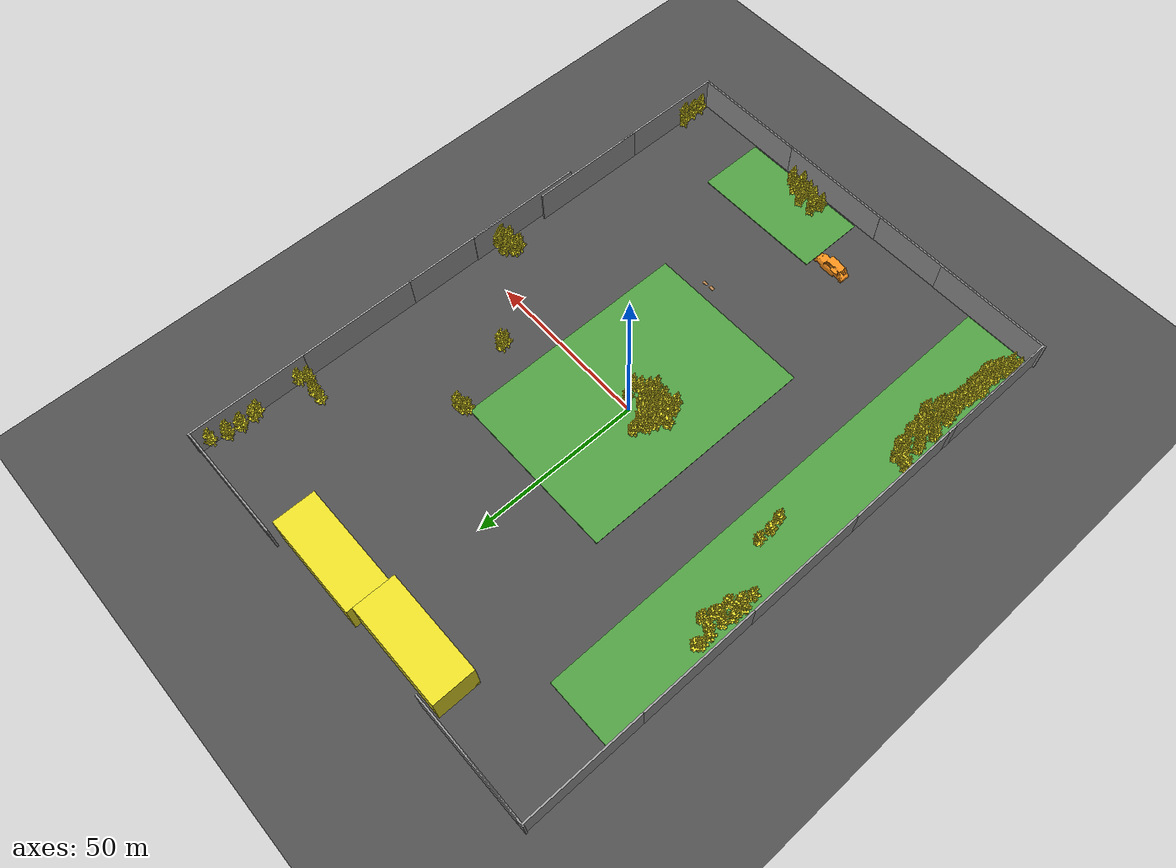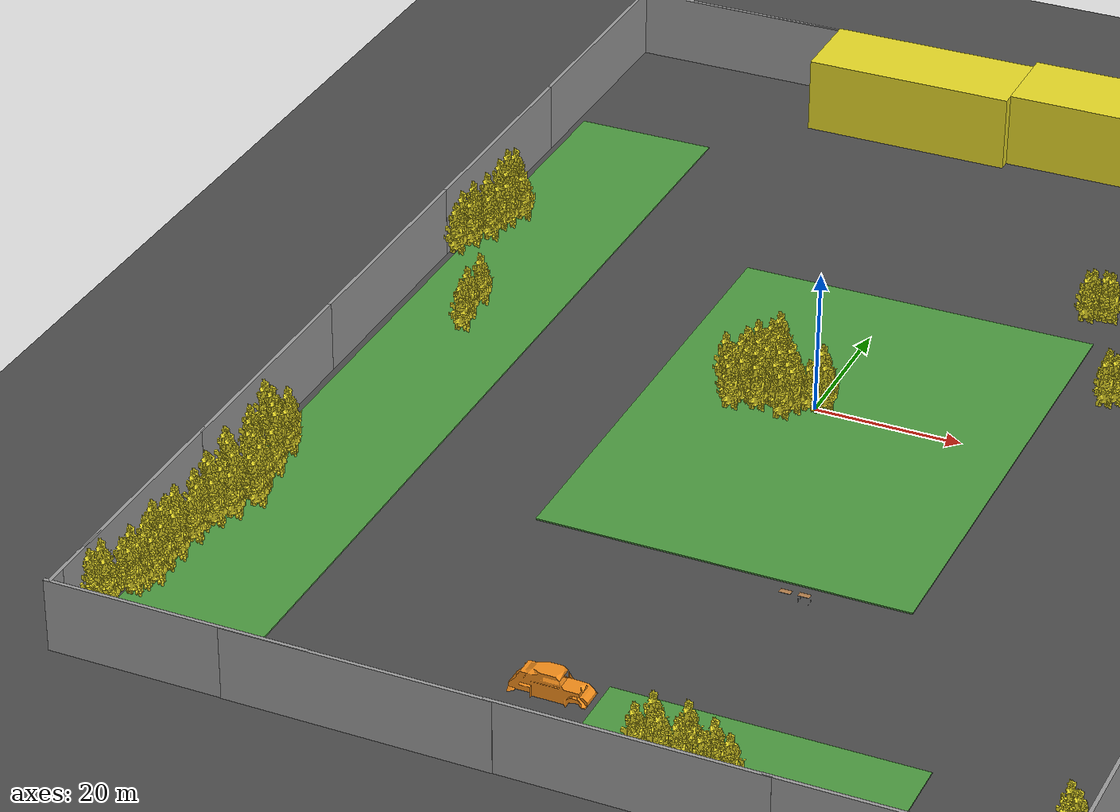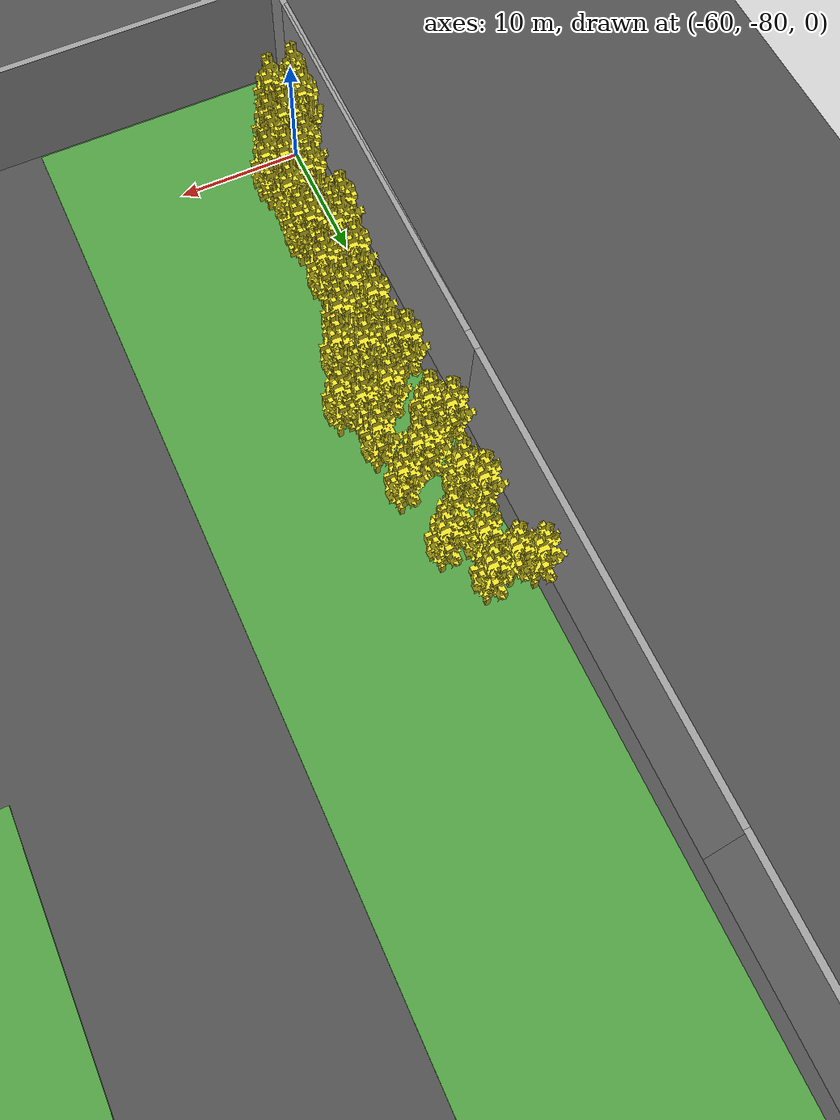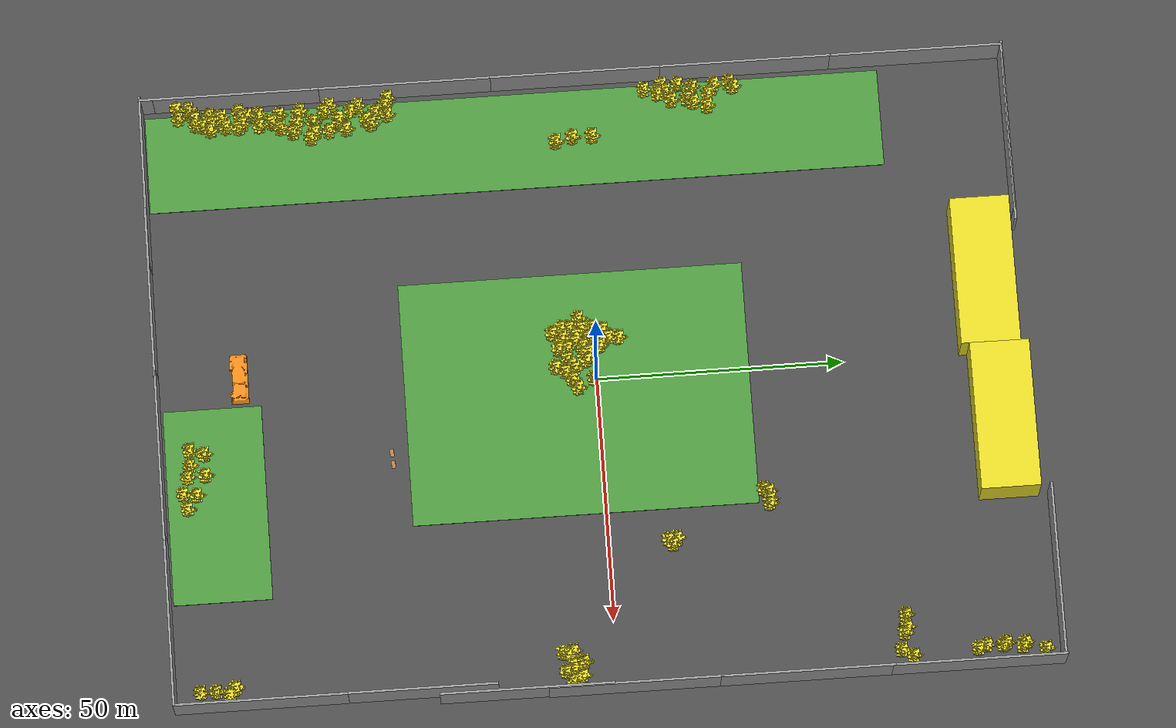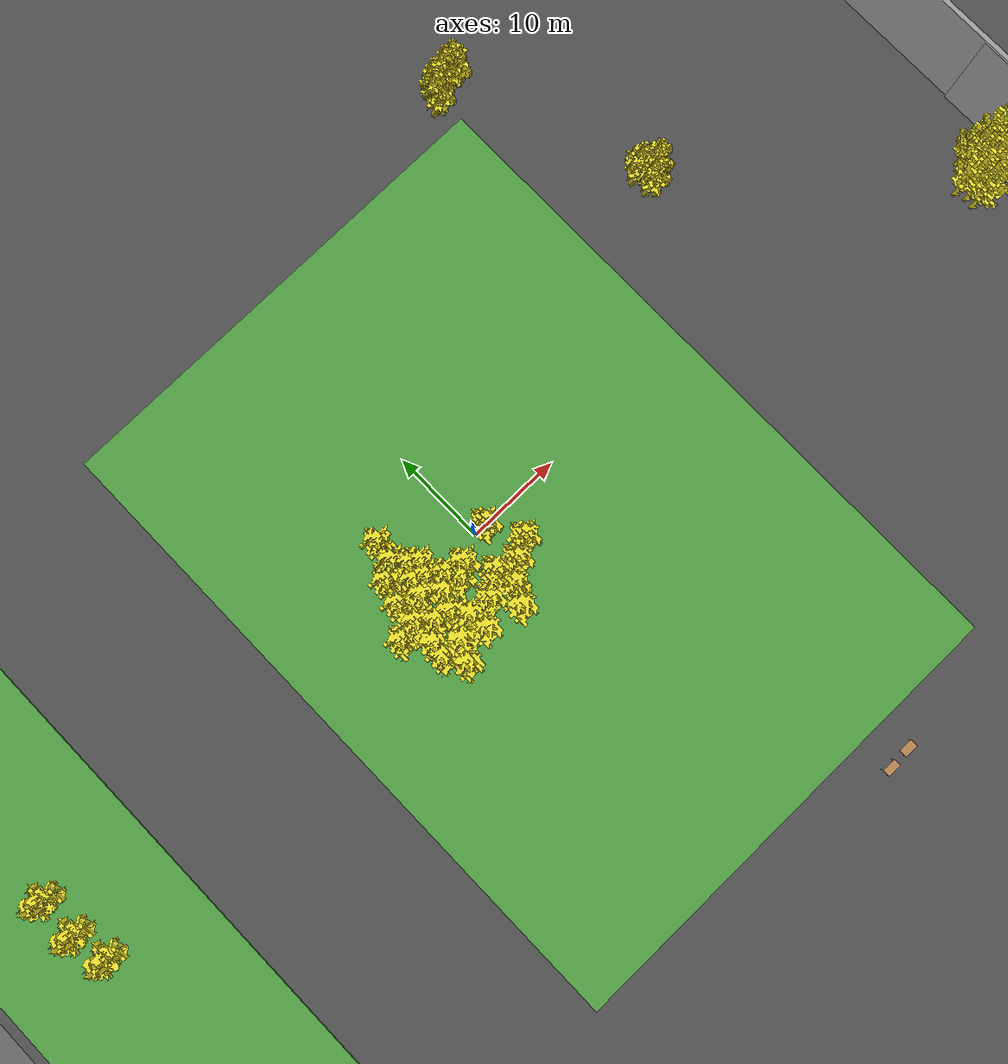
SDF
<sdf version="1.6">
 <world name="default">
  <light name="sun" type="directional">
   <pose>0 0 10 0 -0 0</pose>
   <diffuse>0.8 0.8 0.8 1</diffuse>
   <specular>0.2 0.2 0.2 1</specular>
   <attenuation>
    <range>1000</range>
    <constant>0.9</constant>
    <linear>0.01</linear>
    <quadratic>0.001</quadratic>
   </attenuation>
   <direction>-0.5 0.1 -0.9</direction>
  </light>
  <model name="ground_plane">
   <static>1</static>
   <link name="link">
    <collision name="collision">
     <geometry><plane><normal>0 0 1</normal><size>40000 40000</size></plane></geometry>
     <surface>
      <contact><collide_bitmask>65535</collide_bitmask></contact>
      <friction><ode><mu>100</mu><mu2>50</mu2></ode></friction>
     </surface>
    </collision>
    <visual name="visual">
     <cast_shadows>0</cast_shadows>
     <geometry><plane><normal>0 0 1</normal><size>130 180</size></plane></geometry>
     <material>
      <script><uri>file://media/materials/scripts/gazebo.material</uri><name>Gazebo/Road</name></script>
     </material>
    </visual>
   </link>
  </model>
  <gravity>0 0 -9.8</gravity>
  <magnetic_field>6e-06 2.3e-05 -4.2e-05</magnetic_field>
  <physics name="default_physics" default="0" type="ode">
   <max_step_size>0.001</max_step_size>
   <real_time_factor>1</real_time_factor>
   <real_time_update_rate>1000</real_time_update_rate>
  </physics>
  <scene><ambient>0.4 0.4 0.4 1</ambient><background>0.7 0.7 0.7 1</background><shadows>1</shadows></scene>
  <audio><device>default</device></audio>
  <spherical_coordinates>
   <surface_model>EARTH_WGS84</surface_model>
   <latitude_deg>0</latitude_deg>
   <longitude_deg>0</longitude_deg>
   <elevation>0</elevation>
   <heading_deg>0</heading_deg>
  </spherical_coordinates>
  <model name="grass_plane">
   <link name="link">
    <inertial>
     <mass>1</mass>
     <inertia><ixx>1</ixx><ixy>0</ixy><ixz>0</ixz><iyy>1</iyy><iyz>0</iyz><izz>1</izz></inertia>
    </inertial>
    <visual name="visual">
     <cast_shadows>0</cast_shadows>
     <geometry><box><size>50 70 0.2</size></box></geometry>
     <material>
      <script><uri>file://media/materials/scripts/gazebo.material</uri><name>Gazebo/Grass</name></script>
     </material>
    </visual>
    <collision name="collision">
     <geometry><box><size>10 30 0.2</size></box></geometry>
     <surface>
      <friction>
       <ode><mu>1</mu><mu2>1</mu2><fdir1>0 0 0</fdir1><slip1>0</slip1><slip2>0</slip2></ode>
       <torsional>
        <coefficient>1</coefficient>
        <patch_radius>0</patch_radius>
        <surface_radius>0</surface_radius>
        <use_patch_radius>1</use_patch_radius>
        <ode><slip>0</slip></ode>
       </torsional>
      </friction>
      <bounce><restitution_coefficient>0</restitution_coefficient><threshold>1e+06</threshold></bounce>
      <contact>
       <collide_without_contact>0</collide_without_contact>
       <collide_without_contact_bitmask>1</collide_without_contact_bitmask>
       <collide_bitmask>1</collide_bitmask>
       <ode>
        <soft_cfm>0</soft_cfm>
        <soft_erp>0.2</soft_erp>
        <kp>1e+13</kp>
        <kd>1</kd>
        <max_vel>0.01</max_vel>
        <min_depth>0</min_depth>
       </ode>
       <bullet>
        <split_impulse>1</split_impulse>
        <split_impulse_penetration_threshold>-0.01</split_impulse_penetration_threshold>
        <soft_cfm>0</soft_cfm>
        <soft_erp>0.2</soft_erp>
        <kp>1e+13</kp>
        <kd>1</kd>
       </bullet>
      </contact>
     </surface>
    </collision>
   </link>
   <static>1</static>
   <pose>2.79773 -3.97523 0 0 -0 0</pose>
  </model>
  <atmosphere type="adiabatic"/>
  <model name="tree0">
   <link name="tree_base">
    <inertial>
     <mass>50</mass>
     <inertia>
      <ixx>6.71748</ixx>
      <ixy>2.148e-05</ixy>
      <ixz>-2.4e-07</ixz>
      <iyy>6.71748</iyy>
      <iyz>-0.171807</iyz>
      <izz>6.71748</izz>
     </inertia>
    </inertial>
    <collision name="tree_base_fixed_joint_lump__collision_collision">
     <geometry><mesh><scale>0.4 0.4 0.6</scale><uri>model://tree/meshes/tree_25k_mesh.dae</uri></mesh></geometry>
    </collision>
    <visual name="tree_base_visual">
     <geometry><mesh><scale>0.4 0.4 0.6</scale><uri>model://tree/meshes/tree_25k_mesh.dae</uri></mesh></geometry>
     <material>
      <script><name>Gazebo/Yellow</name><uri>file://media/materials/scripts/gazebo.material</uri></script>
     </material>
    </visual>
   </link>
   <joint name="joint_tree_base" type="fixed"><child>tree_base</child><parent>world</parent></joint>
   <static>1</static>
   <pose>-11.5 1 0 0 -0 0</pose>
  </model>
  <model name="table">
   <static>1</static>
   <link name="link">
    <collision name="surface">
     <pose>0 0 1 0 -0 0</pose>
     <geometry><box><size>1.5 0.8 0.03</size></box></geometry>
     <surface><friction><ode><mu>0.6</mu><mu2>0.6</mu2></ode></friction></surface>
    </collision>
    <visual name="visual1">
     <pose>0 0 1 0 -0 0</pose>
     <geometry><box><size>1.5 0.8 0.03</size></box></geometry>
     <material>
      <script><uri>file://media/materials/scripts/gazebo.material</uri><name>Gazebo/Wood</name></script>
     </material>
    </visual>
    <collision name="front_left_leg">
     <pose>0.68 0.38 0.5 0 -0 0</pose>
     <geometry><cylinder><radius>0.02</radius><length>1</length></cylinder></geometry>
    </collision>
    <visual name="front_left_leg">
     <pose>0.68 0.38 0.5 0 -0 0</pose>
     <geometry><cylinder><radius>0.02</radius><length>1</length></cylinder></geometry>
     <material>
      <script><uri>file://media/materials/scripts/gazebo.material</uri><name>Gazebo/Grey</name></script>
     </material>
    </visual>
    <collision name="front_right_leg">
     <pose>0.68 -0.38 0.5 0 -0 0</pose>
     <geometry><cylinder><radius>0.02</radius><length>1</length></cylinder></geometry>
    </collision>
    <visual name="front_right_leg">
     <pose>0.68 -0.38 0.5 0 -0 0</pose>
     <geometry><cylinder><radius>0.02</radius><length>1</length></cylinder></geometry>
     <material>
      <script><uri>file://media/materials/scripts/gazebo.material</uri><name>Gazebo/Grey</name></script>
     </material>
    </visual>
    <collision name="back_right_leg">
     <pose>-0.68 -0.38 0.5 0 -0 0</pose>
     <geometry><cylinder><radius>0.02</radius><length>1</length></cylinder></geometry>
    </collision>
    <visual name="back_right_leg">
     <pose>-0.68 -0.38 0.5 0 -0 0</pose>
     <geometry><cylinder><radius>0.02</radius><length>1</length></cylinder></geometry>
     <material>
      <script><uri>file://media/materials/scripts/gazebo.material</uri><name>Gazebo/Grey</name></script>
     </material>
    </visual>
    <collision name="back_left_leg">
     <pose>-0.68 0.38 0.5 0 -0 0</pose>
     <geometry><cylinder><radius>0.02</radius><length>1</length></cylinder></geometry>
    </collision>
    <visual name="back_left_leg">
     <pose>-0.68 0.38 0.5 0 -0 0</pose>
     <geometry><cylinder><radius>0.02</radius><length>1</length></cylinder></geometry>
     <material>
      <script><uri>file://media/materials/scripts/gazebo.material</uri><name>Gazebo/Grey</name></script>
     </material>
    </visual>
   </link>
   <pose>15.0111 -42.1076 0 0 -0 0</pose>
  </model>
  <model name="table_0">
   <static>1</static>
   <link name="link">
    <collision name="surface">
     <pose>0 0 1 0 -0 0</pose>
     <geometry><box><size>1.5 0.8 0.03</size></box></geometry>
     <surface><friction><ode><mu>0.6</mu><mu2>0.6</mu2></ode></friction></surface>
    </collision>
    <visual name="visual1">
     <pose>0 0 1 0 -0 0</pose>
     <geometry><box><size>1.5 0.8 0.03</size></box></geometry>
     <material>
      <script><uri>file://media/materials/scripts/gazebo.material</uri><name>Gazebo/Wood</name></script>
     </material>
    </visual>
    <collision name="front_left_leg">
     <pose>0.68 0.38 0.5 0 -0 0</pose>
     <geometry><cylinder><radius>0.02</radius><length>1</length></cylinder></geometry>
    </collision>
    <visual name="front_left_leg">
     <pose>0.68 0.38 0.5 0 -0 0</pose>
     <geometry><cylinder><radius>0.02</radius><length>1</length></cylinder></geometry>
     <material>
      <script><uri>file://media/materials/scripts/gazebo.material</uri><name>Gazebo/Grey</name></script>
     </material>
    </visual>
    <collision name="front_right_leg">
     <pose>0.68 -0.38 0.5 0 -0 0</pose>
     <geometry><cylinder><radius>0.02</radius><length>1</length></cylinder></geometry>
    </collision>
    <visual name="front_right_leg">
     <pose>0.68 -0.38 0.5 0 -0 0</pose>
     <geometry><cylinder><radius>0.02</radius><length>1</length></cylinder></geometry>
     <material>
      <script><uri>file://media/materials/scripts/gazebo.material</uri><name>Gazebo/Grey</name></script>
     </material>
    </visual>
    <collision name="back_right_leg">
     <pose>-0.68 -0.38 0.5 0 -0 0</pose>
     <geometry><cylinder><radius>0.02</radius><length>1</length></cylinder></geometry>
    </collision>
    <visual name="back_right_leg">
     <pose>-0.68 -0.38 0.5 0 -0 0</pose>
     <geometry><cylinder><radius>0.02</radius><length>1</length></cylinder></geometry>
     <material>
      <script><uri>file://media/materials/scripts/gazebo.material</uri><name>Gazebo/Grey</name></script>
     </material>
    </visual>
    <collision name="back_left_leg">
     <pose>-0.68 0.38 0.5 0 -0 0</pose>
     <geometry><cylinder><radius>0.02</radius><length>1</length></cylinder></geometry>
    </collision>
    <visual name="back_left_leg">
     <pose>-0.68 0.38 0.5 0 -0 0</pose>
     <geometry><cylinder><radius>0.02</radius><length>1</length></cylinder></geometry>
     <material>
      <script><uri>file://media/materials/scripts/gazebo.material</uri><name>Gazebo/Grey</name></script>
     </material>
    </visual>
   </link>
   <pose>12.6248 -42.2786 0 0 -0 0</pose>
  </model>
  <model name="wall1_clone_clone">
   <link name="link">
    <enable_wind>1</enable_wind>
    <inertial>
     <mass>1</mass>
     <inertia><ixx>1</ixx><ixy>0</ixy><ixz>0</ixz><iyy>1</iyy><iyz>0</iyz><izz>1</izz></inertia>
    </inertial>
    <visual name="visual">
     <cast_shadows>0</cast_shadows>
     <geometry><box><size>35 0.5 10</size></box></geometry>
     <material>
      <script>
       <uri>model://grey_wall/materials/scripts</uri>
       <uri>model://grey_wall/materials/textures</uri>
       <name>vrc/grey_wall</name>
      </script>
      <shader type="pixel"><normal_map>__default__</normal_map></shader>
      <ambient>1 1 1 1</ambient>
      <diffuse>1 1 1 1</diffuse>
      <specular>0 0 0 1</specular>
      <emissive>0 0 0 1</emissive>
     </material>
    </visual>
    <collision name="collision">
     <geometry><box><size>35 0.5 10</size></box></geometry>
     <surface>
      <friction>
       <ode><mu>1</mu><mu2>1</mu2><fdir1>0 0 0</fdir1><slip1>0</slip1><slip2>0</slip2></ode>
       <torsional>
        <coefficient>1</coefficient>
        <patch_radius>0</patch_radius>
        <surface_radius>0</surface_radius>
        <use_patch_radius>1</use_patch_radius>
        <ode><slip>0</slip></ode>
       </torsional>
      </friction>
      <bounce><restitution_coefficient>0</restitution_coefficient><threshold>1e+06</threshold></bounce>
      <contact>
       <collide_without_contact>0</collide_without_contact>
       <collide_without_contact_bitmask>1</collide_without_contact_bitmask>
       <collide_bitmask>1</collide_bitmask>
       <ode>
        <soft_cfm>0</soft_cfm>
        <soft_erp>0.2</soft_erp>
        <kp>1e+13</kp>
        <kd>1</kd>
        <max_vel>0.01</max_vel>
        <min_depth>0</min_depth>
       </ode>
       <bullet>
        <split_impulse>1</split_impulse>
        <split_impulse_penetration_threshold>-0.01</split_impulse_penetration_threshold>
        <soft_cfm>0</soft_cfm>
        <soft_erp>0.2</soft_erp>
        <kp>1e+13</kp>
        <kd>1</kd>
       </bullet>
      </contact>
     </surface>
    </collision>
   </link>
   <static>1</static>
   <pose>-45.0044 86.7474 5 0 -0 0</pose>
  </model>
  <model name="wall1_clone_clone_0">
   <link name="link">
    <enable_wind>1</enable_wind>
    <inertial>
     <mass>1</mass>
     <inertia><ixx>1</ixx><ixy>0</ixy><ixz>0</ixz><iyy>1</iyy><iyz>0</iyz><izz>1</izz></inertia>
    </inertial>
    <visual name="visual">
     <cast_shadows>0</cast_shadows>
     <geometry><box><size>35 0.5 10</size></box></geometry>
     <material>
      <script>
       <uri>model://grey_wall/materials/scripts</uri>
       <uri>model://grey_wall/materials/textures</uri>
       <name>vrc/grey_wall</name>
      </script>
      <shader type="pixel"><normal_map>__default__</normal_map></shader>
      <ambient>1 1 1 1</ambient>
      <diffuse>1 1 1 1</diffuse>
      <specular>0 0 0 1</specular>
      <emissive>0 0 0 1</emissive>
     </material>
    </visual>
    <collision name="collision">
     <geometry><box><size>35 0.5 10</size></box></geometry>
     <surface>
      <friction>
       <ode><mu>1</mu><mu2>1</mu2><fdir1>0 0 0</fdir1><slip1>0</slip1><slip2>0</slip2></ode>
       <torsional>
        <coefficient>1</coefficient>
        <patch_radius>0</patch_radius>
        <surface_radius>0</surface_radius>
        <use_patch_radius>1</use_patch_radius>
        <ode><slip>0</slip></ode>
       </torsional>
      </friction>
      <bounce><restitution_coefficient>0</restitution_coefficient><threshold>1e+06</threshold></bounce>
      <contact>
       <collide_without_contact>0</collide_without_contact>
       <collide_without_contact_bitmask>1</collide_without_contact_bitmask>
       <collide_bitmask>1</collide_bitmask>
       <ode>
        <soft_cfm>0</soft_cfm>
        <soft_erp>0.2</soft_erp>
        <kp>1e+13</kp>
        <kd>1</kd>
        <max_vel>0.01</max_vel>
        <min_depth>0</min_depth>
       </ode>
       <bullet>
        <split_impulse>1</split_impulse>
        <split_impulse_penetration_threshold>-0.01</split_impulse_penetration_threshold>
        <soft_cfm>0</soft_cfm>
        <soft_erp>0.2</soft_erp>
        <kp>1e+13</kp>
        <kd>1</kd>
       </bullet>
      </contact>
     </surface>
    </collision>
   </link>
   <static>1</static>
   <pose>-61.9101 69.2935 5 0 0 -1.57191</pose>
  </model>
  <model name="wall1_clone_clone_0_clone">
   <link name="link">
    <enable_wind>1</enable_wind>
    <inertial>
     <mass>1</mass>
     <inertia><ixx>1</ixx><ixy>0</ixy><ixz>0</ixz><iyy>1</iyy><iyz>0</iyz><izz>1</izz></inertia>
    </inertial>
    <visual name="visual">
     <cast_shadows>0</cast_shadows>
     <geometry><box><size>35 0.5 10</size></box></geometry>
     <material>
      <script>
       <uri>model://grey_wall/materials/scripts</uri>
       <uri>model://grey_wall/materials/textures</uri>
       <name>vrc/grey_wall</name>
      </script>
      <shader type="pixel"><normal_map>__default__</normal_map></shader>
      <ambient>1 1 1 1</ambient>
      <diffuse>1 1 1 1</diffuse>
      <specular>0 0 0 1</specular>
      <emissive>0 0 0 1</emissive>
     </material>
    </visual>
    <collision name="collision">
     <geometry><box><size>35 0.5 10</size></box></geometry>
     <surface>
      <friction>
       <ode><mu>1</mu><mu2>1</mu2><fdir1>0 0 0</fdir1><slip1>0</slip1><slip2>0</slip2></ode>
       <torsional>
        <coefficient>1</coefficient>
        <patch_radius>0</patch_radius>
        <surface_radius>0</surface_radius>
        <use_patch_radius>1</use_patch_radius>
        <ode><slip>0</slip></ode>
       </torsional>
      </friction>
      <bounce><restitution_coefficient>0</restitution_coefficient><threshold>1e+06</threshold></bounce>
      <contact>
       <collide_without_contact>0</collide_without_contact>
       <collide_without_contact_bitmask>1</collide_without_contact_bitmask>
       <collide_bitmask>1</collide_bitmask>
       <ode>
        <soft_cfm>0</soft_cfm>
        <soft_erp>0.2</soft_erp>
        <kp>1e+13</kp>
        <kd>1</kd>
        <max_vel>0.01</max_vel>
        <min_depth>0</min_depth>
       </ode>
       <bullet>
        <split_impulse>1</split_impulse>
        <split_impulse_penetration_threshold>-0.01</split_impulse_penetration_threshold>
        <soft_cfm>0</soft_cfm>
        <soft_erp>0.2</soft_erp>
        <kp>1e+13</kp>
        <kd>1</kd>
       </bullet>
      </contact>
     </surface>
    </collision>
   </link>
   <static>1</static>
   <pose>-61.9495 34.6526 5 0 0 -1.57191</pose>
  </model>
  <model name="wall1_clone_clone_0_clone_0">
   <link name="link">
    <enable_wind>1</enable_wind>
    <inertial>
     <mass>1</mass>
     <inertia><ixx>1</ixx><ixy>0</ixy><ixz>0</ixz><iyy>1</iyy><iyz>0</iyz><izz>1</izz></inertia>
    </inertial>
    <visual name="visual">
     <cast_shadows>0</cast_shadows>
     <geometry><box><size>35 0.5 10</size></box></geometry>
     <material>
      <script>
       <uri>model://grey_wall/materials/scripts</uri>
       <uri>model://grey_wall/materials/textures</uri>
       <name>vrc/grey_wall</name>
      </script>
      <shader type="pixel"><normal_map>__default__</normal_map></shader>
      <ambient>1 1 1 1</ambient>
      <diffuse>1 1 1 1</diffuse>
      <specular>0 0 0 1</specular>
      <emissive>0 0 0 1</emissive>
     </material>
    </visual>
    <collision name="collision">
     <geometry><box><size>35 0.5 10</size></box></geometry>
     <surface>
      <friction>
       <ode><mu>1</mu><mu2>1</mu2><fdir1>0 0 0</fdir1><slip1>0</slip1><slip2>0</slip2></ode>
       <torsional>
        <coefficient>1</coefficient>
        <patch_radius>0</patch_radius>
        <surface_radius>0</surface_radius>
        <use_patch_radius>1</use_patch_radius>
        <ode><slip>0</slip></ode>
       </torsional>
      </friction>
      <bounce><restitution_coefficient>0</restitution_coefficient><threshold>1e+06</threshold></bounce>
      <contact>
       <collide_without_contact>0</collide_without_contact>
       <collide_without_contact_bitmask>1</collide_without_contact_bitmask>
       <collide_bitmask>1</collide_bitmask>
       <ode>
        <soft_cfm>0</soft_cfm>
        <soft_erp>0.2</soft_erp>
        <kp>1e+13</kp>
        <kd>1</kd>
        <max_vel>0.01</max_vel>
        <min_depth>0</min_depth>
       </ode>
       <bullet>
        <split_impulse>1</split_impulse>
        <split_impulse_penetration_threshold>-0.01</split_impulse_penetration_threshold>
        <soft_cfm>0</soft_cfm>
        <soft_erp>0.2</soft_erp>
        <kp>1e+13</kp>
        <kd>1</kd>
       </bullet>
      </contact>
     </surface>
    </collision>
   </link>
   <static>1</static>
   <pose>-61.997 -0.05092 5 0 0 -1.57191</pose>
  </model>
  <model name="wall1_clone_clone_0_clone_1">
   <link name="link">
    <enable_wind>1</enable_wind>
    <inertial>
     <mass>1</mass>
     <inertia><ixx>1</ixx><ixy>0</ixy><ixz>0</ixz><iyy>1</iyy><iyz>0</iyz><izz>1</izz></inertia>
    </inertial>
    <visual name="visual">
     <cast_shadows>0</cast_shadows>
     <geometry><box><size>35 0.5 10</size></box></geometry>
     <material>
      <script>
       <uri>model://grey_wall/materials/scripts</uri>
       <uri>model://grey_wall/materials/textures</uri>
       <name>vrc/grey_wall</name>
      </script>
      <shader type="pixel"><normal_map>__default__</normal_map></shader>
      <ambient>1 1 1 1</ambient>
      <diffuse>1 1 1 1</diffuse>
      <specular>0 0 0 1</specular>
      <emissive>0 0 0 1</emissive>
     </material>
    </visual>
    <collision name="collision">
     <geometry><box><size>35 0.5 10</size></box></geometry>
     <surface>
      <friction>
       <ode><mu>1</mu><mu2>1</mu2><fdir1>0 0 0</fdir1><slip1>0</slip1><slip2>0</slip2></ode>
       <torsional>
        <coefficient>1</coefficient>
        <patch_radius>0</patch_radius>
        <surface_radius>0</surface_radius>
        <use_patch_radius>1</use_patch_radius>
        <ode><slip>0</slip></ode>
       </torsional>
      </friction>
      <bounce><restitution_coefficient>0</restitution_coefficient><threshold>1e+06</threshold></bounce>
      <contact>
       <collide_without_contact>0</collide_without_contact>
       <collide_without_contact_bitmask>1</collide_without_contact_bitmask>
       <collide_bitmask>1</collide_bitmask>
       <ode>
        <soft_cfm>0</soft_cfm>
        <soft_erp>0.2</soft_erp>
        <kp>1e+13</kp>
        <kd>1</kd>
        <max_vel>0.01</max_vel>
        <min_depth>0</min_depth>
       </ode>
       <bullet>
        <split_impulse>1</split_impulse>
        <split_impulse_penetration_threshold>-0.01</split_impulse_penetration_threshold>
        <soft_cfm>0</soft_cfm>
        <soft_erp>0.2</soft_erp>
        <kp>1e+13</kp>
        <kd>1</kd>
       </bullet>
      </contact>
     </surface>
    </collision>
   </link>
   <static>1</static>
   <pose>-62.0288 -34.8437 5 0 0 -1.57191</pose>
  </model>
  <model name="wall1_clone_clone_0_clone_2">
   <link name="link">
    <enable_wind>1</enable_wind>
    <inertial>
     <mass>1</mass>
     <inertia><ixx>1</ixx><ixy>0</ixy><ixz>0</ixz><iyy>1</iyy><iyz>0</iyz><izz>1</izz></inertia>
    </inertial>
    <visual name="visual">
     <cast_shadows>0</cast_shadows>
     <geometry><box><size>35 0.5 10</size></box></geometry>
     <material>
      <script>
       <uri>model://grey_wall/materials/scripts</uri>
       <uri>model://grey_wall/materials/textures</uri>
       <name>vrc/grey_wall</name>
      </script>
      <shader type="pixel"><normal_map>__default__</normal_map></shader>
      <ambient>1 1 1 1</ambient>
      <diffuse>1 1 1 1</diffuse>
      <specular>0 0 0 1</specular>
      <emissive>0 0 0 1</emissive>
     </material>
    </visual>
    <collision name="collision">
     <geometry><box><size>35 0.5 10</size></box></geometry>
     <surface>
      <friction>
       <ode><mu>1</mu><mu2>1</mu2><fdir1>0 0 0</fdir1><slip1>0</slip1><slip2>0</slip2></ode>
       <torsional>
        <coefficient>1</coefficient>
        <patch_radius>0</patch_radius>
        <surface_radius>0</surface_radius>
        <use_patch_radius>1</use_patch_radius>
        <ode><slip>0</slip></ode>
       </torsional>
      </friction>
      <bounce><restitution_coefficient>0</restitution_coefficient><threshold>1e+06</threshold></bounce>
      <contact>
       <collide_without_contact>0</collide_without_contact>
       <collide_without_contact_bitmask>1</collide_without_contact_bitmask>
       <collide_bitmask>1</collide_bitmask>
       <ode>
        <soft_cfm>0</soft_cfm>
        <soft_erp>0.2</soft_erp>
        <kp>1e+13</kp>
        <kd>1</kd>
        <max_vel>0.01</max_vel>
        <min_depth>0</min_depth>
       </ode>
       <bullet>
        <split_impulse>1</split_impulse>
        <split_impulse_penetration_threshold>-0.01</split_impulse_penetration_threshold>
        <soft_cfm>0</soft_cfm>
        <soft_erp>0.2</soft_erp>
        <kp>1e+13</kp>
        <kd>1</kd>
       </bullet>
      </contact>
     </surface>
    </collision>
   </link>
   <static>1</static>
   <pose>-62.0731 -68.5912 5 0 0 -1.57191</pose>
  </model>
  <model name="wall1_clone_clone_0_clone_3">
   <link name="link">
    <enable_wind>1</enable_wind>
    <inertial>
     <mass>1</mass>
     <inertia><ixx>1</ixx><ixy>0</ixy><ixz>0</ixz><iyy>1</iyy><iyz>0</iyz><izz>1</izz></inertia>
    </inertial>
    <visual name="visual">
     <cast_shadows>0</cast_shadows>
     <geometry><box><size>35 0.5 10</size></box></geometry>
     <material>
      <script>
       <uri>model://grey_wall/materials/scripts</uri>
       <uri>model://grey_wall/materials/textures</uri>
       <name>vrc/grey_wall</name>
      </script>
      <shader type="pixel"><normal_map>__default__</normal_map></shader>
      <ambient>1 1 1 1</ambient>
      <diffuse>1 1 1 1</diffuse>
      <specular>0 0 0 1</specular>
      <emissive>0 0 0 1</emissive>
     </material>
    </visual>
    <collision name="collision">
     <geometry><box><size>35 0.5 10</size></box></geometry>
     <surface>
      <friction>
       <ode><mu>1</mu><mu2>1</mu2><fdir1>0 0 0</fdir1><slip1>0</slip1><slip2>0</slip2></ode>
       <torsional>
        <coefficient>1</coefficient>
        <patch_radius>0</patch_radius>
        <surface_radius>0</surface_radius>
        <use_patch_radius>1</use_patch_radius>
        <ode><slip>0</slip></ode>
       </torsional>
      </friction>
      <bounce><restitution_coefficient>0</restitution_coefficient><threshold>1e+06</threshold></bounce>
      <contact>
       <collide_without_contact>0</collide_without_contact>
       <collide_without_contact_bitmask>1</collide_without_contact_bitmask>
       <collide_bitmask>1</collide_bitmask>
       <ode>
        <soft_cfm>0</soft_cfm>
        <soft_erp>0.2</soft_erp>
        <kp>1e+13</kp>
        <kd>1</kd>
        <max_vel>0.01</max_vel>
        <min_depth>0</min_depth>
       </ode>
       <bullet>
        <split_impulse>1</split_impulse>
        <split_impulse_penetration_threshold>-0.01</split_impulse_penetration_threshold>
        <soft_cfm>0</soft_cfm>
        <soft_erp>0.2</soft_erp>
        <kp>1e+13</kp>
        <kd>1</kd>
       </bullet>
      </contact>
     </surface>
    </collision>
   </link>
   <static>1</static>
   <pose>62.8276 -41.3887 5 0 0 -1.57191</pose>
  </model>
  <model name="wall1_clone_clone_0_clone_4">
   <link name="link">
    <enable_wind>1</enable_wind>
    <inertial>
     <mass>1</mass>
     <inertia><ixx>1</ixx><ixy>0</ixy><ixz>0</ixz><iyy>1</iyy><iyz>0</iyz><izz>1</izz></inertia>
    </inertial>
    <visual name="visual">
     <cast_shadows>0</cast_shadows>
     <geometry><box><size>35 0.5 10</size></box></geometry>
     <material>
      <script>
       <uri>model://grey_wall/materials/scripts</uri>
       <uri>model://grey_wall/materials/textures</uri>
       <name>vrc/grey_wall</name>
      </script>
      <shader type="pixel"><normal_map>__default__</normal_map></shader>
      <ambient>1 1 1 1</ambient>
      <diffuse>1 1 1 1</diffuse>
      <specular>0 0 0 1</specular>
      <emissive>0 0 0 1</emissive>
     </material>
    </visual>
    <collision name="collision">
     <geometry><box><size>35 0.5 10</size></box></geometry>
     <surface>
      <friction>
       <ode><mu>1</mu><mu2>1</mu2><fdir1>0 0 0</fdir1><slip1>0</slip1><slip2>0</slip2></ode>
       <torsional>
        <coefficient>1</coefficient>
        <patch_radius>0</patch_radius>
        <surface_radius>0</surface_radius>
        <use_patch_radius>1</use_patch_radius>
        <ode><slip>0</slip></ode>
       </torsional>
      </friction>
      <bounce><restitution_coefficient>0</restitution_coefficient><threshold>1e+06</threshold></bounce>
      <contact>
       <collide_without_contact>0</collide_without_contact>
       <collide_without_contact_bitmask>1</collide_without_contact_bitmask>
       <collide_bitmask>1</collide_bitmask>
       <ode>
        <soft_cfm>0</soft_cfm>
        <soft_erp>0.2</soft_erp>
        <kp>1e+13</kp>
        <kd>1</kd>
        <max_vel>0.01</max_vel>
        <min_depth>0</min_depth>
       </ode>
       <bullet>
        <split_impulse>1</split_impulse>
        <split_impulse_penetration_threshold>-0.01</split_impulse_penetration_threshold>
        <soft_cfm>0</soft_cfm>
        <soft_erp>0.2</soft_erp>
        <kp>1e+13</kp>
        <kd>1</kd>
       </bullet>
      </contact>
     </surface>
    </collision>
   </link>
   <static>1</static>
   <pose>62.8357 -71.4632 5 0 0 -1.57191</pose>
  </model>
  <model name="wall1_clone_clone_clone">
   <link name="link">
    <enable_wind>1</enable_wind>
    <inertial>
     <mass>1</mass>
     <inertia><ixx>1</ixx><ixy>0</ixy><ixz>0</ixz><iyy>1</iyy><iyz>0</iyz><izz>1</izz></inertia>
    </inertial>
    <visual name="visual">
     <cast_shadows>0</cast_shadows>
     <geometry><box><size>35 0.5 10</size></box></geometry>
     <material>
      <script>
       <uri>model://grey_wall/materials/scripts</uri>
       <uri>model://grey_wall/materials/textures</uri>
       <name>vrc/grey_wall</name>
      </script>
      <shader type="pixel"><normal_map>__default__</normal_map></shader>
      <ambient>1 1 1 1</ambient>
      <diffuse>1 1 1 1</diffuse>
      <specular>0 0 0 1</specular>
      <emissive>0 0 0 1</emissive>
     </material>
    </visual>
    <collision name="collision">
     <geometry><box><size>35 0.5 10</size></box></geometry>
     <surface>
      <friction>
       <ode><mu>1</mu><mu2>1</mu2><fdir1>0 0 0</fdir1><slip1>0</slip1><slip2>0</slip2></ode>
       <torsional>
        <coefficient>1</coefficient>
        <patch_radius>0</patch_radius>
        <surface_radius>0</surface_radius>
        <use_patch_radius>1</use_patch_radius>
        <ode><slip>0</slip></ode>
       </torsional>
      </friction>
      <bounce><restitution_coefficient>0</restitution_coefficient><threshold>1e+06</threshold></bounce>
      <contact>
       <collide_without_contact>0</collide_without_contact>
       <collide_without_contact_bitmask>1</collide_without_contact_bitmask>
       <collide_bitmask>1</collide_bitmask>
       <ode>
        <soft_cfm>0</soft_cfm>
        <soft_erp>0.2</soft_erp>
        <kp>1e+13</kp>
        <kd>1</kd>
        <max_vel>0.01</max_vel>
        <min_depth>0</min_depth>
       </ode>
       <bullet>
        <split_impulse>1</split_impulse>
        <split_impulse_penetration_threshold>-0.01</split_impulse_penetration_threshold>
        <soft_cfm>0</soft_cfm>
        <soft_erp>0.2</soft_erp>
        <kp>1e+13</kp>
        <kd>1</kd>
       </bullet>
      </contact>
     </surface>
    </collision>
   </link>
   <static>1</static>
   <pose>45.5042 -88.7374 5 0 -0 0</pose>
  </model>
  <model name="wall1_clone_clone_clone_0">
   <link name="link">
    <enable_wind>1</enable_wind>
    <inertial>
     <mass>1</mass>
     <inertia><ixx>1</ixx><ixy>0</ixy><ixz>0</ixz><iyy>1</iyy><iyz>0</iyz><izz>1</izz></inertia>
    </inertial>
    <visual name="visual">
     <cast_shadows>0</cast_shadows>
     <geometry><box><size>35 0.5 10</size></box></geometry>
     <material>
      <script>
       <uri>model://grey_wall/materials/scripts</uri>
       <uri>model://grey_wall/materials/textures</uri>
       <name>vrc/grey_wall</name>
      </script>
      <shader type="pixel"><normal_map>__default__</normal_map></shader>
      <ambient>1 1 1 1</ambient>
      <diffuse>1 1 1 1</diffuse>
      <specular>0 0 0 1</specular>
      <emissive>0 0 0 1</emissive>
     </material>
    </visual>
    <collision name="collision">
     <geometry><box><size>35 0.5 10</size></box></geometry>
     <surface>
      <friction>
       <ode><mu>1</mu><mu2>1</mu2><fdir1>0 0 0</fdir1><slip1>0</slip1><slip2>0</slip2></ode>
       <torsional>
        <coefficient>1</coefficient>
        <patch_radius>0</patch_radius>
        <surface_radius>0</surface_radius>
        <use_patch_radius>1</use_patch_radius>
        <ode><slip>0</slip></ode>
       </torsional>
      </friction>
      <bounce><restitution_coefficient>0</restitution_coefficient><threshold>1e+06</threshold></bounce>
      <contact>
       <collide_without_contact>0</collide_without_contact>
       <collide_without_contact_bitmask>1</collide_without_contact_bitmask>
       <collide_bitmask>1</collide_bitmask>
       <ode>
        <soft_cfm>0</soft_cfm>
        <soft_erp>0.2</soft_erp>
        <kp>1e+13</kp>
        <kd>1</kd>
        <max_vel>0.01</max_vel>
        <min_depth>0</min_depth>
       </ode>
       <bullet>
        <split_impulse>1</split_impulse>
        <split_impulse_penetration_threshold>-0.01</split_impulse_penetration_threshold>
        <soft_cfm>0</soft_cfm>
        <soft_erp>0.2</soft_erp>
        <kp>1e+13</kp>
        <kd>1</kd>
       </bullet>
      </contact>
     </surface>
    </collision>
   </link>
   <static>1</static>
   <pose>11.7564 -88.7753 5 0 -0 0</pose>
  </model>
  <model name="wall1_clone_clone_clone_1">
   <link name="link">
    <enable_wind>1</enable_wind>
    <inertial>
     <mass>1</mass>
     <inertia><ixx>1</ixx><ixy>0</ixy><ixz>0</ixz><iyy>1</iyy><iyz>0</iyz><izz>1</izz></inertia>
    </inertial>
    <visual name="visual">
     <cast_shadows>0</cast_shadows>
     <geometry><box><size>35 0.5 10</size></box></geometry>
     <material>
      <script>
       <uri>model://grey_wall/materials/scripts</uri>
       <uri>model://grey_wall/materials/textures</uri>
       <name>vrc/grey_wall</name>
      </script>
      <shader type="pixel"><normal_map>__default__</normal_map></shader>
      <ambient>1 1 1 1</ambient>
      <diffuse>1 1 1 1</diffuse>
      <specular>0 0 0 1</specular>
      <emissive>0 0 0 1</emissive>
     </material>
    </visual>
    <collision name="collision">
     <geometry><box><size>35 0.5 10</size></box></geometry>
     <surface>
      <friction>
       <ode><mu>1</mu><mu2>1</mu2><fdir1>0 0 0</fdir1><slip1>0</slip1><slip2>0</slip2></ode>
       <torsional>
        <coefficient>1</coefficient>
        <patch_radius>0</patch_radius>
        <surface_radius>0</surface_radius>
        <use_patch_radius>1</use_patch_radius>
        <ode><slip>0</slip></ode>
       </torsional>
      </friction>
      <bounce><restitution_coefficient>0</restitution_coefficient><threshold>1e+06</threshold></bounce>
      <contact>
       <collide_without_contact>0</collide_without_contact>
       <collide_without_contact_bitmask>1</collide_without_contact_bitmask>
       <collide_bitmask>1</collide_bitmask>
       <ode>
        <soft_cfm>0</soft_cfm>
        <soft_erp>0.2</soft_erp>
        <kp>1e+13</kp>
        <kd>1</kd>
        <max_vel>0.01</max_vel>
        <min_depth>0</min_depth>
       </ode>
       <bullet>
        <split_impulse>1</split_impulse>
        <split_impulse_penetration_threshold>-0.01</split_impulse_penetration_threshold>
        <soft_cfm>0</soft_cfm>
        <soft_erp>0.2</soft_erp>
        <kp>1e+13</kp>
        <kd>1</kd>
       </bullet>
      </contact>
     </surface>
    </collision>
   </link>
   <static>1</static>
   <pose>-22.0368 -88.8383 5 0 -0 0</pose>
  </model>
  <model name="wall1_clone_clone_clone_2">
   <link name="link">
    <enable_wind>1</enable_wind>
    <inertial>
     <mass>1</mass>
     <inertia><ixx>1</ixx><ixy>0</ixy><ixz>0</ixz><iyy>1</iyy><iyz>0</iyz><izz>1</izz></inertia>
    </inertial>
    <visual name="visual">
     <cast_shadows>0</cast_shadows>
     <geometry><box><size>35 0.5 10</size></box></geometry>
     <material>
      <script>
       <uri>model://grey_wall/materials/scripts</uri>
       <uri>model://grey_wall/materials/textures</uri>
       <name>vrc/grey_wall</name>
      </script>
      <shader type="pixel"><normal_map>__default__</normal_map></shader>
      <ambient>1 1 1 1</ambient>
      <diffuse>1 1 1 1</diffuse>
      <specular>0 0 0 1</specular>
      <emissive>0 0 0 1</emissive>
     </material>
    </visual>
    <collision name="collision">
     <geometry><box><size>35 0.5 10</size></box></geometry>
     <surface>
      <friction>
       <ode><mu>1</mu><mu2>1</mu2><fdir1>0 0 0</fdir1><slip1>0</slip1><slip2>0</slip2></ode>
       <torsional>
        <coefficient>1</coefficient>
        <patch_radius>0</patch_radius>
        <surface_radius>0</surface_radius>
        <use_patch_radius>1</use_patch_radius>
        <ode><slip>0</slip></ode>
       </torsional>
      </friction>
      <bounce><restitution_coefficient>0</restitution_coefficient><threshold>1e+06</threshold></bounce>
      <contact>
       <collide_without_contact>0</collide_without_contact>
       <collide_without_contact_bitmask>1</collide_without_contact_bitmask>
       <collide_bitmask>1</collide_bitmask>
       <ode>
        <soft_cfm>0</soft_cfm>
        <soft_erp>0.2</soft_erp>
        <kp>1e+13</kp>
        <kd>1</kd>
        <max_vel>0.01</max_vel>
        <min_depth>0</min_depth>
       </ode>
       <bullet>
        <split_impulse>1</split_impulse>
        <split_impulse_penetration_threshold>-0.01</split_impulse_penetration_threshold>
        <soft_cfm>0</soft_cfm>
        <soft_erp>0.2</soft_erp>
        <kp>1e+13</kp>
        <kd>1</kd>
       </bullet>
      </contact>
     </surface>
    </collision>
   </link>
   <static>1</static>
   <pose>-45.3658 -88.7631 5 0 -0 0</pose>
  </model>
  <model name="wall1_clone_clone_0_clone_2_clone">
   <link name="link">
    <enable_wind>1</enable_wind>
    <inertial>
     <mass>1</mass>
     <inertia><ixx>1</ixx><ixy>0</ixy><ixz>0</ixz><iyy>1</iyy><iyz>0</iyz><izz>1</izz></inertia>
    </inertial>
    <visual name="visual">
     <cast_shadows>0</cast_shadows>
     <geometry><box><size>35 0.5 10</size></box></geometry>
     <material>
      <script>
       <uri>model://grey_wall/materials/scripts</uri>
       <uri>model://grey_wall/materials/textures</uri>
       <name>vrc/grey_wall</name>
      </script>
      <shader type="pixel"><normal_map>__default__</normal_map></shader>
      <ambient>1 1 1 1</ambient>
      <diffuse>1 1 1 1</diffuse>
      <specular>0 0 0 1</specular>
      <emissive>0 0 0 1</emissive>
     </material>
    </visual>
    <collision name="collision">
     <geometry><box><size>35 0.5 10</size></box></geometry>
     <surface>
      <friction>
       <ode><mu>1</mu><mu2>1</mu2><fdir1>0 0 0</fdir1><slip1>0</slip1><slip2>0</slip2></ode>
       <torsional>
        <coefficient>1</coefficient>
        <patch_radius>0</patch_radius>
        <surface_radius>0</surface_radius>
        <use_patch_radius>1</use_patch_radius>
        <ode><slip>0</slip></ode>
       </torsional>
      </friction>
      <bounce><restitution_coefficient>0</restitution_coefficient><threshold>1e+06</threshold></bounce>
      <contact>
       <collide_without_contact>0</collide_without_contact>
       <collide_without_contact_bitmask>1</collide_without_contact_bitmask>
       <collide_bitmask>1</collide_bitmask>
       <ode>
        <soft_cfm>0</soft_cfm>
        <soft_erp>0.2</soft_erp>
        <kp>1e+13</kp>
        <kd>1</kd>
        <max_vel>0.01</max_vel>
        <min_depth>0</min_depth>
       </ode>
       <bullet>
        <split_impulse>1</split_impulse>
        <split_impulse_penetration_threshold>-0.01</split_impulse_penetration_threshold>
        <soft_cfm>0</soft_cfm>
        <soft_erp>0.2</soft_erp>
        <kp>1e+13</kp>
        <kd>1</kd>
       </bullet>
      </contact>
     </surface>
    </collision>
   </link>
   <static>1</static>
   <pose>-62.08 -71.4106 5 0 0 -1.57191</pose>
  </model>
  <model name="wall1_clone_clone_clone_3">
   <link name="link">
    <enable_wind>1</enable_wind>
    <inertial>
     <mass>1</mass>
     <inertia><ixx>1</ixx><ixy>0</ixy><ixz>0</ixz><iyy>1</iyy><iyz>0</iyz><izz>1</izz></inertia>
    </inertial>
    <visual name="visual">
     <cast_shadows>0</cast_shadows>
     <geometry><box><size>35 0.5 10</size></box></geometry>
     <material>
      <script>
       <uri>model://grey_wall/materials/scripts</uri>
       <uri>model://grey_wall/materials/textures</uri>
       <name>vrc/grey_wall</name>
      </script>
      <shader type="pixel"><normal_map>__default__</normal_map></shader>
      <ambient>1 1 1 1</ambient>
      <diffuse>1 1 1 1</diffuse>
      <specular>0 0 0 1</specular>
      <emissive>0 0 0 1</emissive>
     </material>
    </visual>
    <collision name="collision">
     <geometry><box><size>35 0.5 10</size></box></geometry>
     <surface>
      <friction>
       <ode><mu>1</mu><mu2>1</mu2><fdir1>0 0 0</fdir1><slip1>0</slip1><slip2>0</slip2></ode>
       <torsional>
        <coefficient>1</coefficient>
        <patch_radius>0</patch_radius>
        <surface_radius>0</surface_radius>
        <use_patch_radius>1</use_patch_radius>
        <ode><slip>0</slip></ode>
       </torsional>
      </friction>
      <bounce><restitution_coefficient>0</restitution_coefficient><threshold>1e+06</threshold></bounce>
      <contact>
       <collide_without_contact>0</collide_without_contact>
       <collide_without_contact_bitmask>1</collide_without_contact_bitmask>
       <collide_bitmask>1</collide_bitmask>
       <ode>
        <soft_cfm>0</soft_cfm>
        <soft_erp>0.2</soft_erp>
        <kp>1e+13</kp>
        <kd>1</kd>
        <max_vel>0.01</max_vel>
        <min_depth>0</min_depth>
       </ode>
       <bullet>
        <split_impulse>1</split_impulse>
        <split_impulse_penetration_threshold>-0.01</split_impulse_penetration_threshold>
        <soft_cfm>0</soft_cfm>
        <soft_erp>0.2</soft_erp>
        <kp>1e+13</kp>
        <kd>1</kd>
       </bullet>
      </contact>
     </surface>
    </collision>
   </link>
   <static>1</static>
   <pose>-42.6219 86.7691 5 0 -0 0</pose>
  </model>
  <model name="wall1_clone_clone_clone_4">
   <link name="link">
    <enable_wind>1</enable_wind>
    <inertial>
     <mass>1</mass>
     <inertia><ixx>1</ixx><ixy>0</ixy><ixz>0</ixz><iyy>1</iyy><iyz>0</iyz><izz>1</izz></inertia>
    </inertial>
    <visual name="visual">
     <cast_shadows>0</cast_shadows>
     <geometry><box><size>35 0.5 10</size></box></geometry>
     <material>
      <script>
       <uri>model://grey_wall/materials/scripts</uri>
       <uri>model://grey_wall/materials/textures</uri>
       <name>vrc/grey_wall</name>
      </script>
      <shader type="pixel"><normal_map>__default__</normal_map></shader>
      <ambient>1 1 1 1</ambient>
      <diffuse>1 1 1 1</diffuse>
      <specular>0 0 0 1</specular>
      <emissive>0 0 0 1</emissive>
     </material>
    </visual>
    <collision name="collision">
     <geometry><box><size>35 0.5 10</size></box></geometry>
     <surface>
      <friction>
       <ode><mu>1</mu><mu2>1</mu2><fdir1>0 0 0</fdir1><slip1>0</slip1><slip2>0</slip2></ode>
       <torsional>
        <coefficient>1</coefficient>
        <patch_radius>0</patch_radius>
        <surface_radius>0</surface_radius>
        <use_patch_radius>1</use_patch_radius>
        <ode><slip>0</slip></ode>
       </torsional>
      </friction>
      <bounce><restitution_coefficient>0</restitution_coefficient><threshold>1e+06</threshold></bounce>
      <contact>
       <collide_without_contact>0</collide_without_contact>
       <collide_without_contact_bitmask>1</collide_without_contact_bitmask>
       <collide_bitmask>1</collide_bitmask>
       <ode>
        <soft_cfm>0</soft_cfm>
        <soft_erp>0.2</soft_erp>
        <kp>1e+13</kp>
        <kd>1</kd>
        <max_vel>0.01</max_vel>
        <min_depth>0</min_depth>
       </ode>
       <bullet>
        <split_impulse>1</split_impulse>
        <split_impulse_penetration_threshold>-0.01</split_impulse_penetration_threshold>
        <soft_cfm>0</soft_cfm>
        <soft_erp>0.2</soft_erp>
        <kp>1e+13</kp>
        <kd>1</kd>
       </bullet>
      </contact>
     </surface>
    </collision>
   </link>
   <static>1</static>
   <pose>47.1545 89.4112 5 0 -0 0</pose>
  </model>
  <model name="wall1_clone_clone_0_clone_5">
   <link name="link">
    <enable_wind>1</enable_wind>
    <inertial>
     <mass>1</mass>
     <inertia><ixx>1</ixx><ixy>0</ixy><ixz>0</ixz><iyy>1</iyy><iyz>0</iyz><izz>1</izz></inertia>
    </inertial>
    <visual name="visual">
     <cast_shadows>0</cast_shadows>
     <geometry><box><size>35 0.5 10</size></box></geometry>
     <material>
      <script>
       <uri>model://grey_wall/materials/scripts</uri>
       <uri>model://grey_wall/materials/textures</uri>
       <name>vrc/grey_wall</name>
      </script>
      <shader type="pixel"><normal_map>__default__</normal_map></shader>
      <ambient>1 1 1 1</ambient>
      <diffuse>1 1 1 1</diffuse>
      <specular>0 0 0 1</specular>
      <emissive>0 0 0 1</emissive>
     </material>
    </visual>
    <collision name="collision">
     <geometry><box><size>35 0.5 10</size></box></geometry>
     <surface>
      <friction>
       <ode><mu>1</mu><mu2>1</mu2><fdir1>0 0 0</fdir1><slip1>0</slip1><slip2>0</slip2></ode>
       <torsional>
        <coefficient>1</coefficient>
        <patch_radius>0</patch_radius>
        <surface_radius>0</surface_radius>
        <use_patch_radius>1</use_patch_radius>
        <ode><slip>0</slip></ode>
       </torsional>
      </friction>
      <bounce><restitution_coefficient>0</restitution_coefficient><threshold>1e+06</threshold></bounce>
      <contact>
       <collide_without_contact>0</collide_without_contact>
       <collide_without_contact_bitmask>1</collide_without_contact_bitmask>
       <collide_bitmask>1</collide_bitmask>
       <ode>
        <soft_cfm>0</soft_cfm>
        <soft_erp>0.2</soft_erp>
        <kp>1e+13</kp>
        <kd>1</kd>
        <max_vel>0.01</max_vel>
        <min_depth>0</min_depth>
       </ode>
       <bullet>
        <split_impulse>1</split_impulse>
        <split_impulse_penetration_threshold>-0.01</split_impulse_penetration_threshold>
        <soft_cfm>0</soft_cfm>
        <soft_erp>0.2</soft_erp>
        <kp>1e+13</kp>
        <kd>1</kd>
       </bullet>
      </contact>
     </surface>
    </collision>
   </link>
   <static>1</static>
   <pose>64.6101 72.3736 5 0 0 -1.57191</pose>
  </model>
  <model name="tree0_clone">
   <link name="tree_base">
    <inertial>
     <mass>50</mass>
     <inertia>
      <ixx>6.71748</ixx>
      <ixy>2.148e-05</ixy>
      <ixz>-2.4e-07</ixz>
      <iyy>6.71748</iyy>
      <iyz>-0.171807</iyz>
      <izz>6.71748</izz>
     </inertia>
    </inertial>
    <collision name="tree_base_fixed_joint_lump__collision_collision">
     <geometry><mesh><scale>0.4 0.4 0.6</scale><uri>model://tree/meshes/tree_25k_mesh.dae</uri></mesh></geometry>
    </collision>
    <visual name="tree_base_visual">
     <geometry><mesh><scale>0.4 0.4 0.6</scale><uri>model://tree/meshes/tree_25k_mesh.dae</uri></mesh></geometry>
     <material>
      <script><name>Gazebo/Yellow</name><uri>file://media/materials/scripts/gazebo.material</uri></script>
     </material>
    </visual>
   </link>
   <joint name="joint_tree_base" type="fixed"><child>tree_base</child><parent>world</parent></joint>
   <static>1</static>
   <pose>-8.08772 0.204282 0 0 -0 0</pose>
  </model>
  <model name="tree0_clone_0">
   <link name="tree_base">
    <inertial>
     <mass>50</mass>
     <inertia>
      <ixx>6.71748</ixx>
      <ixy>2.148e-05</ixy>
      <ixz>-2.4e-07</ixz>
      <iyy>6.71748</iyy>
      <iyz>-0.171807</iyz>
      <izz>6.71748</izz>
     </inertia>
    </inertial>
    <collision name="tree_base_fixed_joint_lump__collision_collision">
     <geometry><mesh><scale>0.4 0.4 0.6</scale><uri>model://tree/meshes/tree_25k_mesh.dae</uri></mesh></geometry>
    </collision>
    <visual name="tree_base_visual">
     <geometry><mesh><scale>0.4 0.4 0.6</scale><uri>model://tree/meshes/tree_25k_mesh.dae</uri></mesh></geometry>
     <material>
      <script><name>Gazebo/Yellow</name><uri>file://media/materials/scripts/gazebo.material</uri></script>
     </material>
    </visual>
   </link>
   <joint name="joint_tree_base" type="fixed"><child>tree_base</child><parent>world</parent></joint>
   <static>1</static>
   <pose>-5.36922 -3.35864 0 0 -0 0</pose>
  </model>
  <model name="tree0_clone_clone">
   <link name="tree_base">
    <inertial>
     <mass>50</mass>
     <inertia>
      <ixx>6.71748</ixx>
      <ixy>2.148e-05</ixy>
      <ixz>-2.4e-07</ixz>
      <iyy>6.71748</iyy>
      <iyz>-0.171807</iyz>
      <izz>6.71748</izz>
     </inertia>
    </inertial>
    <collision name="tree_base_fixed_joint_lump__collision_collision">
     <geometry><mesh><scale>0.4 0.4 0.6</scale><uri>model://tree/meshes/tree_25k_mesh.dae</uri></mesh></geometry>
    </collision>
    <visual name="tree_base_visual">
     <geometry><mesh><scale>0.4 0.4 0.6</scale><uri>model://tree/meshes/tree_25k_mesh.dae</uri></mesh></geometry>
     <material>
      <script><name>Gazebo/Yellow</name><uri>file://media/materials/scripts/gazebo.material</uri></script>
     </material>
    </visual>
   </link>
   <joint name="joint_tree_base" type="fixed"><child>tree_base</child><parent>world</parent></joint>
   <static>1</static>
   <pose>-3.93726 1.50002 0 0 -0 0</pose>
  </model>
  <model name="tree0_clone_clone_clone">
   <link name="tree_base">
    <inertial>
     <mass>50</mass>
     <inertia>
      <ixx>6.71748</ixx>
      <ixy>2.148e-05</ixy>
      <ixz>-2.4e-07</ixz>
      <iyy>6.71748</iyy>
      <iyz>-0.171807</iyz>
      <izz>6.71748</izz>
     </inertia>
    </inertial>
    <collision name="tree_base_fixed_joint_lump__collision_collision">
     <geometry><mesh><scale>0.4 0.4 0.6</scale><uri>model://tree/meshes/tree_25k_mesh.dae</uri></mesh></geometry>
    </collision>
    <visual name="tree_base_visual">
     <geometry><mesh><scale>0.4 0.4 0.6</scale><uri>model://tree/meshes/tree_25k_mesh.dae</uri></mesh></geometry>
     <material>
      <script><name>Gazebo/Yellow</name><uri>file://media/materials/scripts/gazebo.material</uri></script>
     </material>
    </visual>
   </link>
   <joint name="joint_tree_base" type="fixed"><child>tree_base</child><parent>world</parent></joint>
   <static>1</static>
   <pose>-1.1612 -0.337894 0 0 -0 0</pose>
  </model>
  <model name="tree0_clone_clone_clone_0">
   <link name="tree_base">
    <inertial>
     <mass>50</mass>
     <inertia>
      <ixx>6.71748</ixx>
      <ixy>2.148e-05</ixy>
      <ixz>-2.4e-07</ixz>
      <iyy>6.71748</iyy>
      <iyz>-0.171807</iyz>
      <izz>6.71748</izz>
     </inertia>
    </inertial>
    <collision name="tree_base_fixed_joint_lump__collision_collision">
     <geometry><mesh><scale>0.4 0.4 0.6</scale><uri>model://tree/meshes/tree_25k_mesh.dae</uri></mesh></geometry>
    </collision>
    <visual name="tree_base_visual">
     <geometry><mesh><scale>0.4 0.4 0.6</scale><uri>model://tree/meshes/tree_25k_mesh.dae</uri></mesh></geometry>
     <material>
      <script><name>Gazebo/Yellow</name><uri>file://media/materials/scripts/gazebo.material</uri></script>
     </material>
    </visual>
   </link>
   <joint name="joint_tree_base" type="fixed"><child>tree_base</child><parent>world</parent></joint>
   <static>1</static>
   <pose>-8.66352 -4.45008 0 0 -0 0</pose>
  </model>
  <model name="tree0_clone_clone_clone_1">
   <link name="tree_base">
    <inertial>
     <mass>50</mass>
     <inertia>
      <ixx>6.71748</ixx>
      <ixy>2.148e-05</ixy>
      <ixz>-2.4e-07</ixz>
      <iyy>6.71748</iyy>
      <iyz>-0.171807</iyz>
      <izz>6.71748</izz>
     </inertia>
    </inertial>
    <collision name="tree_base_fixed_joint_lump__collision_collision">
     <geometry><mesh><scale>0.4 0.4 0.6</scale><uri>model://tree/meshes/tree_25k_mesh.dae</uri></mesh></geometry>
    </collision>
    <visual name="tree_base_visual">
     <geometry><mesh><scale>0.4 0.4 0.6</scale><uri>model://tree/meshes/tree_25k_mesh.dae</uri></mesh></geometry>
     <material>
      <script><name>Gazebo/Yellow</name><uri>file://media/materials/scripts/gazebo.material</uri></script>
     </material>
    </visual>
   </link>
   <joint name="joint_tree_base" type="fixed"><child>tree_base</child><parent>world</parent></joint>
   <static>1</static>
   <pose>-1.69512 -4.12698 0 0 -0 0</pose>
  </model>
  <model name="tree0_clone_clone_clone_2">
   <link name="tree_base">
    <inertial>
     <mass>50</mass>
     <inertia>
      <ixx>6.71748</ixx>
      <ixy>2.148e-05</ixy>
      <ixz>-2.4e-07</ixz>
      <iyy>6.71748</iyy>
      <iyz>-0.171807</iyz>
      <izz>6.71748</izz>
     </inertia>
    </inertial>
    <collision name="tree_base_fixed_joint_lump__collision_collision">
     <geometry><mesh><scale>0.4 0.4 0.6</scale><uri>model://tree/meshes/tree_25k_mesh.dae</uri></mesh></geometry>
    </collision>
    <visual name="tree_base_visual">
     <geometry><mesh><scale>0.4 0.4 0.6</scale><uri>model://tree/meshes/tree_25k_mesh.dae</uri></mesh></geometry>
     <material>
      <script><name>Gazebo/Yellow</name><uri>file://media/materials/scripts/gazebo.material</uri></script>
     </material>
    </visual>
   </link>
   <joint name="joint_tree_base" type="fixed"><child>tree_base</child><parent>world</parent></joint>
   <static>1</static>
   <pose>2.83552 0.103742 0 0 -0 0</pose>
  </model>
  <model name="tree0_clone_clone_clone_3">
   <link name="tree_base">
    <inertial>
     <mass>50</mass>
     <inertia>
      <ixx>6.71748</ixx>
      <ixy>2.148e-05</ixy>
      <ixz>-2.4e-07</ixz>
      <iyy>6.71748</iyy>
      <iyz>-0.171807</iyz>
      <izz>6.71748</izz>
     </inertia>
    </inertial>
    <collision name="tree_base_fixed_joint_lump__collision_collision">
     <geometry><mesh><scale>0.4 0.4 0.6</scale><uri>model://tree/meshes/tree_25k_mesh.dae</uri></mesh></geometry>
    </collision>
    <visual name="tree_base_visual">
     <geometry><mesh><scale>0.4 0.4 0.6</scale><uri>model://tree/meshes/tree_25k_mesh.dae</uri></mesh></geometry>
     <material>
      <script><name>Gazebo/Yellow</name><uri>file://media/materials/scripts/gazebo.material</uri></script>
     </material>
    </visual>
   </link>
   <joint name="joint_tree_base" type="fixed"><child>tree_base</child><parent>world</parent></joint>
   <static>1</static>
   <pose>1.12875 3.41765 0 0 -0 0</pose>
  </model>
  <model name="tree0_clone_clone_clone_4">
   <link name="tree_base">
    <inertial>
     <mass>50</mass>
     <inertia>
      <ixx>6.71748</ixx>
      <ixy>2.148e-05</ixy>
      <ixz>-2.4e-07</ixz>
      <iyy>6.71748</iyy>
      <iyz>-0.171807</iyz>
      <izz>6.71748</izz>
     </inertia>
    </inertial>
    <collision name="tree_base_fixed_joint_lump__collision_collision">
     <geometry><mesh><scale>0.4 0.4 0.6</scale><uri>model://tree/meshes/tree_25k_mesh.dae</uri></mesh></geometry>
    </collision>
    <visual name="tree_base_visual">
     <geometry><mesh><scale>0.4 0.4 0.6</scale><uri>model://tree/meshes/tree_25k_mesh.dae</uri></mesh></geometry>
     <material>
      <script><name>Gazebo/Yellow</name><uri>file://media/materials/scripts/gazebo.material</uri></script>
     </material>
    </visual>
   </link>
   <joint name="joint_tree_base" type="fixed"><child>tree_base</child><parent>world</parent></joint>
   <static>1</static>
   <pose>-5.56383 5.00842 0 0 -0 0</pose>
  </model>
  <model name="tree0_clone_clone_clone_5">
   <link name="tree_base">
    <inertial>
     <mass>50</mass>
     <inertia>
      <ixx>6.71748</ixx>
      <ixy>2.148e-05</ixy>
      <ixz>-2.4e-07</ixz>
      <iyy>6.71748</iyy>
      <iyz>-0.171807</iyz>
      <izz>6.71748</izz>
     </inertia>
    </inertial>
    <collision name="tree_base_fixed_joint_lump__collision_collision">
     <geometry><mesh><scale>0.4 0.4 0.6</scale><uri>model://tree/meshes/tree_25k_mesh.dae</uri></mesh></geometry>
    </collision>
    <visual name="tree_base_visual">
     <geometry><mesh><scale>0.4 0.4 0.6</scale><uri>model://tree/meshes/tree_25k_mesh.dae</uri></mesh></geometry>
     <material>
      <script><name>Gazebo/Yellow</name><uri>file://media/materials/scripts/gazebo.material</uri></script>
     </material>
    </visual>
   </link>
   <joint name="joint_tree_base" type="fixed"><child>tree_base</child><parent>world</parent></joint>
   <static>1</static>
   <pose>-59.4162 -46.4754 0 0 -0 0</pose>
  </model>
  <model name="tree0_clone_clone_clone_6">
   <link name="tree_base">
    <inertial>
     <mass>50</mass>
     <inertia>
      <ixx>6.71748</ixx>
      <ixy>2.148e-05</ixy>
      <ixz>-2.4e-07</ixz>
      <iyy>6.71748</iyy>
      <iyz>-0.171807</iyz>
      <izz>6.71748</izz>
     </inertia>
    </inertial>
    <collision name="tree_base_fixed_joint_lump__collision_collision">
     <geometry><mesh><scale>0.4 0.4 0.6</scale><uri>model://tree/meshes/tree_25k_mesh.dae</uri></mesh></geometry>
    </collision>
    <visual name="tree_base_visual">
     <geometry><mesh><scale>0.4 0.4 0.6</scale><uri>model://tree/meshes/tree_25k_mesh.dae</uri></mesh></geometry>
     <material>
      <script><name>Gazebo/Yellow</name><uri>file://media/materials/scripts/gazebo.material</uri></script>
     </material>
    </visual>
   </link>
   <joint name="joint_tree_base" type="fixed"><child>tree_base</child><parent>world</parent></joint>
   <static>1</static>
   <pose>-59.0154 -40.7074 0 0 -0 0</pose>
  </model>
  <model name="tree0_clone_clone_clone_7">
   <link name="tree_base">
    <inertial>
     <mass>50</mass>
     <inertia>
      <ixx>6.71748</ixx>
      <ixy>2.148e-05</ixy>
      <ixz>-2.4e-07</ixz>
      <iyy>6.71748</iyy>
      <iyz>-0.171807</iyz>
      <izz>6.71748</izz>
     </inertia>
    </inertial>
    <collision name="tree_base_fixed_joint_lump__collision_collision">
     <geometry><mesh><scale>0.4 0.4 0.6</scale><uri>model://tree/meshes/tree_25k_mesh.dae</uri></mesh></geometry>
    </collision>
    <visual name="tree_base_visual">
     <geometry><mesh><scale>0.4 0.4 0.6</scale><uri>model://tree/meshes/tree_25k_mesh.dae</uri></mesh></geometry>
     <material>
      <script><name>Gazebo/Yellow</name><uri>file://media/materials/scripts/gazebo.material</uri></script>
     </material>
    </visual>
   </link>
   <joint name="joint_tree_base" type="fixed"><child>tree_base</child><parent>world</parent></joint>
   <static>1</static>
   <pose>-58.7263 -35.3485 0 0 -0 0</pose>
  </model>
  <model name="tree0_clone_clone_clone_8">
   <link name="tree_base">
    <inertial>
     <mass>50</mass>
     <inertia>
      <ixx>6.71748</ixx>
      <ixy>2.148e-05</ixy>
      <ixz>-2.4e-07</ixz>
      <iyy>6.71748</iyy>
      <iyz>-0.171807</iyz>
      <izz>6.71748</izz>
     </inertia>
    </inertial>
    <collision name="tree_base_fixed_joint_lump__collision_collision">
     <geometry><mesh><scale>0.4 0.4 0.6</scale><uri>model://tree/meshes/tree_25k_mesh.dae</uri></mesh></geometry>
    </collision>
    <visual name="tree_base_visual">
     <geometry><mesh><scale>0.4 0.4 0.6</scale><uri>model://tree/meshes/tree_25k_mesh.dae</uri></mesh></geometry>
     <material>
      <script><name>Gazebo/Yellow</name><uri>file://media/materials/scripts/gazebo.material</uri></script>
     </material>
    </visual>
   </link>
   <joint name="joint_tree_base" type="fixed"><child>tree_base</child><parent>world</parent></joint>
   <static>1</static>
   <pose>-56.7958 -44.7371 0 0 -0 0</pose>
  </model>
  <model name="tree0_clone_clone_clone_9">
   <link name="tree_base">
    <inertial>
     <mass>50</mass>
     <inertia>
      <ixx>6.71748</ixx>
      <ixy>2.148e-05</ixy>
      <ixz>-2.4e-07</ixz>
      <iyy>6.71748</iyy>
      <iyz>-0.171807</iyz>
      <izz>6.71748</izz>
     </inertia>
    </inertial>
    <collision name="tree_base_fixed_joint_lump__collision_collision">
     <geometry><mesh><scale>0.4 0.4 0.6</scale><uri>model://tree/meshes/tree_25k_mesh.dae</uri></mesh></geometry>
    </collision>
    <visual name="tree_base_visual">
     <geometry><mesh><scale>0.4 0.4 0.6</scale><uri>model://tree/meshes/tree_25k_mesh.dae</uri></mesh></geometry>
     <material>
      <script><name>Gazebo/Yellow</name><uri>file://media/materials/scripts/gazebo.material</uri></script>
     </material>
    </visual>
   </link>
   <joint name="joint_tree_base" type="fixed"><child>tree_base</child><parent>world</parent></joint>
   <static>1</static>
   <pose>-58.7918 -52.4923 0 0 -0 0</pose>
  </model>
  <model name="tree0_clone_clone_clone_10">
   <link name="tree_base">
    <inertial>
     <mass>50</mass>
     <inertia>
      <ixx>6.71748</ixx>
      <ixy>2.148e-05</ixy>
      <ixz>-2.4e-07</ixz>
      <iyy>6.71748</iyy>
      <iyz>-0.171807</iyz>
      <izz>6.71748</izz>
     </inertia>
    </inertial>
    <collision name="tree_base_fixed_joint_lump__collision_collision">
     <geometry><mesh><scale>0.4 0.4 0.6</scale><uri>model://tree/meshes/tree_25k_mesh.dae</uri></mesh></geometry>
    </collision>
    <visual name="tree_base_visual">
     <geometry><mesh><scale>0.4 0.4 0.6</scale><uri>model://tree/meshes/tree_25k_mesh.dae</uri></mesh></geometry>
     <material>
      <script><name>Gazebo/Yellow</name><uri>file://media/materials/scripts/gazebo.material</uri></script>
     </material>
    </visual>
   </link>
   <joint name="joint_tree_base" type="fixed"><child>tree_base</child><parent>world</parent></joint>
   <static>1</static>
   <pose>-56.2185 -49.9586 0 0 -0 0</pose>
  </model>
  <model name="tree0_clone_clone_clone_11">
   <link name="tree_base">
    <inertial>
     <mass>50</mass>
     <inertia>
      <ixx>6.71748</ixx>
      <ixy>2.148e-05</ixy>
      <ixz>-2.4e-07</ixz>
      <iyy>6.71748</iyy>
      <iyz>-0.171807</iyz>
      <izz>6.71748</izz>
     </inertia>
    </inertial>
    <collision name="tree_base_fixed_joint_lump__collision_collision">
     <geometry><mesh><scale>0.4 0.4 0.6</scale><uri>model://tree/meshes/tree_25k_mesh.dae</uri></mesh></geometry>
    </collision>
    <visual name="tree_base_visual">
     <geometry><mesh><scale>0.4 0.4 0.6</scale><uri>model://tree/meshes/tree_25k_mesh.dae</uri></mesh></geometry>
     <material>
      <script><name>Gazebo/Yellow</name><uri>file://media/materials/scripts/gazebo.material</uri></script>
     </material>
    </visual>
   </link>
   <joint name="joint_tree_base" type="fixed"><child>tree_base</child><parent>world</parent></joint>
   <static>1</static>
   <pose>-54.3122 -43.2584 0 0 -0 0</pose>
  </model>
  <model name="tree0_clone_clone_clone_12">
   <link name="tree_base">
    <inertial>
     <mass>50</mass>
     <inertia>
      <ixx>6.71748</ixx>
      <ixy>2.148e-05</ixy>
      <ixz>-2.4e-07</ixz>
      <iyy>6.71748</iyy>
      <iyz>-0.171807</iyz>
      <izz>6.71748</izz>
     </inertia>
    </inertial>
    <collision name="tree_base_fixed_joint_lump__collision_collision">
     <geometry><mesh><scale>0.4 0.4 0.6</scale><uri>model://tree/meshes/tree_25k_mesh.dae</uri></mesh></geometry>
    </collision>
    <visual name="tree_base_visual">
     <geometry><mesh><scale>0.4 0.4 0.6</scale><uri>model://tree/meshes/tree_25k_mesh.dae</uri></mesh></geometry>
     <material>
      <script><name>Gazebo/Yellow</name><uri>file://media/materials/scripts/gazebo.material</uri></script>
     </material>
    </visual>
   </link>
   <joint name="joint_tree_base" type="fixed"><child>tree_base</child><parent>world</parent></joint>
   <static>1</static>
   <pose>-56.7407 -34.841 0 0 -0 0</pose>
  </model>
  <model name="tree0_clone_clone_clone_13">
   <link name="tree_base">
    <inertial>
     <mass>50</mass>
     <inertia>
      <ixx>6.71748</ixx>
      <ixy>2.148e-05</ixy>
      <ixz>-2.4e-07</ixz>
      <iyy>6.71748</iyy>
      <iyz>-0.171807</iyz>
      <izz>6.71748</izz>
     </inertia>
    </inertial>
    <collision name="tree_base_fixed_joint_lump__collision_collision">
     <geometry><mesh><scale>0.4 0.4 0.6</scale><uri>model://tree/meshes/tree_25k_mesh.dae</uri></mesh></geometry>
    </collision>
    <visual name="tree_base_visual">
     <geometry><mesh><scale>0.4 0.4 0.6</scale><uri>model://tree/meshes/tree_25k_mesh.dae</uri></mesh></geometry>
     <material>
      <script><name>Gazebo/Yellow</name><uri>file://media/materials/scripts/gazebo.material</uri></script>
     </material>
    </visual>
   </link>
   <joint name="joint_tree_base" type="fixed"><child>tree_base</child><parent>world</parent></joint>
   <static>1</static>
   <pose>-55.0153 -38.2093 0 0 -0 0</pose>
  </model>
  <model name="tree0_clone_clone_clone_14">
   <link name="tree_base">
    <inertial>
     <mass>50</mass>
     <inertia>
      <ixx>6.71748</ixx>
      <ixy>2.148e-05</ixy>
      <ixz>-2.4e-07</ixz>
      <iyy>6.71748</iyy>
      <iyz>-0.171807</iyz>
      <izz>6.71748</izz>
     </inertia>
    </inertial>
    <collision name="tree_base_fixed_joint_lump__collision_collision">
     <geometry><mesh><scale>0.4 0.4 0.6</scale><uri>model://tree/meshes/tree_25k_mesh.dae</uri></mesh></geometry>
    </collision>
    <visual name="tree_base_visual">
     <geometry><mesh><scale>0.4 0.4 0.6</scale><uri>model://tree/meshes/tree_25k_mesh.dae</uri></mesh></geometry>
     <material>
      <script><name>Gazebo/Yellow</name><uri>file://media/materials/scripts/gazebo.material</uri></script>
     </material>
    </visual>
   </link>
   <joint name="joint_tree_base" type="fixed"><child>tree_base</child><parent>world</parent></joint>
   <static>1</static>
   <pose>-54.0866 -46.8303 0 0 -0 0</pose>
  </model>
  <model name="tree0_clone_clone_clone_15">
   <link name="tree_base">
    <inertial>
     <mass>50</mass>
     <inertia>
      <ixx>6.71748</ixx>
      <ixy>2.148e-05</ixy>
      <ixz>-2.4e-07</ixz>
      <iyy>6.71748</iyy>
      <iyz>-0.171807</iyz>
      <izz>6.71748</izz>
     </inertia>
    </inertial>
    <collision name="tree_base_fixed_joint_lump__collision_collision">
     <geometry><mesh><scale>0.4 0.4 0.6</scale><uri>model://tree/meshes/tree_25k_mesh.dae</uri></mesh></geometry>
    </collision>
    <visual name="tree_base_visual">
     <geometry><mesh><scale>0.4 0.4 0.6</scale><uri>model://tree/meshes/tree_25k_mesh.dae</uri></mesh></geometry>
     <material>
      <script><name>Gazebo/Yellow</name><uri>file://media/materials/scripts/gazebo.material</uri></script>
     </material>
    </visual>
   </link>
   <joint name="joint_tree_base" type="fixed"><child>tree_base</child><parent>world</parent></joint>
   <static>1</static>
   <pose>-56.0078 -53.3866 0 0 -0 0</pose>
  </model>
  <model name="tree0_clone_clone_clone_16">
   <link name="tree_base">
    <inertial>
     <mass>50</mass>
     <inertia>
      <ixx>6.71748</ixx>
      <ixy>2.148e-05</ixy>
      <ixz>-2.4e-07</ixz>
      <iyy>6.71748</iyy>
      <iyz>-0.171807</iyz>
      <izz>6.71748</izz>
     </inertia>
    </inertial>
    <collision name="tree_base_fixed_joint_lump__collision_collision">
     <geometry><mesh><scale>0.4 0.4 0.6</scale><uri>model://tree/meshes/tree_25k_mesh.dae</uri></mesh></geometry>
    </collision>
    <visual name="tree_base_visual">
     <geometry><mesh><scale>0.4 0.4 0.6</scale><uri>model://tree/meshes/tree_25k_mesh.dae</uri></mesh></geometry>
     <material>
      <script><name>Gazebo/Yellow</name><uri>file://media/materials/scripts/gazebo.material</uri></script>
     </material>
    </visual>
   </link>
   <joint name="joint_tree_base" type="fixed"><child>tree_base</child><parent>world</parent></joint>
   <static>1</static>
   <pose>-52.9016 -50.5534 0 0 -0 0</pose>
  </model>
  <model name="tree0_clone_clone_clone_17">
   <link name="tree_base">
    <inertial>
     <mass>50</mass>
     <inertia>
      <ixx>6.71748</ixx>
      <ixy>2.148e-05</ixy>
      <ixz>-2.4e-07</ixz>
      <iyy>6.71748</iyy>
      <iyz>-0.171807</iyz>
      <izz>6.71748</izz>
     </inertia>
    </inertial>
    <collision name="tree_base_fixed_joint_lump__collision_collision">
     <geometry><mesh><scale>0.4 0.4 0.6</scale><uri>model://tree/meshes/tree_25k_mesh.dae</uri></mesh></geometry>
    </collision>
    <visual name="tree_base_visual">
     <geometry><mesh><scale>0.4 0.4 0.6</scale><uri>model://tree/meshes/tree_25k_mesh.dae</uri></mesh></geometry>
     <material>
      <script><name>Gazebo/Yellow</name><uri>file://media/materials/scripts/gazebo.material</uri></script>
     </material>
    </visual>
   </link>
   <joint name="joint_tree_base" type="fixed"><child>tree_base</child><parent>world</parent></joint>
   <static>1</static>
   <pose>-58.1961 -56.69 0 0 -0 0</pose>
  </model>
  <model name="tree0_clone_clone_clone_18">
   <link name="tree_base">
    <inertial>
     <mass>50</mass>
     <inertia>
      <ixx>6.71748</ixx>
      <ixy>2.148e-05</ixy>
      <ixz>-2.4e-07</ixz>
      <iyy>6.71748</iyy>
      <iyz>-0.171807</iyz>
      <izz>6.71748</izz>
     </inertia>
    </inertial>
    <collision name="tree_base_fixed_joint_lump__collision_collision">
     <geometry><mesh><scale>0.4 0.4 0.6</scale><uri>model://tree/meshes/tree_25k_mesh.dae</uri></mesh></geometry>
    </collision>
    <visual name="tree_base_visual">
     <geometry><mesh><scale>0.4 0.4 0.6</scale><uri>model://tree/meshes/tree_25k_mesh.dae</uri></mesh></geometry>
     <material>
      <script><name>Gazebo/Yellow</name><uri>file://media/materials/scripts/gazebo.material</uri></script>
     </material>
    </visual>
   </link>
   <joint name="joint_tree_base" type="fixed"><child>tree_base</child><parent>world</parent></joint>
   <static>1</static>
   <pose>-55.4688 -56.6225 0 0 -0 0</pose>
  </model>
  <model name="tree0_clone_clone_clone_19">
   <link name="tree_base">
    <inertial>
     <mass>50</mass>
     <inertia>
      <ixx>6.71748</ixx>
      <ixy>2.148e-05</ixy>
      <ixz>-2.4e-07</ixz>
      <iyy>6.71748</iyy>
      <iyz>-0.171807</iyz>
      <izz>6.71748</izz>
     </inertia>
    </inertial>
    <collision name="tree_base_fixed_joint_lump__collision_collision">
     <geometry><mesh><scale>0.4 0.4 0.6</scale><uri>model://tree/meshes/tree_25k_mesh.dae</uri></mesh></geometry>
    </collision>
    <visual name="tree_base_visual">
     <geometry><mesh><scale>0.4 0.4 0.6</scale><uri>model://tree/meshes/tree_25k_mesh.dae</uri></mesh></geometry>
     <material>
      <script><name>Gazebo/Yellow</name><uri>file://media/materials/scripts/gazebo.material</uri></script>
     </material>
    </visual>
   </link>
   <joint name="joint_tree_base" type="fixed"><child>tree_base</child><parent>world</parent></joint>
   <static>1</static>
   <pose>-58.5875 -60.921 0 0 -0 0</pose>
  </model>
  <model name="tree0_clone_clone_clone_20">
   <link name="tree_base">
    <inertial>
     <mass>50</mass>
     <inertia>
      <ixx>6.71748</ixx>
      <ixy>2.148e-05</ixy>
      <ixz>-2.4e-07</ixz>
      <iyy>6.71748</iyy>
      <iyz>-0.171807</iyz>
      <izz>6.71748</izz>
     </inertia>
    </inertial>
    <collision name="tree_base_fixed_joint_lump__collision_collision">
     <geometry><mesh><scale>0.4 0.4 0.6</scale><uri>model://tree/meshes/tree_25k_mesh.dae</uri></mesh></geometry>
    </collision>
    <visual name="tree_base_visual">
     <geometry><mesh><scale>0.4 0.4 0.6</scale><uri>model://tree/meshes/tree_25k_mesh.dae</uri></mesh></geometry>
     <material>
      <script><name>Gazebo/Yellow</name><uri>file://media/materials/scripts/gazebo.material</uri></script>
     </material>
    </visual>
   </link>
   <joint name="joint_tree_base" type="fixed"><child>tree_base</child><parent>world</parent></joint>
   <static>1</static>
   <pose>-59.3536 -65.053 0 0 -0 0</pose>
  </model>
  <model name="tree0_clone_clone_clone_21">
   <link name="tree_base">
    <inertial>
     <mass>50</mass>
     <inertia>
      <ixx>6.71748</ixx>
      <ixy>2.148e-05</ixy>
      <ixz>-2.4e-07</ixz>
      <iyy>6.71748</iyy>
      <iyz>-0.171807</iyz>
      <izz>6.71748</izz>
     </inertia>
    </inertial>
    <collision name="tree_base_fixed_joint_lump__collision_collision">
     <geometry><mesh><scale>0.4 0.4 0.6</scale><uri>model://tree/meshes/tree_25k_mesh.dae</uri></mesh></geometry>
    </collision>
    <visual name="tree_base_visual">
     <geometry><mesh><scale>0.4 0.4 0.6</scale><uri>model://tree/meshes/tree_25k_mesh.dae</uri></mesh></geometry>
     <material>
      <script><name>Gazebo/Yellow</name><uri>file://media/materials/scripts/gazebo.material</uri></script>
     </material>
    </visual>
   </link>
   <joint name="joint_tree_base" type="fixed"><child>tree_base</child><parent>world</parent></joint>
   <static>1</static>
   <pose>-59 -71 0 0 -0 0</pose>
  </model>
  <model name="tree0_clone_clone_clone_22">
   <link name="tree_base">
    <inertial>
     <mass>50</mass>
     <inertia>
      <ixx>6.71748</ixx>
      <ixy>2.148e-05</ixy>
      <ixz>-2.4e-07</ixz>
      <iyy>6.71748</iyy>
      <iyz>-0.171807</iyz>
      <izz>6.71748</izz>
     </inertia>
    </inertial>
    <collision name="tree_base_fixed_joint_lump__collision_collision">
     <geometry><mesh><scale>0.4 0.4 0.6</scale><uri>model://tree/meshes/tree_25k_mesh.dae</uri></mesh></geometry>
    </collision>
    <visual name="tree_base_visual">
     <geometry><mesh><scale>0.4 0.4 0.6</scale><uri>model://tree/meshes/tree_25k_mesh.dae</uri></mesh></geometry>
     <material>
      <script><name>Gazebo/Yellow</name><uri>file://media/materials/scripts/gazebo.material</uri></script>
     </material>
    </visual>
   </link>
   <joint name="joint_tree_base" type="fixed"><child>tree_base</child><parent>world</parent></joint>
   <static>1</static>
   <pose>-58.4181 -68.581 0 0 -0 0</pose>
  </model>
  <model name="tree0_clone_clone_clone_23">
   <link name="tree_base">
    <inertial>
     <mass>50</mass>
     <inertia>
      <ixx>6.71748</ixx>
      <ixy>2.148e-05</ixy>
      <ixz>-2.4e-07</ixz>
      <iyy>6.71748</iyy>
      <iyz>-0.171807</iyz>
      <izz>6.71748</izz>
     </inertia>
    </inertial>
    <collision name="tree_base_fixed_joint_lump__collision_collision">
     <geometry><mesh><scale>0.4 0.4 0.6</scale><uri>model://tree/meshes/tree_25k_mesh.dae</uri></mesh></geometry>
    </collision>
    <visual name="tree_base_visual">
     <geometry><mesh><scale>0.4 0.4 0.6</scale><uri>model://tree/meshes/tree_25k_mesh.dae</uri></mesh></geometry>
     <material>
      <script><name>Gazebo/Yellow</name><uri>file://media/materials/scripts/gazebo.material</uri></script>
     </material>
    </visual>
   </link>
   <joint name="joint_tree_base" type="fixed"><child>tree_base</child><parent>world</parent></joint>
   <static>1</static>
   <pose>-56.0674 -65.0997 0 0 -0 0</pose>
  </model>
  <model name="tree0_clone_clone_clone_24">
   <link name="tree_base">
    <inertial>
     <mass>50</mass>
     <inertia>
      <ixx>6.71748</ixx>
      <ixy>2.148e-05</ixy>
      <ixz>-2.4e-07</ixz>
      <iyy>6.71748</iyy>
      <iyz>-0.171807</iyz>
      <izz>6.71748</izz>
     </inertia>
    </inertial>
    <collision name="tree_base_fixed_joint_lump__collision_collision">
     <geometry><mesh><scale>0.4 0.4 0.6</scale><uri>model://tree/meshes/tree_25k_mesh.dae</uri></mesh></geometry>
    </collision>
    <visual name="tree_base_visual">
     <geometry><mesh><scale>0.4 0.4 0.6</scale><uri>model://tree/meshes/tree_25k_mesh.dae</uri></mesh></geometry>
     <material>
      <script><name>Gazebo/Yellow</name><uri>file://media/materials/scripts/gazebo.material</uri></script>
     </material>
    </visual>
   </link>
   <joint name="joint_tree_base" type="fixed"><child>tree_base</child><parent>world</parent></joint>
   <static>1</static>
   <pose>-55.9076 -70.8863 0 0 -0 0</pose>
  </model>
  <model name="tree0_clone_clone_clone_25">
   <link name="tree_base">
    <inertial>
     <mass>50</mass>
     <inertia>
      <ixx>6.71748</ixx>
      <ixy>2.148e-05</ixy>
      <ixz>-2.4e-07</ixz>
      <iyy>6.71748</iyy>
      <iyz>-0.171807</iyz>
      <izz>6.71748</izz>
     </inertia>
    </inertial>
    <collision name="tree_base_fixed_joint_lump__collision_collision">
     <geometry><mesh><scale>0.4 0.4 0.6</scale><uri>model://tree/meshes/tree_25k_mesh.dae</uri></mesh></geometry>
    </collision>
    <visual name="tree_base_visual">
     <geometry><mesh><scale>0.4 0.4 0.6</scale><uri>model://tree/meshes/tree_25k_mesh.dae</uri></mesh></geometry>
     <material>
      <script><name>Gazebo/Yellow</name><uri>file://media/materials/scripts/gazebo.material</uri></script>
     </material>
    </visual>
   </link>
   <joint name="joint_tree_base" type="fixed"><child>tree_base</child><parent>world</parent></joint>
   <static>1</static>
   <pose>-58.5299 -73.889 0 0 -0 0</pose>
  </model>
  <model name="tree0_clone_clone_clone_26">
   <link name="tree_base">
    <inertial>
     <mass>50</mass>
     <inertia>
      <ixx>6.71748</ixx>
      <ixy>2.148e-05</ixy>
      <ixz>-2.4e-07</ixz>
      <iyy>6.71748</iyy>
      <iyz>-0.171807</iyz>
      <izz>6.71748</izz>
     </inertia>
    </inertial>
    <collision name="tree_base_fixed_joint_lump__collision_collision">
     <geometry><mesh><scale>0.4 0.4 0.6</scale><uri>model://tree/meshes/tree_25k_mesh.dae</uri></mesh></geometry>
    </collision>
    <visual name="tree_base_visual">
     <geometry><mesh><scale>0.4 0.4 0.6</scale><uri>model://tree/meshes/tree_25k_mesh.dae</uri></mesh></geometry>
     <material>
      <script><name>Gazebo/Yellow</name><uri>file://media/materials/scripts/gazebo.material</uri></script>
     </material>
    </visual>
   </link>
   <joint name="joint_tree_base" type="fixed"><child>tree_base</child><parent>world</parent></joint>
   <static>1</static>
   <pose>-58.7314 -77.2862 0 0 -0 0</pose>
  </model>
  <model name="container121">
   <link name="container_base">
    <pose>0 0 0.01 0 -0 0</pose>
    <inertial>
     <mass>500</mass>
     <inertia>
      <ixx>6.71748</ixx>
      <ixy>2.148e-05</ixy>
      <ixz>-2.4e-07</ixz>
      <iyy>6.71748</iyy>
      <iyz>-0.171807</iyz>
      <izz>6.71748</izz>
     </inertia>
    </inertial>
    <collision name="container_base_fixed_joint_lump__collision_collision">
     <geometry>
      <mesh><scale>5 5 4</scale><uri>model://container/meshes/container_mesh_1000.dae</uri></mesh>
     </geometry>
    </collision>
    <visual name="container_base_visual">
     <geometry>
      <mesh><scale>5 5 4</scale><uri>model://container/meshes/container_mesh_1000.dae</uri></mesh>
     </geometry>
     <material>
      <script><name>Gazebo/Yellow</name><uri>file://media/materials/scripts/gazebo.material</uri></script>
     </material>
    </visual>
   </link>
   <joint name="joint_container_base" type="fixed"><child>container_base</child><parent>world</parent></joint>
   <static>1</static>
   <pose>0.231223 75.2758 0 0 -0 0</pose>
  </model>
  <model name="container121_clone">
   <link name="container_base">
    <pose>0 0 0.01 0 -0 0</pose>
    <inertial>
     <mass>500</mass>
     <inertia>
      <ixx>6.71748</ixx>
      <ixy>2.148e-05</ixy>
      <ixz>-2.4e-07</ixz>
      <iyy>6.71748</iyy>
      <iyz>-0.171807</iyz>
      <izz>6.71748</izz>
     </inertia>
    </inertial>
    <collision name="container_base_fixed_joint_lump__collision_collision">
     <geometry>
      <mesh><scale>5 5 4</scale><uri>model://container/meshes/container_mesh_1000.dae</uri></mesh>
     </geometry>
    </collision>
    <visual name="container_base_visual">
     <geometry>
      <mesh><scale>5 5 4</scale><uri>model://container/meshes/container_mesh_1000.dae</uri></mesh>
     </geometry>
     <material>
      <script><name>Gazebo/Yellow</name><uri>file://media/materials/scripts/gazebo.material</uri></script>
     </material>
    </visual>
   </link>
   <joint name="joint_container_base" type="fixed"><child>container_base</child><parent>world</parent></joint>
   <static>1</static>
   <pose>-29.8689 73.6374 0 0 -0 0</pose>
  </model>
  <model name="wall1_clone_clone_0_clone_5_clone">
   <link name="link">
    <enable_wind>1</enable_wind>
    <inertial>
     <mass>1</mass>
     <inertia><ixx>1</ixx><ixy>0</ixy><ixz>0</ixz><iyy>1</iyy><iyz>0</iyz><izz>1</izz></inertia>
    </inertial>
    <visual name="visual">
     <cast_shadows>0</cast_shadows>
     <geometry><box><size>35 0.5 10</size></box></geometry>
     <material>
      <script>
       <uri>model://grey_wall/materials/scripts</uri>
       <uri>model://grey_wall/materials/textures</uri>
       <name>vrc/grey_wall</name>
      </script>
      <shader type="pixel"><normal_map>__default__</normal_map></shader>
      <ambient>1 1 1 1</ambient>
      <diffuse>1 1 1 1</diffuse>
      <specular>0 0 0 1</specular>
      <emissive>0 0 0 1</emissive>
     </material>
    </visual>
    <collision name="collision">
     <geometry><box><size>35 0.5 10</size></box></geometry>
     <surface>
      <friction>
       <ode><mu>1</mu><mu2>1</mu2><fdir1>0 0 0</fdir1><slip1>0</slip1><slip2>0</slip2></ode>
       <torsional>
        <coefficient>1</coefficient>
        <patch_radius>0</patch_radius>
        <surface_radius>0</surface_radius>
        <use_patch_radius>1</use_patch_radius>
        <ode><slip>0</slip></ode>
       </torsional>
      </friction>
      <bounce><restitution_coefficient>0</restitution_coefficient><threshold>1e+06</threshold></bounce>
      <contact>
       <collide_without_contact>0</collide_without_contact>
       <collide_without_contact_bitmask>1</collide_without_contact_bitmask>
       <collide_bitmask>1</collide_bitmask>
       <ode>
        <soft_cfm>0</soft_cfm>
        <soft_erp>0.2</soft_erp>
        <kp>1e+13</kp>
        <kd>1</kd>
        <max_vel>0.01</max_vel>
        <min_depth>0</min_depth>
       </ode>
       <bullet>
        <split_impulse>1</split_impulse>
        <split_impulse_penetration_threshold>-0.01</split_impulse_penetration_threshold>
        <soft_cfm>0</soft_cfm>
        <soft_erp>0.2</soft_erp>
        <kp>1e+13</kp>
        <kd>1</kd>
       </bullet>
      </contact>
     </surface>
    </collision>
   </link>
   <static>1</static>
   <pose>64.5471 37.9291 5 0 0 -1.57191</pose>
  </model>
  <model name="wall1_clone_clone_0_clone_5_clone_0">
   <link name="link">
    <enable_wind>1</enable_wind>
    <inertial>
     <mass>1</mass>
     <inertia><ixx>1</ixx><ixy>0</ixy><ixz>0</ixz><iyy>1</iyy><iyz>0</iyz><izz>1</izz></inertia>
    </inertial>
    <visual name="visual">
     <cast_shadows>0</cast_shadows>
     <geometry><box><size>35 0.5 10</size></box></geometry>
     <material>
      <script>
       <uri>model://grey_wall/materials/scripts</uri>
       <uri>model://grey_wall/materials/textures</uri>
       <name>vrc/grey_wall</name>
      </script>
      <shader type="pixel"><normal_map>__default__</normal_map></shader>
      <ambient>1 1 1 1</ambient>
      <diffuse>1 1 1 1</diffuse>
      <specular>0 0 0 1</specular>
      <emissive>0 0 0 1</emissive>
     </material>
    </visual>
    <collision name="collision">
     <geometry><box><size>35 0.5 10</size></box></geometry>
     <surface>
      <friction>
       <ode><mu>1</mu><mu2>1</mu2><fdir1>0 0 0</fdir1><slip1>0</slip1><slip2>0</slip2></ode>
       <torsional>
        <coefficient>1</coefficient>
        <patch_radius>0</patch_radius>
        <surface_radius>0</surface_radius>
        <use_patch_radius>1</use_patch_radius>
        <ode><slip>0</slip></ode>
       </torsional>
      </friction>
      <bounce><restitution_coefficient>0</restitution_coefficient><threshold>1e+06</threshold></bounce>
      <contact>
       <collide_without_contact>0</collide_without_contact>
       <collide_without_contact_bitmask>1</collide_without_contact_bitmask>
       <collide_bitmask>1</collide_bitmask>
       <ode>
        <soft_cfm>0</soft_cfm>
        <soft_erp>0.2</soft_erp>
        <kp>1e+13</kp>
        <kd>1</kd>
        <max_vel>0.01</max_vel>
        <min_depth>0</min_depth>
       </ode>
       <bullet>
        <split_impulse>1</split_impulse>
        <split_impulse_penetration_threshold>-0.01</split_impulse_penetration_threshold>
        <soft_cfm>0</soft_cfm>
        <soft_erp>0.2</soft_erp>
        <kp>1e+13</kp>
        <kd>1</kd>
       </bullet>
      </contact>
     </surface>
    </collision>
   </link>
   <static>1</static>
   <pose>64.48 3.53761 5 0 0 -1.57191</pose>
  </model>
  <model name="wall1_clone_clone_0_clone_5_clone_1">
   <link name="link">
    <enable_wind>1</enable_wind>
    <inertial>
     <mass>1</mass>
     <inertia><ixx>1</ixx><ixy>0</ixy><ixz>0</ixz><iyy>1</iyy><iyz>0</iyz><izz>1</izz></inertia>
    </inertial>
    <visual name="visual">
     <cast_shadows>0</cast_shadows>
     <geometry><box><size>35 0.5 10</size></box></geometry>
     <material>
      <script>
       <uri>model://grey_wall/materials/scripts</uri>
       <uri>model://grey_wall/materials/textures</uri>
       <name>vrc/grey_wall</name>
      </script>
      <shader type="pixel"><normal_map>__default__</normal_map></shader>
      <ambient>1 1 1 1</ambient>
      <diffuse>1 1 1 1</diffuse>
      <specular>0 0 0 1</specular>
      <emissive>0 0 0 1</emissive>
     </material>
    </visual>
    <collision name="collision">
     <geometry><box><size>35 0.5 10</size></box></geometry>
     <surface>
      <friction>
       <ode><mu>1</mu><mu2>1</mu2><fdir1>0 0 0</fdir1><slip1>0</slip1><slip2>0</slip2></ode>
       <torsional>
        <coefficient>1</coefficient>
        <patch_radius>0</patch_radius>
        <surface_radius>0</surface_radius>
        <use_patch_radius>1</use_patch_radius>
        <ode><slip>0</slip></ode>
       </torsional>
      </friction>
      <bounce><restitution_coefficient>0</restitution_coefficient><threshold>1e+06</threshold></bounce>
      <contact>
       <collide_without_contact>0</collide_without_contact>
       <collide_without_contact_bitmask>1</collide_without_contact_bitmask>
       <collide_bitmask>1</collide_bitmask>
       <ode>
        <soft_cfm>0</soft_cfm>
        <soft_erp>0.2</soft_erp>
        <kp>1e+13</kp>
        <kd>1</kd>
        <max_vel>0.01</max_vel>
        <min_depth>0</min_depth>
       </ode>
       <bullet>
        <split_impulse>1</split_impulse>
        <split_impulse_penetration_threshold>-0.01</split_impulse_penetration_threshold>
        <soft_cfm>0</soft_cfm>
        <soft_erp>0.2</soft_erp>
        <kp>1e+13</kp>
        <kd>1</kd>
       </bullet>
      </contact>
     </surface>
    </collision>
   </link>
   <static>1</static>
   <pose>64.282 -18.2132 5 0 0 -1.57191</pose>
  </model>
  <model name="tree0_clone_clone_clone_1_clone">
   <link name="tree_base">
    <inertial>
     <mass>50</mass>
     <inertia>
      <ixx>6.71748</ixx>
      <ixy>2.148e-05</ixy>
      <ixz>-2.4e-07</ixz>
      <iyy>6.71748</iyy>
      <iyz>-0.171807</iyz>
      <izz>6.71748</izz>
     </inertia>
    </inertial>
    <collision name="tree_base_fixed_joint_lump__collision_collision">
     <geometry><mesh><scale>0.4 0.4 0.6</scale><uri>model://tree/meshes/tree_25k_mesh.dae</uri></mesh></geometry>
    </collision>
    <visual name="tree_base_visual">
     <geometry><mesh><scale>0.4 0.4 0.6</scale><uri>model://tree/meshes/tree_25k_mesh.dae</uri></mesh></geometry>
     <material>
      <script><name>Gazebo/Yellow</name><uri>file://media/materials/scripts/gazebo.material</uri></script>
     </material>
    </visual>
   </link>
   <joint name="joint_tree_base" type="fixed"><child>tree_base</child><parent>world</parent></joint>
   <static>1</static>
   <pose>61.6795 76.3741 0 0 -0 0</pose>
  </model>
  <model name="tree0_clone_clone_clone_1_clone_0">
   <link name="tree_base">
    <inertial>
     <mass>50</mass>
     <inertia>
      <ixx>6.71748</ixx>
      <ixy>2.148e-05</ixy>
      <ixz>-2.4e-07</ixz>
      <iyy>6.71748</iyy>
      <iyz>-0.171807</iyz>
      <izz>6.71748</izz>
     </inertia>
    </inertial>
    <collision name="tree_base_fixed_joint_lump__collision_collision">
     <geometry><mesh><scale>0.4 0.4 0.6</scale><uri>model://tree/meshes/tree_25k_mesh.dae</uri></mesh></geometry>
    </collision>
    <visual name="tree_base_visual">
     <geometry><mesh><scale>0.4 0.4 0.6</scale><uri>model://tree/meshes/tree_25k_mesh.dae</uri></mesh></geometry>
     <material>
      <script><name>Gazebo/Yellow</name><uri>file://media/materials/scripts/gazebo.material</uri></script>
     </material>
    </visual>
   </link>
   <joint name="joint_tree_base" type="fixed"><child>tree_base</child><parent>world</parent></joint>
   <static>1</static>
   <pose>61.0806 85.71 0 0 -0 0</pose>
  </model>
  <model name="tree0_clone_clone_clone_1_clone_1">
   <link name="tree_base">
    <inertial>
     <mass>50</mass>
     <inertia>
      <ixx>6.71748</ixx>
      <ixy>2.148e-05</ixy>
      <ixz>-2.4e-07</ixz>
      <iyy>6.71748</iyy>
      <iyz>-0.171807</iyz>
      <izz>6.71748</izz>
     </inertia>
    </inertial>
    <collision name="tree_base_fixed_joint_lump__collision_collision">
     <geometry><mesh><scale>0.4 0.4 0.6</scale><uri>model://tree/meshes/tree_25k_mesh.dae</uri></mesh></geometry>
    </collision>
    <visual name="tree_base_visual">
     <geometry><mesh><scale>0.4 0.4 0.6</scale><uri>model://tree/meshes/tree_25k_mesh.dae</uri></mesh></geometry>
     <material>
      <script><name>Gazebo/Yellow</name><uri>file://media/materials/scripts/gazebo.material</uri></script>
     </material>
    </visual>
   </link>
   <joint name="joint_tree_base" type="fixed"><child>tree_base</child><parent>world</parent></joint>
   <static>1</static>
   <pose>61.3538 81.3269 0 0 -0 0</pose>
  </model>
  <model name="tree0_clone_clone_clone_1_clone_2">
   <link name="tree_base">
    <inertial>
     <mass>50</mass>
     <inertia>
      <ixx>6.71748</ixx>
      <ixy>2.148e-05</ixy>
      <ixz>-2.4e-07</ixz>
      <iyy>6.71748</iyy>
      <iyz>-0.171807</iyz>
      <izz>6.71748</izz>
     </inertia>
    </inertial>
    <collision name="tree_base_fixed_joint_lump__collision_collision">
     <geometry><mesh><scale>0.4 0.4 0.6</scale><uri>model://tree/meshes/tree_25k_mesh.dae</uri></mesh></geometry>
    </collision>
    <visual name="tree_base_visual">
     <geometry><mesh><scale>0.4 0.4 0.6</scale><uri>model://tree/meshes/tree_25k_mesh.dae</uri></mesh></geometry>
     <material>
      <script><name>Gazebo/Yellow</name><uri>file://media/materials/scripts/gazebo.material</uri></script>
     </material>
    </visual>
   </link>
   <joint name="joint_tree_base" type="fixed"><child>tree_base</child><parent>world</parent></joint>
   <static>1</static>
   <pose>61.0046 61.0021 0 0 -0 0</pose>
  </model>
  <model name="tree0_clone_clone_clone_1_clone_3">
   <link name="tree_base">
    <inertial>
     <mass>50</mass>
     <inertia>
      <ixx>6.71748</ixx>
      <ixy>2.148e-05</ixy>
      <ixz>-2.4e-07</ixz>
      <iyy>6.71748</iyy>
      <iyz>-0.171807</iyz>
      <izz>6.71748</izz>
     </inertia>
    </inertial>
    <collision name="tree_base_fixed_joint_lump__collision_collision">
     <geometry><mesh><scale>0.4 0.4 0.6</scale><uri>model://tree/meshes/tree_25k_mesh.dae</uri></mesh></geometry>
    </collision>
    <visual name="tree_base_visual">
     <geometry><mesh><scale>0.4 0.4 0.6</scale><uri>model://tree/meshes/tree_25k_mesh.dae</uri></mesh></geometry>
     <material>
      <script><name>Gazebo/Yellow</name><uri>file://media/materials/scripts/gazebo.material</uri></script>
     </material>
    </visual>
   </link>
   <joint name="joint_tree_base" type="fixed"><child>tree_base</child><parent>world</parent></joint>
   <static>1</static>
   <pose>57.5773 61.8933 0 0 -0 0</pose>
  </model>
  <model name="tree0_clone_clone_clone_1_clone_4">
   <link name="tree_base">
    <inertial>
     <mass>50</mass>
     <inertia>
      <ixx>6.71748</ixx>
      <ixy>2.148e-05</ixy>
      <ixz>-2.4e-07</ixz>
      <iyy>6.71748</iyy>
      <iyz>-0.171807</iyz>
      <izz>6.71748</izz>
     </inertia>
    </inertial>
    <collision name="tree_base_fixed_joint_lump__collision_collision">
     <geometry><mesh><scale>0.4 0.4 0.6</scale><uri>model://tree/meshes/tree_25k_mesh.dae</uri></mesh></geometry>
    </collision>
    <visual name="tree_base_visual">
     <geometry><mesh><scale>0.4 0.4 0.6</scale><uri>model://tree/meshes/tree_25k_mesh.dae</uri></mesh></geometry>
     <material>
      <script><name>Gazebo/Yellow</name><uri>file://media/materials/scripts/gazebo.material</uri></script>
     </material>
    </visual>
   </link>
   <joint name="joint_tree_base" type="fixed"><child>tree_base</child><parent>world</parent></joint>
   <static>1</static>
   <pose>53.8554 62.3117 0 0 -0 0</pose>
  </model>
  <model name="tree0_clone_clone_clone_1_clone_4_clone">
   <link name="tree_base">
    <inertial>
     <mass>50</mass>
     <inertia>
      <ixx>6.71748</ixx>
      <ixy>2.148e-05</ixy>
      <ixz>-2.4e-07</ixz>
      <iyy>6.71748</iyy>
      <iyz>-0.171807</iyz>
      <izz>6.71748</izz>
     </inertia>
    </inertial>
    <collision name="tree_base_fixed_joint_lump__collision_collision">
     <geometry><mesh><scale>0.4 0.4 0.6</scale><uri>model://tree/meshes/tree_25k_mesh.dae</uri></mesh></geometry>
    </collision>
    <visual name="tree_base_visual">
     <geometry><mesh><scale>0.4 0.4 0.6</scale><uri>model://tree/meshes/tree_25k_mesh.dae</uri></mesh></geometry>
     <material>
      <script><name>Gazebo/Yellow</name><uri>file://media/materials/scripts/gazebo.material</uri></script>
     </material>
    </visual>
   </link>
   <joint name="joint_tree_base" type="fixed"><child>tree_base</child><parent>world</parent></joint>
   <static>1</static>
   <pose>56.8639 -6.61975 0 0 -0 0</pose>
  </model>
  <model name="tree0_clone_clone_clone_1_clone_4_clone_0">
   <link name="tree_base">
    <inertial>
     <mass>50</mass>
     <inertia>
      <ixx>6.71748</ixx>
      <ixy>2.148e-05</ixy>
      <ixz>-2.4e-07</ixz>
      <iyy>6.71748</iyy>
      <iyz>-0.171807</iyz>
      <izz>6.71748</izz>
     </inertia>
    </inertial>
    <collision name="tree_base_fixed_joint_lump__collision_collision">
     <geometry><mesh><scale>0.4 0.4 0.6</scale><uri>model://tree/meshes/tree_25k_mesh.dae</uri></mesh></geometry>
    </collision>
    <visual name="tree_base_visual">
     <geometry><mesh><scale>0.4 0.4 0.6</scale><uri>model://tree/meshes/tree_25k_mesh.dae</uri></mesh></geometry>
     <material>
      <script><name>Gazebo/Yellow</name><uri>file://media/materials/scripts/gazebo.material</uri></script>
     </material>
    </visual>
   </link>
   <joint name="joint_tree_base" type="fixed"><child>tree_base</child><parent>world</parent></joint>
   <static>1</static>
   <pose>59.3499 -4.55438 0 0 -0 0</pose>
  </model>
  <model name="tree0_clone_clone_clone_1_clone_4_clone_1">
   <link name="tree_base">
    <inertial>
     <mass>50</mass>
     <inertia>
      <ixx>6.71748</ixx>
      <ixy>2.148e-05</ixy>
      <ixz>-2.4e-07</ixz>
      <iyy>6.71748</iyy>
      <iyz>-0.171807</iyz>
      <izz>6.71748</izz>
     </inertia>
    </inertial>
    <collision name="tree_base_fixed_joint_lump__collision_collision">
     <geometry><mesh><scale>0.4 0.4 0.6</scale><uri>model://tree/meshes/tree_25k_mesh.dae</uri></mesh></geometry>
    </collision>
    <visual name="tree_base_visual">
     <geometry><mesh><scale>0.4 0.4 0.6</scale><uri>model://tree/meshes/tree_25k_mesh.dae</uri></mesh></geometry>
     <material>
      <script><name>Gazebo/Yellow</name><uri>file://media/materials/scripts/gazebo.material</uri></script>
     </material>
    </visual>
   </link>
   <joint name="joint_tree_base" type="fixed"><child>tree_base</child><parent>world</parent></joint>
   <static>1</static>
   <pose>56.6016 -4.57491 0 0 -0 0</pose>
  </model>
  <model name="tree0_clone_clone_clone_1_clone_4_clone_2">
   <link name="tree_base">
    <inertial>
     <mass>50</mass>
     <inertia>
      <ixx>6.71748</ixx>
      <ixy>2.148e-05</ixy>
      <ixz>-2.4e-07</ixz>
      <iyy>6.71748</iyy>
      <iyz>-0.171807</iyz>
      <izz>6.71748</izz>
     </inertia>
    </inertial>
    <collision name="tree_base_fixed_joint_lump__collision_collision">
     <geometry><mesh><scale>0.4 0.4 0.6</scale><uri>model://tree/meshes/tree_25k_mesh.dae</uri></mesh></geometry>
    </collision>
    <visual name="tree_base_visual">
     <geometry><mesh><scale>0.4 0.4 0.6</scale><uri>model://tree/meshes/tree_25k_mesh.dae</uri></mesh></geometry>
     <material>
      <script><name>Gazebo/Yellow</name><uri>file://media/materials/scripts/gazebo.material</uri></script>
     </material>
    </visual>
   </link>
   <joint name="joint_tree_base" type="fixed"><child>tree_base</child><parent>world</parent></joint>
   <static>1</static>
   <pose>58.9183 -2.67417 0 0 -0 0</pose>
  </model>
  <model name="tree0_clone_clone_clone_1_clone_4_clone_3">
   <link name="tree_base">
    <inertial>
     <mass>50</mass>
     <inertia>
      <ixx>6.71748</ixx>
      <ixy>2.148e-05</ixy>
      <ixz>-2.4e-07</ixz>
      <iyy>6.71748</iyy>
      <iyz>-0.171807</iyz>
      <izz>6.71748</izz>
     </inertia>
    </inertial>
    <collision name="tree_base_fixed_joint_lump__collision_collision">
     <geometry><mesh><scale>0.4 0.4 0.6</scale><uri>model://tree/meshes/tree_25k_mesh.dae</uri></mesh></geometry>
    </collision>
    <visual name="tree_base_visual">
     <geometry><mesh><scale>0.4 0.4 0.6</scale><uri>model://tree/meshes/tree_25k_mesh.dae</uri></mesh></geometry>
     <material>
      <script><name>Gazebo/Yellow</name><uri>file://media/materials/scripts/gazebo.material</uri></script>
     </material>
    </visual>
   </link>
   <joint name="joint_tree_base" type="fixed"><child>tree_base</child><parent>world</parent></joint>
   <static>1</static>
   <pose>36.314 16.8724 0 0 -0 0</pose>
  </model>
  <model name="tree0_clone_clone_clone_1_clone_4_clone_4">
   <link name="tree_base">
    <inertial>
     <mass>50</mass>
     <inertia>
      <ixx>6.71748</ixx>
      <ixy>2.148e-05</ixy>
      <ixz>-2.4e-07</ixz>
      <iyy>6.71748</iyy>
      <iyz>-0.171807</iyz>
      <izz>6.71748</izz>
     </inertia>
    </inertial>
    <collision name="tree_base_fixed_joint_lump__collision_collision">
     <geometry><mesh><scale>0.4 0.4 0.6</scale><uri>model://tree/meshes/tree_25k_mesh.dae</uri></mesh></geometry>
    </collision>
    <visual name="tree_base_visual">
     <geometry><mesh><scale>0.4 0.4 0.6</scale><uri>model://tree/meshes/tree_25k_mesh.dae</uri></mesh></geometry>
     <material>
      <script><name>Gazebo/Yellow</name><uri>file://media/materials/scripts/gazebo.material</uri></script>
     </material>
    </visual>
   </link>
   <joint name="joint_tree_base" type="fixed"><child>tree_base</child><parent>world</parent></joint>
   <static>1</static>
   <pose>29.2571 36.919 0 0 -0 0</pose>
  </model>
  <model name="tree0_clone_clone_clone_1_clone_4_clone_5">
   <link name="tree_base">
    <inertial>
     <mass>50</mass>
     <inertia>
      <ixx>6.71748</ixx>
      <ixy>2.148e-05</ixy>
      <ixz>-2.4e-07</ixz>
      <iyy>6.71748</iyy>
      <iyz>-0.171807</iyz>
      <izz>6.71748</izz>
     </inertia>
    </inertial>
    <collision name="tree_base_fixed_joint_lump__collision_collision">
     <geometry><mesh><scale>0.4 0.4 0.6</scale><uri>model://tree/meshes/tree_25k_mesh.dae</uri></mesh></geometry>
    </collision>
    <visual name="tree_base_visual">
     <geometry><mesh><scale>0.4 0.4 0.6</scale><uri>model://tree/meshes/tree_25k_mesh.dae</uri></mesh></geometry>
     <material>
      <script><name>Gazebo/Yellow</name><uri>file://media/materials/scripts/gazebo.material</uri></script>
     </material>
    </visual>
   </link>
   <joint name="joint_tree_base" type="fixed"><child>tree_base</child><parent>world</parent></joint>
   <static>1</static>
   <pose>-58.3793 17.5772 0 0 -0 0</pose>
  </model>
  <model name="tree0_clone_clone_clone_1_clone_4_clone_6">
   <link name="tree_base">
    <inertial>
     <mass>50</mass>
     <inertia>
      <ixx>6.71748</ixx>
      <ixy>2.148e-05</ixy>
      <ixz>-2.4e-07</ixz>
      <iyy>6.71748</iyy>
      <iyz>-0.171807</iyz>
      <izz>6.71748</izz>
     </inertia>
    </inertial>
    <collision name="tree_base_fixed_joint_lump__collision_collision">
     <geometry><mesh><scale>0.4 0.4 0.6</scale><uri>model://tree/meshes/tree_25k_mesh.dae</uri></mesh></geometry>
    </collision>
    <visual name="tree_base_visual">
     <geometry><mesh><scale>0.4 0.4 0.6</scale><uri>model://tree/meshes/tree_25k_mesh.dae</uri></mesh></geometry>
     <material>
      <script><name>Gazebo/Yellow</name><uri>file://media/materials/scripts/gazebo.material</uri></script>
     </material>
    </visual>
   </link>
   <joint name="joint_tree_base" type="fixed"><child>tree_base</child><parent>world</parent></joint>
   <static>1</static>
   <pose>-58.319 27.4563 0 0 -0 0</pose>
  </model>
  <model name="tree0_clone_clone_clone_1_clone_4_clone_7">
   <link name="tree_base">
    <inertial>
     <mass>50</mass>
     <inertia>
      <ixx>6.71748</ixx>
      <ixy>2.148e-05</ixy>
      <ixz>-2.4e-07</ixz>
      <iyy>6.71748</iyy>
      <iyz>-0.171807</iyz>
      <izz>6.71748</izz>
     </inertia>
    </inertial>
    <collision name="tree_base_fixed_joint_lump__collision_collision">
     <geometry><mesh><scale>0.4 0.4 0.6</scale><uri>model://tree/meshes/tree_25k_mesh.dae</uri></mesh></geometry>
    </collision>
    <visual name="tree_base_visual">
     <geometry><mesh><scale>0.4 0.4 0.6</scale><uri>model://tree/meshes/tree_25k_mesh.dae</uri></mesh></geometry>
     <material>
      <script><name>Gazebo/Yellow</name><uri>file://media/materials/scripts/gazebo.material</uri></script>
     </material>
    </visual>
   </link>
   <joint name="joint_tree_base" type="fixed"><child>tree_base</child><parent>world</parent></joint>
   <static>1</static>
   <pose>-55.7814 23.0274 0 0 -0 0</pose>
  </model>
  <model name="tree0_clone_clone_clone_1_clone_4_clone_8">
   <link name="tree_base">
    <inertial>
     <mass>50</mass>
     <inertia>
      <ixx>6.71748</ixx>
      <ixy>2.148e-05</ixy>
      <ixz>-2.4e-07</ixz>
      <iyy>6.71748</iyy>
      <iyz>-0.171807</iyz>
      <izz>6.71748</izz>
     </inertia>
    </inertial>
    <collision name="tree_base_fixed_joint_lump__collision_collision">
     <geometry><mesh><scale>0.4 0.4 0.6</scale><uri>model://tree/meshes/tree_25k_mesh.dae</uri></mesh></geometry>
    </collision>
    <visual name="tree_base_visual">
     <geometry><mesh><scale>0.4 0.4 0.6</scale><uri>model://tree/meshes/tree_25k_mesh.dae</uri></mesh></geometry>
     <material>
      <script><name>Gazebo/Yellow</name><uri>file://media/materials/scripts/gazebo.material</uri></script>
     </material>
    </visual>
   </link>
   <joint name="joint_tree_base" type="fixed"><child>tree_base</child><parent>world</parent></joint>
   <static>1</static>
   <pose>-54.1283 30.2584 0 0 -0 0</pose>
  </model>
  <model name="tree0_clone_clone_clone_1_clone_4_clone_9">
   <link name="tree_base">
    <inertial>
     <mass>50</mass>
     <inertia>
      <ixx>6.71748</ixx>
      <ixy>2.148e-05</ixy>
      <ixz>-2.4e-07</ixz>
      <iyy>6.71748</iyy>
      <iyz>-0.171807</iyz>
      <izz>6.71748</izz>
     </inertia>
    </inertial>
    <collision name="tree_base_fixed_joint_lump__collision_collision">
     <geometry><mesh><scale>0.4 0.4 0.6</scale><uri>model://tree/meshes/tree_25k_mesh.dae</uri></mesh></geometry>
    </collision>
    <visual name="tree_base_visual">
     <geometry><mesh><scale>0.4 0.4 0.6</scale><uri>model://tree/meshes/tree_25k_mesh.dae</uri></mesh></geometry>
     <material>
      <script><name>Gazebo/Yellow</name><uri>file://media/materials/scripts/gazebo.material</uri></script>
     </material>
    </visual>
   </link>
   <joint name="joint_tree_base" type="fixed"><child>tree_base</child><parent>world</parent></joint>
   <static>1</static>
   <pose>-57.8567 35.7583 0 0 -0 0</pose>
  </model>
  <model name="tree0_clone_clone_clone_1_clone_4_clone_10">
   <link name="tree_base">
    <inertial>
     <mass>50</mass>
     <inertia>
      <ixx>6.71748</ixx>
      <ixy>2.148e-05</ixy>
      <ixz>-2.4e-07</ixz>
      <iyy>6.71748</iyy>
      <iyz>-0.171807</iyz>
      <izz>6.71748</izz>
     </inertia>
    </inertial>
    <collision name="tree_base_fixed_joint_lump__collision_collision">
     <geometry><mesh><scale>0.4 0.4 0.6</scale><uri>model://tree/meshes/tree_25k_mesh.dae</uri></mesh></geometry>
    </collision>
    <visual name="tree_base_visual">
     <geometry><mesh><scale>0.4 0.4 0.6</scale><uri>model://tree/meshes/tree_25k_mesh.dae</uri></mesh></geometry>
     <material>
      <script><name>Gazebo/Yellow</name><uri>file://media/materials/scripts/gazebo.material</uri></script>
     </material>
    </visual>
   </link>
   <joint name="joint_tree_base" type="fixed"><child>tree_base</child><parent>world</parent></joint>
   <static>1</static>
   <pose>-7.0481 8.87909 0 0 -0 0</pose>
  </model>
  <model name="tree0_clone_clone_clone_1_clone_4_clone_7_clone">
   <link name="tree_base">
    <inertial>
     <mass>50</mass>
     <inertia>
      <ixx>6.71748</ixx>
      <ixy>2.148e-05</ixy>
      <ixz>-2.4e-07</ixz>
      <iyy>6.71748</iyy>
      <iyz>-0.171807</iyz>
      <izz>6.71748</izz>
     </inertia>
    </inertial>
    <collision name="tree_base_fixed_joint_lump__collision_collision">
     <geometry><mesh><scale>0.4 0.4 0.6</scale><uri>model://tree/meshes/tree_25k_mesh.dae</uri></mesh></geometry>
    </collision>
    <visual name="tree_base_visual">
     <geometry><mesh><scale>0.4 0.4 0.6</scale><uri>model://tree/meshes/tree_25k_mesh.dae</uri></mesh></geometry>
     <material>
      <script><name>Gazebo/Yellow</name><uri>file://media/materials/scripts/gazebo.material</uri></script>
     </material>
    </visual>
   </link>
   <joint name="joint_tree_base" type="fixed"><child>tree_base</child><parent>world</parent></joint>
   <static>1</static>
   <pose>22.4047 -79.8767 0 0 -0 0</pose>
  </model>
  <model name="tree0_clone_clone_clone_1_clone_4_clone_7_clone_0">
   <link name="tree_base">
    <inertial>
     <mass>50</mass>
     <inertia>
      <ixx>6.71748</ixx>
      <ixy>2.148e-05</ixy>
      <ixz>-2.4e-07</ixz>
      <iyy>6.71748</iyy>
      <iyz>-0.171807</iyz>
      <izz>6.71748</izz>
     </inertia>
    </inertial>
    <collision name="tree_base_fixed_joint_lump__collision_collision">
     <geometry><mesh><scale>0.4 0.4 0.6</scale><uri>model://tree/meshes/tree_25k_mesh.dae</uri></mesh></geometry>
    </collision>
    <visual name="tree_base_visual">
     <geometry><mesh><scale>0.4 0.4 0.6</scale><uri>model://tree/meshes/tree_25k_mesh.dae</uri></mesh></geometry>
     <material>
      <script><name>Gazebo/Yellow</name><uri>file://media/materials/scripts/gazebo.material</uri></script>
     </material>
    </visual>
   </link>
   <joint name="joint_tree_base" type="fixed"><child>tree_base</child><parent>world</parent></joint>
   <static>1</static>
   <pose>19.3507 -80.6253 0 0 -0 0</pose>
  </model>
  <model name="tree0_clone_clone_clone_1_clone_4_clone_7_clone_1">
   <link name="tree_base">
    <inertial>
     <mass>50</mass>
     <inertia>
      <ixx>6.71748</ixx>
      <ixy>2.148e-05</ixy>
      <ixz>-2.4e-07</ixz>
      <iyy>6.71748</iyy>
      <iyz>-0.171807</iyz>
      <izz>6.71748</izz>
     </inertia>
    </inertial>
    <collision name="tree_base_fixed_joint_lump__collision_collision">
     <geometry><mesh><scale>0.4 0.4 0.6</scale><uri>model://tree/meshes/tree_25k_mesh.dae</uri></mesh></geometry>
    </collision>
    <visual name="tree_base_visual">
     <geometry><mesh><scale>0.4 0.4 0.6</scale><uri>model://tree/meshes/tree_25k_mesh.dae</uri></mesh></geometry>
     <material>
      <script><name>Gazebo/Yellow</name><uri>file://media/materials/scripts/gazebo.material</uri></script>
     </material>
    </visual>
   </link>
   <joint name="joint_tree_base" type="fixed"><child>tree_base</child><parent>world</parent></joint>
   <static>1</static>
   <pose>19.7208 -77.9418 0 0 -0 0</pose>
  </model>
  <model name="tree0_clone_clone_clone_1_clone_4_clone_7_clone_2">
   <link name="tree_base">
    <inertial>
     <mass>50</mass>
     <inertia>
      <ixx>6.71748</ixx>
      <ixy>2.148e-05</ixy>
      <ixz>-2.4e-07</ixz>
      <iyy>6.71748</iyy>
      <iyz>-0.171807</iyz>
      <izz>6.71748</izz>
     </inertia>
    </inertial>
    <collision name="tree_base_fixed_joint_lump__collision_collision">
     <geometry><mesh><scale>0.4 0.4 0.6</scale><uri>model://tree/meshes/tree_25k_mesh.dae</uri></mesh></geometry>
    </collision>
    <visual name="tree_base_visual">
     <geometry><mesh><scale>0.4 0.4 0.6</scale><uri>model://tree/meshes/tree_25k_mesh.dae</uri></mesh></geometry>
     <material>
      <script><name>Gazebo/Yellow</name><uri>file://media/materials/scripts/gazebo.material</uri></script>
     </material>
    </visual>
   </link>
   <joint name="joint_tree_base" type="fixed"><child>tree_base</child><parent>world</parent></joint>
   <static>1</static>
   <pose>15.919 -79.5586 0 0 -0 0</pose>
  </model>
  <model name="tree0_clone_clone_clone_1_clone_4_clone_7_clone_3">
   <link name="tree_base">
    <inertial>
     <mass>50</mass>
     <inertia>
      <ixx>6.71748</ixx>
      <ixy>2.148e-05</ixy>
      <ixz>-2.4e-07</ixz>
      <iyy>6.71748</iyy>
      <iyz>-0.171807</iyz>
      <izz>6.71748</izz>
     </inertia>
    </inertial>
    <collision name="tree_base_fixed_joint_lump__collision_collision">
     <geometry><mesh><scale>0.4 0.4 0.6</scale><uri>model://tree/meshes/tree_25k_mesh.dae</uri></mesh></geometry>
    </collision>
    <visual name="tree_base_visual">
     <geometry><mesh><scale>0.4 0.4 0.6</scale><uri>model://tree/meshes/tree_25k_mesh.dae</uri></mesh></geometry>
     <material>
      <script><name>Gazebo/Yellow</name><uri>file://media/materials/scripts/gazebo.material</uri></script>
     </material>
    </visual>
   </link>
   <joint name="joint_tree_base" type="fixed"><child>tree_base</child><parent>world</parent></joint>
   <static>1</static>
   <pose>15.7362 -76.0122 0 0 -0 0</pose>
  </model>
  <model name="tree0_clone_clone_clone_1_clone_4_clone_7_clone_4">
   <link name="tree_base">
    <inertial>
     <mass>50</mass>
     <inertia>
      <ixx>6.71748</ixx>
      <ixy>2.148e-05</ixy>
      <ixz>-2.4e-07</ixz>
      <iyy>6.71748</iyy>
      <iyz>-0.171807</iyz>
      <izz>6.71748</izz>
     </inertia>
    </inertial>
    <collision name="tree_base_fixed_joint_lump__collision_collision">
     <geometry><mesh><scale>0.4 0.4 0.6</scale><uri>model://tree/meshes/tree_25k_mesh.dae</uri></mesh></geometry>
    </collision>
    <visual name="tree_base_visual">
     <geometry><mesh><scale>0.4 0.4 0.6</scale><uri>model://tree/meshes/tree_25k_mesh.dae</uri></mesh></geometry>
     <material>
      <script><name>Gazebo/Yellow</name><uri>file://media/materials/scripts/gazebo.material</uri></script>
     </material>
    </visual>
   </link>
   <joint name="joint_tree_base" type="fixed"><child>tree_base</child><parent>world</parent></joint>
   <static>1</static>
   <pose>13.5609 -78.9873 0 0 -0 0</pose>
  </model>
  <model name="tree0_clone_clone_clone_1_clone_4_clone_7_clone_5">
   <link name="tree_base">
    <inertial>
     <mass>50</mass>
     <inertia>
      <ixx>6.71748</ixx>
      <ixy>2.148e-05</ixy>
      <ixz>-2.4e-07</ixz>
      <iyy>6.71748</iyy>
      <iyz>-0.171807</iyz>
      <izz>6.71748</izz>
     </inertia>
    </inertial>
    <collision name="tree_base_fixed_joint_lump__collision_collision">
     <geometry><mesh><scale>0.4 0.4 0.6</scale><uri>model://tree/meshes/tree_25k_mesh.dae</uri></mesh></geometry>
    </collision>
    <visual name="tree_base_visual">
     <geometry><mesh><scale>0.4 0.4 0.6</scale><uri>model://tree/meshes/tree_25k_mesh.dae</uri></mesh></geometry>
     <material>
      <script><name>Gazebo/Yellow</name><uri>file://media/materials/scripts/gazebo.material</uri></script>
     </material>
    </visual>
   </link>
   <joint name="joint_tree_base" type="fixed"><child>tree_base</child><parent>world</parent></joint>
   <static>1</static>
   <pose>11.4374 -76.026 0 0 -0 0</pose>
  </model>
  <model name="tree0_clone_clone_clone_1_clone_4_clone_7_clone_6">
   <link name="tree_base">
    <inertial>
     <mass>50</mass>
     <inertia>
      <ixx>6.71748</ixx>
      <ixy>2.148e-05</ixy>
      <ixz>-2.4e-07</ixz>
      <iyy>6.71748</iyy>
      <iyz>-0.171807</iyz>
      <izz>6.71748</izz>
     </inertia>
    </inertial>
    <collision name="tree_base_fixed_joint_lump__collision_collision">
     <geometry><mesh><scale>0.4 0.4 0.6</scale><uri>model://tree/meshes/tree_25k_mesh.dae</uri></mesh></geometry>
    </collision>
    <visual name="tree_base_visual">
     <geometry><mesh><scale>0.4 0.4 0.6</scale><uri>model://tree/meshes/tree_25k_mesh.dae</uri></mesh></geometry>
     <material>
      <script><name>Gazebo/Yellow</name><uri>file://media/materials/scripts/gazebo.material</uri></script>
     </material>
    </visual>
   </link>
   <joint name="joint_tree_base" type="fixed"><child>tree_base</child><parent>world</parent></joint>
   <static>1</static>
   <pose>10.3982 -78.9024 0 0 -0 0</pose>
  </model>
  <model name="tree0_clone_clone_clone_1_clone_4_clone_7_clone_7">
   <link name="tree_base">
    <inertial>
     <mass>50</mass>
     <inertia>
      <ixx>6.71748</ixx>
      <ixy>2.148e-05</ixy>
      <ixz>-2.4e-07</ixz>
      <iyy>6.71748</iyy>
      <iyz>-0.171807</iyz>
      <izz>6.71748</izz>
     </inertia>
    </inertial>
    <collision name="tree_base_fixed_joint_lump__collision_collision">
     <geometry><mesh><scale>0.4 0.4 0.6</scale><uri>model://tree/meshes/tree_25k_mesh.dae</uri></mesh></geometry>
    </collision>
    <visual name="tree_base_visual">
     <geometry><mesh><scale>0.4 0.4 0.6</scale><uri>model://tree/meshes/tree_25k_mesh.dae</uri></mesh></geometry>
     <material>
      <script><name>Gazebo/Yellow</name><uri>file://media/materials/scripts/gazebo.material</uri></script>
     </material>
    </visual>
   </link>
   <joint name="joint_tree_base" type="fixed"><child>tree_base</child><parent>world</parent></joint>
   <static>1</static>
   <pose>60.0355 -79.3868 0 0 -0 0</pose>
  </model>
  <model name="tree0_clone_clone_clone_1_clone_4_clone_7_clone_8">
   <link name="tree_base">
    <inertial>
     <mass>50</mass>
     <inertia>
      <ixx>6.71748</ixx>
      <ixy>2.148e-05</ixy>
      <ixz>-2.4e-07</ixz>
      <iyy>6.71748</iyy>
      <iyz>-0.171807</iyz>
      <izz>6.71748</izz>
     </inertia>
    </inertial>
    <collision name="tree_base_fixed_joint_lump__collision_collision">
     <geometry><mesh><scale>0.4 0.4 0.6</scale><uri>model://tree/meshes/tree_25k_mesh.dae</uri></mesh></geometry>
    </collision>
    <visual name="tree_base_visual">
     <geometry><mesh><scale>0.4 0.4 0.6</scale><uri>model://tree/meshes/tree_25k_mesh.dae</uri></mesh></geometry>
     <material>
      <script><name>Gazebo/Yellow</name><uri>file://media/materials/scripts/gazebo.material</uri></script>
     </material>
    </visual>
   </link>
   <joint name="joint_tree_base" type="fixed"><child>tree_base</child><parent>world</parent></joint>
   <static>1</static>
   <pose>60.0263 -76.2317 0 0 -0 0</pose>
  </model>
  <model name="tree0_clone_clone_clone_1_clone_4_clone_7_clone_9">
   <link name="tree_base">
    <inertial>
     <mass>50</mass>
     <inertia>
      <ixx>6.71748</ixx>
      <ixy>2.148e-05</ixy>
      <ixz>-2.4e-07</ixz>
      <iyy>6.71748</iyy>
      <iyz>-0.171807</iyz>
      <izz>6.71748</izz>
     </inertia>
    </inertial>
    <collision name="tree_base_fixed_joint_lump__collision_collision">
     <geometry><mesh><scale>0.4 0.4 0.6</scale><uri>model://tree/meshes/tree_25k_mesh.dae</uri></mesh></geometry>
    </collision>
    <visual name="tree_base_visual">
     <geometry><mesh><scale>0.4 0.4 0.6</scale><uri>model://tree/meshes/tree_25k_mesh.dae</uri></mesh></geometry>
     <material>
      <script><name>Gazebo/Yellow</name><uri>file://media/materials/scripts/gazebo.material</uri></script>
     </material>
    </visual>
   </link>
   <joint name="joint_tree_base" type="fixed"><child>tree_base</child><parent>world</parent></joint>
   <static>1</static>
   <pose>59.4822 -72.3215 0 0 -0 0</pose>
  </model>
  <model name="car12">
   <link name="car_base">
    <pose>0 0 0.01 0 -0 0</pose>
    <inertial>
     <mass>500</mass>
     <inertia>
      <ixx>6.71748</ixx>
      <ixy>2.148e-05</ixy>
      <ixz>-2.4e-07</ixz>
      <iyy>6.71748</iyy>
      <iyz>-0.171807</iyz>
      <izz>6.71748</izz>
     </inertia>
    </inertial>
    <collision name="car_base_fixed_joint_lump__collision_collision">
     <geometry><mesh><scale>0.6 0.6 0.6</scale><uri>model://car/meshes/car_mesh_1500.dae</uri></mesh></geometry>
    </collision>
    <visual name="car_base_visual">
     <geometry><mesh><scale>0.6 0.6 0.6</scale><uri>model://car/meshes/car_mesh_1500.dae</uri></mesh></geometry>
     <material>
      <script><name>Gazebo/Orange</name><uri>file://media/materials/scripts/gazebo.material</uri></script>
     </material>
    </visual>
   </link>
   <joint name="joint_car_base" type="fixed"><child>car_base</child><parent>world</parent></joint>
   <static>1</static>
   <pose>-4.40455 -75.9738 0 0 -0 0</pose>
  </model>
  <model name="grass_plane_clone">
   <link name="link">
    <inertial>
     <mass>1</mass>
     <inertia><ixx>1</ixx><ixy>0</ixy><ixz>0</ixz><iyy>1</iyy><iyz>0</iyz><izz>1</izz></inertia>
    </inertial>
    <visual name="visual">
     <cast_shadows>0</cast_shadows>
     <geometry><box><size>40 20 0.2</size></box></geometry>
     <material>
      <script><uri>file://media/materials/scripts/gazebo.material</uri><name>Gazebo/Grass</name></script>
      <shader type="pixel"><normal_map>__default__</normal_map></shader>
      <ambient>0.5 0.5 0.5 1</ambient>
      <diffuse>1 1 1 1</diffuse>
      <specular>0 0 0 1</specular>
      <emissive>0 0 0 1</emissive>
     </material>
    </visual>
    <collision name="collision">
     <geometry><box><size>40 20 0.2</size></box></geometry>
     <surface>
      <friction>
       <ode><mu>1</mu><mu2>1</mu2><fdir1>0 0 0</fdir1><slip1>0</slip1><slip2>0</slip2></ode>
       <torsional>
        <coefficient>1</coefficient>
        <patch_radius>0</patch_radius>
        <surface_radius>0</surface_radius>
        <use_patch_radius>1</use_patch_radius>
        <ode><slip>0</slip></ode>
       </torsional>
      </friction>
      <bounce><restitution_coefficient>0</restitution_coefficient><threshold>1e+06</threshold></bounce>
      <contact>
       <collide_without_contact>0</collide_without_contact>
       <collide_without_contact_bitmask>1</collide_without_contact_bitmask>
       <collide_bitmask>1</collide_bitmask>
       <ode>
        <soft_cfm>0</soft_cfm>
        <soft_erp>0.2</soft_erp>
        <kp>1e+13</kp>
        <kd>1</kd>
        <max_vel>0.01</max_vel>
        <min_depth>0</min_depth>
       </ode>
       <bullet>
        <split_impulse>1</split_impulse>
        <split_impulse_penetration_threshold>-0.01</split_impulse_penetration_threshold>
        <soft_cfm>0</soft_cfm>
        <soft_erp>0.2</soft_erp>
        <kp>1e+13</kp>
        <kd>1</kd>
       </bullet>
      </contact>
     </surface>
    </collision>
   </link>
   <static>1</static>
   <pose>20.8364 -78.0757 0 0 -0 0</pose>
  </model>
  <model name="grass_plane_clone_0">
   <link name="link">
    <inertial>
     <mass>1</mass>
     <inertia><ixx>1</ixx><ixy>0</ixy><ixz>0</ixz><iyy>1</iyy><iyz>0</iyz><izz>1</izz></inertia>
    </inertial>
    <visual name="visual">
     <cast_shadows>0</cast_shadows>
     <geometry><box><size>20 150 0.2</size></box></geometry>
     <material>
      <script><uri>file://media/materials/scripts/gazebo.material</uri><name>Gazebo/Grass</name></script>
      <shader type="pixel"><normal_map>__default__</normal_map></shader>
      <ambient>0.5 0.5 0.5 1</ambient>
      <diffuse>1 1 1 1</diffuse>
      <specular>0 0 0 1</specular>
      <emissive>0 0 0 1</emissive>
     </material>
    </visual>
    <collision name="collision">
     <geometry><box><size>20 150 0.2</size></box></geometry>
     <surface>
      <friction>
       <ode><mu>1</mu><mu2>1</mu2><fdir1>0 0 0</fdir1><slip1>0</slip1><slip2>0</slip2></ode>
       <torsional>
        <coefficient>1</coefficient>
        <patch_radius>0</patch_radius>
        <surface_radius>0</surface_radius>
        <use_patch_radius>1</use_patch_radius>
        <ode><slip>0</slip></ode>
       </torsional>
      </friction>
      <bounce><restitution_coefficient>0</restitution_coefficient><threshold>1e+06</threshold></bounce>
      <contact>
       <collide_without_contact>0</collide_without_contact>
       <collide_without_contact_bitmask>1</collide_without_contact_bitmask>
       <collide_bitmask>1</collide_bitmask>
       <ode>
        <soft_cfm>0</soft_cfm>
        <soft_erp>0.2</soft_erp>
        <kp>1e+13</kp>
        <kd>1</kd>
        <max_vel>0.01</max_vel>
        <min_depth>0</min_depth>
       </ode>
       <bullet>
        <split_impulse>1</split_impulse>
        <split_impulse_penetration_threshold>-0.01</split_impulse_penetration_threshold>
        <soft_cfm>0</soft_cfm>
        <soft_erp>0.2</soft_erp>
        <kp>1e+13</kp>
        <kd>1</kd>
       </bullet>
      </contact>
     </surface>
    </collision>
   </link>
   <static>1</static>
   <pose>-50.7557 -13.3184 0 0 -0 0</pose>
  </model>
  <model name="tree0_clone_clone_clone_0_clone_clone">
   <link name="tree_base">
    <inertial>
     <mass>50</mass>
     <inertia>
      <ixx>6.71748</ixx>
      <ixy>2.148e-05</ixy>
      <ixz>-2.4e-07</ixz>
      <iyy>6.71748</iyy>
      <iyz>-0.171807</iyz>
      <izz>6.71748</izz>
     </inertia>
    </inertial>
    <collision name="tree_base_fixed_joint_lump__collision_collision">
     <geometry><mesh><scale>0.4 0.4 0.6</scale><uri>model://tree/meshes/tree_25k_mesh.dae</uri></mesh></geometry>
    </collision>
    <visual name="tree_base_visual">
     <geometry><mesh><scale>0.4 0.4 0.6</scale><uri>model://tree/meshes/tree_25k_mesh.dae</uri></mesh></geometry>
     <material>
      <script><name>Gazebo/Yellow</name><uri>file://media/materials/scripts/gazebo.material</uri></script>
     </material>
    </visual>
   </link>
   <joint name="joint_tree_base" type="fixed"><child>tree_base</child><parent>world</parent></joint>
   <static>1</static>
   <pose>-49.3974 6.45253 0 0 -0 0</pose>
  </model>
  <model name="tree0_clone_clone_clone_0_clone_clone_0">
   <link name="tree_base">
    <inertial>
     <mass>50</mass>
     <inertia>
      <ixx>6.71748</ixx>
      <ixy>2.148e-05</ixy>
      <ixz>-2.4e-07</ixz>
      <iyy>6.71748</iyy>
      <iyz>-0.171807</iyz>
      <izz>6.71748</izz>
     </inertia>
    </inertial>
    <collision name="tree_base_fixed_joint_lump__collision_collision">
     <geometry><mesh><scale>0.4 0.4 0.6</scale><uri>model://tree/meshes/tree_25k_mesh.dae</uri></mesh></geometry>
    </collision>
    <visual name="tree_base_visual">
     <geometry><mesh><scale>0.4 0.4 0.6</scale><uri>model://tree/meshes/tree_25k_mesh.dae</uri></mesh></geometry>
     <material>
      <script><name>Gazebo/Yellow</name><uri>file://media/materials/scripts/gazebo.material</uri></script>
     </material>
    </visual>
   </link>
   <joint name="joint_tree_base" type="fixed"><child>tree_base</child><parent>world</parent></joint>
   <static>1</static>
   <pose>-49.4179 2.45019 0 0 -0 0</pose>
  </model>
  <model name="tree0_clone_clone_clone_0_clone_clone_1">
   <link name="tree_base">
    <inertial>
     <mass>50</mass>
     <inertia>
      <ixx>6.71748</ixx>
      <ixy>2.148e-05</ixy>
      <ixz>-2.4e-07</ixz>
      <iyy>6.71748</iyy>
      <iyz>-0.171807</iyz>
      <izz>6.71748</izz>
     </inertia>
    </inertial>
    <collision name="tree_base_fixed_joint_lump__collision_collision">
     <geometry><mesh><scale>0.4 0.4 0.6</scale><uri>model://tree/meshes/tree_25k_mesh.dae</uri></mesh></geometry>
    </collision>
    <visual name="tree_base_visual">
     <geometry><mesh><scale>0.4 0.4 0.6</scale><uri>model://tree/meshes/tree_25k_mesh.dae</uri></mesh></geometry>
     <material>
      <script><name>Gazebo/Yellow</name><uri>file://media/materials/scripts/gazebo.material</uri></script>
     </material>
    </visual>
   </link>
   <joint name="joint_tree_base" type="fixed"><child>tree_base</child><parent>world</parent></joint>
   <static>1</static>
   <pose>-48.666 -1.01178 0 0 -0 0</pose>
  </model>
  <model name="tree0_clone_1">
   <link name="tree_base">
    <inertial>
     <mass>50</mass>
     <inertia>
      <ixx>6.71748</ixx>
      <ixy>2.148e-05</ixy>
      <ixz>-2.4e-07</ixz>
      <iyy>6.71748</iyy>
      <iyz>-0.171807</iyz>
      <izz>6.71748</izz>
     </inertia>
    </inertial>
    <collision name="tree_base_fixed_joint_lump__collision_collision">
     <geometry><mesh><scale>0.4 0.4 0.6</scale><uri>model://tree/meshes/tree_25k_mesh.dae</uri></mesh></geometry>
    </collision>
    <visual name="tree_base_visual">
     <geometry><mesh><scale>0.4 0.4 0.6</scale><uri>model://tree/meshes/tree_25k_mesh.dae</uri></mesh></geometry>
     <material>
      <script><name>Gazebo/Yellow</name><uri>file://media/materials/scripts/gazebo.material</uri></script>
     </material>
    </visual>
   </link>
   <joint name="joint_tree_base" type="fixed"><child>tree_base</child><parent>world</parent></joint>
   <static>1</static>
   <pose>-9.77325 -2.51959 0 0 -0 0</pose>
  </model>
  <model name="tree0_clone_2">
   <link name="tree_base">
    <inertial>
     <mass>50</mass>
     <inertia>
      <ixx>6.71748</ixx>
      <ixy>2.148e-05</ixy>
      <ixz>-2.4e-07</ixz>
      <iyy>6.71748</iyy>
      <iyz>-0.171807</iyz>
      <izz>6.71748</izz>
     </inertia>
    </inertial>
    <collision name="tree_base_fixed_joint_lump__collision_collision">
     <geometry><mesh><scale>0.4 0.4 0.6</scale><uri>model://tree/meshes/tree_25k_mesh.dae</uri></mesh></geometry>
    </collision>
    <visual name="tree_base_visual">
     <geometry><mesh><scale>0.4 0.4 0.6</scale><uri>model://tree/meshes/tree_25k_mesh.dae</uri></mesh></geometry>
     <material>
      <script><name>Gazebo/Yellow</name><uri>file://media/materials/scripts/gazebo.material</uri></script>
     </material>
    </visual>
   </link>
   <joint name="joint_tree_base" type="fixed"><child>tree_base</child><parent>world</parent></joint>
   <static>1</static>
   <pose>-7.57946 -2.56982 0 0 -0 0</pose>
  </model>
  <model name="tree0_clone_3">
   <link name="tree_base">
    <inertial>
     <mass>50</mass>
     <inertia>
      <ixx>6.71748</ixx>
      <ixy>2.148e-05</ixy>
      <ixz>-2.4e-07</ixz>
      <iyy>6.71748</iyy>
      <iyz>-0.171807</iyz>
      <izz>6.71748</izz>
     </inertia>
    </inertial>
    <collision name="tree_base_fixed_joint_lump__collision_collision">
     <geometry><mesh><scale>0.4 0.4 0.6</scale><uri>model://tree/meshes/tree_25k_mesh.dae</uri></mesh></geometry>
    </collision>
    <visual name="tree_base_visual">
     <geometry><mesh><scale>0.4 0.4 0.6</scale><uri>model://tree/meshes/tree_25k_mesh.dae</uri></mesh></geometry>
     <material>
      <script><name>Gazebo/Yellow</name><uri>file://media/materials/scripts/gazebo.material</uri></script>
     </material>
    </visual>
   </link>
   <joint name="joint_tree_base" type="fixed"><child>tree_base</child><parent>world</parent></joint>
   <static>1</static>
   <pose>-5.53581 -1.4938 0 0 -0 0</pose>
  </model>
  <model name="tree0_clone_4">
   <link name="tree_base">
    <inertial>
     <mass>50</mass>
     <inertia>
      <ixx>6.71748</ixx>
      <ixy>2.148e-05</ixy>
      <ixz>-2.4e-07</ixz>
      <iyy>6.71748</iyy>
      <iyz>-0.171807</iyz>
      <izz>6.71748</izz>
     </inertia>
    </inertial>
    <collision name="tree_base_fixed_joint_lump__collision_collision">
     <geometry><mesh><scale>0.4 0.4 0.6</scale><uri>model://tree/meshes/tree_25k_mesh.dae</uri></mesh></geometry>
    </collision>
    <visual name="tree_base_visual">
     <geometry><mesh><scale>0.4 0.4 0.6</scale><uri>model://tree/meshes/tree_25k_mesh.dae</uri></mesh></geometry>
     <material>
      <script><name>Gazebo/Yellow</name><uri>file://media/materials/scripts/gazebo.material</uri></script>
     </material>
    </visual>
   </link>
   <joint name="joint_tree_base" type="fixed"><child>tree_base</child><parent>world</parent></joint>
   <static>1</static>
   <pose>-9.60694 -1.0583 0 0 -0 0</pose>
  </model>
  <model name="tree0_clone_5">
   <link name="tree_base">
    <inertial>
     <mass>50</mass>
     <inertia>
      <ixx>6.71748</ixx>
      <ixy>2.148e-05</ixy>
      <ixz>-2.4e-07</ixz>
      <iyy>6.71748</iyy>
      <iyz>-0.171807</iyz>
      <izz>6.71748</izz>
     </inertia>
    </inertial>
    <collision name="tree_base_fixed_joint_lump__collision_collision">
     <geometry><mesh><scale>0.4 0.4 0.6</scale><uri>model://tree/meshes/tree_25k_mesh.dae</uri></mesh></geometry>
    </collision>
    <visual name="tree_base_visual">
     <geometry><mesh><scale>0.4 0.4 0.6</scale><uri>model://tree/meshes/tree_25k_mesh.dae</uri></mesh></geometry>
     <material>
      <script><name>Gazebo/Yellow</name><uri>file://media/materials/scripts/gazebo.material</uri></script>
     </material>
    </visual>
   </link>
   <joint name="joint_tree_base" type="fixed"><child>tree_base</child><parent>world</parent></joint>
   <static>1</static>
   <pose>-9.47046 1.37966 0 0 -0 0</pose>
  </model>
  <model name="tree0_clone_6">
   <link name="tree_base">
    <inertial>
     <mass>50</mass>
     <inertia>
      <ixx>6.71748</ixx>
      <ixy>2.148e-05</ixy>
      <ixz>-2.4e-07</ixz>
      <iyy>6.71748</iyy>
      <iyz>-0.171807</iyz>
      <izz>6.71748</izz>
     </inertia>
    </inertial>
    <collision name="tree_base_fixed_joint_lump__collision_collision">
     <geometry><mesh><scale>0.4 0.4 0.6</scale><uri>model://tree/meshes/tree_25k_mesh.dae</uri></mesh></geometry>
    </collision>
    <visual name="tree_base_visual">
     <geometry><mesh><scale>0.4 0.4 0.6</scale><uri>model://tree/meshes/tree_25k_mesh.dae</uri></mesh></geometry>
     <material>
      <script><name>Gazebo/Yellow</name><uri>file://media/materials/scripts/gazebo.material</uri></script>
     </material>
    </visual>
   </link>
   <joint name="joint_tree_base" type="fixed"><child>tree_base</child><parent>world</parent></joint>
   <static>1</static>
   <pose>-6.65964 -0.007236 0 0 -0 0</pose>
  </model>
  <model name="tree0_clone_7">
   <link name="tree_base">
    <inertial>
     <mass>50</mass>
     <inertia>
      <ixx>6.71748</ixx>
      <ixy>2.148e-05</ixy>
      <ixz>-2.4e-07</ixz>
      <iyy>6.71748</iyy>
      <iyz>-0.171807</iyz>
      <izz>6.71748</izz>
     </inertia>
    </inertial>
    <collision name="tree_base_fixed_joint_lump__collision_collision">
     <geometry><mesh><scale>0.4 0.4 0.6</scale><uri>model://tree/meshes/tree_25k_mesh.dae</uri></mesh></geometry>
    </collision>
    <visual name="tree_base_visual">
     <geometry><mesh><scale>0.4 0.4 0.6</scale><uri>model://tree/meshes/tree_25k_mesh.dae</uri></mesh></geometry>
     <material>
      <script><name>Gazebo/Yellow</name><uri>file://media/materials/scripts/gazebo.material</uri></script>
     </material>
    </visual>
   </link>
   <joint name="joint_tree_base" type="fixed"><child>tree_base</child><parent>world</parent></joint>
   <static>1</static>
   <pose>-3.30226 -1.7556 0 0 -0 0</pose>
  </model>
  <model name="tree0_clone_8">
   <link name="tree_base">
    <inertial>
     <mass>50</mass>
     <inertia>
      <ixx>6.71748</ixx>
      <ixy>2.148e-05</ixy>
      <ixz>-2.4e-07</ixz>
      <iyy>6.71748</iyy>
      <iyz>-0.171807</iyz>
      <izz>6.71748</izz>
     </inertia>
    </inertial>
    <collision name="tree_base_fixed_joint_lump__collision_collision">
     <geometry><mesh><scale>0.4 0.4 0.6</scale><uri>model://tree/meshes/tree_25k_mesh.dae</uri></mesh></geometry>
    </collision>
    <visual name="tree_base_visual">
     <geometry><mesh><scale>0.4 0.4 0.6</scale><uri>model://tree/meshes/tree_25k_mesh.dae</uri></mesh></geometry>
     <material>
      <script><name>Gazebo/Yellow</name><uri>file://media/materials/scripts/gazebo.material</uri></script>
     </material>
    </visual>
   </link>
   <joint name="joint_tree_base" type="fixed"><child>tree_base</child><parent>world</parent></joint>
   <static>1</static>
   <pose>-5.77873 1.5854 0 0 -0 0</pose>
  </model>
  <model name="tree0_clone_9">
   <link name="tree_base">
    <inertial>
     <mass>50</mass>
     <inertia>
      <ixx>6.71748</ixx>
      <ixy>2.148e-05</ixy>
      <ixz>-2.4e-07</ixz>
      <iyy>6.71748</iyy>
      <iyz>-0.171807</iyz>
      <izz>6.71748</izz>
     </inertia>
    </inertial>
    <collision name="tree_base_fixed_joint_lump__collision_collision">
     <geometry><mesh><scale>0.4 0.4 0.6</scale><uri>model://tree/meshes/tree_25k_mesh.dae</uri></mesh></geometry>
    </collision>
    <visual name="tree_base_visual">
     <geometry><mesh><scale>0.4 0.4 0.6</scale><uri>model://tree/meshes/tree_25k_mesh.dae</uri></mesh></geometry>
     <material>
      <script><name>Gazebo/Yellow</name><uri>file://media/materials/scripts/gazebo.material</uri></script>
     </material>
    </visual>
   </link>
   <joint name="joint_tree_base" type="fixed"><child>tree_base</child><parent>world</parent></joint>
   <static>1</static>
   <pose>-7.49225 2.77874 0 0 -0 0</pose>
  </model>
  <model name="tree0_clone_10">
   <link name="tree_base">
    <inertial>
     <mass>50</mass>
     <inertia>
      <ixx>6.71748</ixx>
      <ixy>2.148e-05</ixy>
      <ixz>-2.4e-07</ixz>
      <iyy>6.71748</iyy>
      <iyz>-0.171807</iyz>
      <izz>6.71748</izz>
     </inertia>
    </inertial>
    <collision name="tree_base_fixed_joint_lump__collision_collision">
     <geometry><mesh><scale>0.4 0.4 0.6</scale><uri>model://tree/meshes/tree_25k_mesh.dae</uri></mesh></geometry>
    </collision>
    <visual name="tree_base_visual">
     <geometry><mesh><scale>0.4 0.4 0.6</scale><uri>model://tree/meshes/tree_25k_mesh.dae</uri></mesh></geometry>
     <material>
      <script><name>Gazebo/Yellow</name><uri>file://media/materials/scripts/gazebo.material</uri></script>
     </material>
    </visual>
   </link>
   <joint name="joint_tree_base" type="fixed"><child>tree_base</child><parent>world</parent></joint>
   <static>1</static>
   <pose>-9.53012 3.55823 0 0 -0 0</pose>
  </model>
  <model name="tree0_clone_11">
   <link name="tree_base">
    <inertial>
     <mass>50</mass>
     <inertia>
      <ixx>6.71748</ixx>
      <ixy>2.148e-05</ixy>
      <ixz>-2.4e-07</ixz>
      <iyy>6.71748</iyy>
      <iyz>-0.171807</iyz>
      <izz>6.71748</izz>
     </inertia>
    </inertial>
    <collision name="tree_base_fixed_joint_lump__collision_collision">
     <geometry><mesh><scale>0.4 0.4 0.6</scale><uri>model://tree/meshes/tree_25k_mesh.dae</uri></mesh></geometry>
    </collision>
    <visual name="tree_base_visual">
     <geometry><mesh><scale>0.4 0.4 0.6</scale><uri>model://tree/meshes/tree_25k_mesh.dae</uri></mesh></geometry>
     <material>
      <script><name>Gazebo/Yellow</name><uri>file://media/materials/scripts/gazebo.material</uri></script>
     </material>
    </visual>
   </link>
   <joint name="joint_tree_base" type="fixed"><child>tree_base</child><parent>world</parent></joint>
   <static>1</static>
   <pose>-7.14311 4.11976 0 0 -0 0</pose>
  </model>
  <model name="tree0_clone_12">
   <link name="tree_base">
    <inertial>
     <mass>50</mass>
     <inertia>
      <ixx>6.71748</ixx>
      <ixy>2.148e-05</ixy>
      <ixz>-2.4e-07</ixz>
      <iyy>6.71748</iyy>
      <iyz>-0.171807</iyz>
      <izz>6.71748</izz>
     </inertia>
    </inertial>
    <collision name="tree_base_fixed_joint_lump__collision_collision">
     <geometry><mesh><scale>0.4 0.4 0.6</scale><uri>model://tree/meshes/tree_25k_mesh.dae</uri></mesh></geometry>
    </collision>
    <visual name="tree_base_visual">
     <geometry><mesh><scale>0.4 0.4 0.6</scale><uri>model://tree/meshes/tree_25k_mesh.dae</uri></mesh></geometry>
     <material>
      <script><name>Gazebo/Yellow</name><uri>file://media/materials/scripts/gazebo.material</uri></script>
     </material>
    </visual>
   </link>
   <joint name="joint_tree_base" type="fixed"><child>tree_base</child><parent>world</parent></joint>
   <static>1</static>
   <pose>-4.54625 2.65957 0 0 -0 0</pose>
  </model>
  <model name="tree0_clone_13">
   <link name="tree_base">
    <inertial>
     <mass>50</mass>
     <inertia>
      <ixx>6.71748</ixx>
      <ixy>2.148e-05</ixy>
      <ixz>-2.4e-07</ixz>
      <iyy>6.71748</iyy>
      <iyz>-0.171807</iyz>
      <izz>6.71748</izz>
     </inertia>
    </inertial>
    <collision name="tree_base_fixed_joint_lump__collision_collision">
     <geometry><mesh><scale>0.4 0.4 0.6</scale><uri>model://tree/meshes/tree_25k_mesh.dae</uri></mesh></geometry>
    </collision>
    <visual name="tree_base_visual">
     <geometry><mesh><scale>0.4 0.4 0.6</scale><uri>model://tree/meshes/tree_25k_mesh.dae</uri></mesh></geometry>
     <material>
      <script><name>Gazebo/Yellow</name><uri>file://media/materials/scripts/gazebo.material</uri></script>
     </material>
    </visual>
   </link>
   <joint name="joint_tree_base" type="fixed"><child>tree_base</child><parent>world</parent></joint>
   <static>1</static>
   <pose>-6.41597 5.51046 0 0 -0 0</pose>
  </model>
  <model name="tree0_clone_14">
   <link name="tree_base">
    <inertial>
     <mass>50</mass>
     <inertia>
      <ixx>6.71748</ixx>
      <ixy>2.148e-05</ixy>
      <ixz>-2.4e-07</ixz>
      <iyy>6.71748</iyy>
      <iyz>-0.171807</iyz>
      <izz>6.71748</izz>
     </inertia>
    </inertial>
    <collision name="tree_base_fixed_joint_lump__collision_collision">
     <geometry><mesh><scale>0.4 0.4 0.6</scale><uri>model://tree/meshes/tree_25k_mesh.dae</uri></mesh></geometry>
    </collision>
    <visual name="tree_base_visual">
     <geometry><mesh><scale>0.4 0.4 0.6</scale><uri>model://tree/meshes/tree_25k_mesh.dae</uri></mesh></geometry>
     <material>
      <script><name>Gazebo/Yellow</name><uri>file://media/materials/scripts/gazebo.material</uri></script>
     </material>
    </visual>
   </link>
   <joint name="joint_tree_base" type="fixed"><child>tree_base</child><parent>world</parent></joint>
   <static>1</static>
   <pose>-7.32348 6.76258 0 0 -0 0</pose>
  </model>
  <model name="tree0_clone_15">
   <link name="tree_base">
    <inertial>
     <mass>50</mass>
     <inertia>
      <ixx>6.71748</ixx>
      <ixy>2.148e-05</ixy>
      <ixz>-2.4e-07</ixz>
      <iyy>6.71748</iyy>
      <iyz>-0.171807</iyz>
      <izz>6.71748</izz>
     </inertia>
    </inertial>
    <collision name="tree_base_fixed_joint_lump__collision_collision">
     <geometry><mesh><scale>0.4 0.4 0.6</scale><uri>model://tree/meshes/tree_25k_mesh.dae</uri></mesh></geometry>
    </collision>
    <visual name="tree_base_visual">
     <geometry><mesh><scale>0.4 0.4 0.6</scale><uri>model://tree/meshes/tree_25k_mesh.dae</uri></mesh></geometry>
     <material>
      <script><name>Gazebo/Yellow</name><uri>file://media/materials/scripts/gazebo.material</uri></script>
     </material>
    </visual>
   </link>
   <joint name="joint_tree_base" type="fixed"><child>tree_base</child><parent>world</parent></joint>
   <static>1</static>
   <pose>-8.89065 5.75828 0 0 -0 0</pose>
  </model>
  <model name="tree0_clone_16">
   <link name="tree_base">
    <inertial>
     <mass>50</mass>
     <inertia>
      <ixx>6.71748</ixx>
      <ixy>2.148e-05</ixy>
      <ixz>-2.4e-07</ixz>
      <iyy>6.71748</iyy>
      <iyz>-0.171807</iyz>
      <izz>6.71748</izz>
     </inertia>
    </inertial>
    <collision name="tree_base_fixed_joint_lump__collision_collision">
     <geometry><mesh><scale>0.4 0.4 0.6</scale><uri>model://tree/meshes/tree_25k_mesh.dae</uri></mesh></geometry>
    </collision>
    <visual name="tree_base_visual">
     <geometry><mesh><scale>0.4 0.4 0.6</scale><uri>model://tree/meshes/tree_25k_mesh.dae</uri></mesh></geometry>
     <material>
      <script><name>Gazebo/Yellow</name><uri>file://media/materials/scripts/gazebo.material</uri></script>
     </material>
    </visual>
   </link>
   <joint name="joint_tree_base" type="fixed"><child>tree_base</child><parent>world</parent></joint>
   <static>1</static>
   <pose>-1.87061 -0.973241 0 0 -0 0</pose>
  </model>
  <model name="tree0_clone_17">
   <link name="tree_base">
    <inertial>
     <mass>50</mass>
     <inertia>
      <ixx>6.71748</ixx>
      <ixy>2.148e-05</ixy>
      <ixz>-2.4e-07</ixz>
      <iyy>6.71748</iyy>
      <iyz>-0.171807</iyz>
      <izz>6.71748</izz>
     </inertia>
    </inertial>
    <collision name="tree_base_fixed_joint_lump__collision_collision">
     <geometry><mesh><scale>0.4 0.4 0.6</scale><uri>model://tree/meshes/tree_25k_mesh.dae</uri></mesh></geometry>
    </collision>
    <visual name="tree_base_visual">
     <geometry><mesh><scale>0.4 0.4 0.6</scale><uri>model://tree/meshes/tree_25k_mesh.dae</uri></mesh></geometry>
     <material>
      <script><name>Gazebo/Yellow</name><uri>file://media/materials/scripts/gazebo.material</uri></script>
     </material>
    </visual>
   </link>
   <joint name="joint_tree_base" type="fixed"><child>tree_base</child><parent>world</parent></joint>
   <static>1</static>
   <pose>-0.751547 -2.27246 0 0 -0 0</pose>
  </model>
  <model name="tree0_clone_18">
   <link name="tree_base">
    <inertial>
     <mass>50</mass>
     <inertia>
      <ixx>6.71748</ixx>
      <ixy>2.148e-05</ixy>
      <ixz>-2.4e-07</ixz>
      <iyy>6.71748</iyy>
      <iyz>-0.171807</iyz>
      <izz>6.71748</izz>
     </inertia>
    </inertial>
    <collision name="tree_base_fixed_joint_lump__collision_collision">
     <geometry><mesh><scale>0.4 0.4 0.6</scale><uri>model://tree/meshes/tree_25k_mesh.dae</uri></mesh></geometry>
    </collision>
    <visual name="tree_base_visual">
     <geometry><mesh><scale>0.4 0.4 0.6</scale><uri>model://tree/meshes/tree_25k_mesh.dae</uri></mesh></geometry>
     <material>
      <script><name>Gazebo/Yellow</name><uri>file://media/materials/scripts/gazebo.material</uri></script>
     </material>
    </visual>
   </link>
   <joint name="joint_tree_base" type="fixed"><child>tree_base</child><parent>world</parent></joint>
   <static>1</static>
   <pose>0.96445 -0.896527 0 0 -0 0</pose>
  </model>
  <model name="tree0_clone_19">
   <link name="tree_base">
    <inertial>
     <mass>50</mass>
     <inertia>
      <ixx>6.71748</ixx>
      <ixy>2.148e-05</ixy>
      <ixz>-2.4e-07</ixz>
      <iyy>6.71748</iyy>
      <iyz>-0.171807</iyz>
      <izz>6.71748</izz>
     </inertia>
    </inertial>
    <collision name="tree_base_fixed_joint_lump__collision_collision">
     <geometry><mesh><scale>0.4 0.4 0.6</scale><uri>model://tree/meshes/tree_25k_mesh.dae</uri></mesh></geometry>
    </collision>
    <visual name="tree_base_visual">
     <geometry><mesh><scale>0.4 0.4 0.6</scale><uri>model://tree/meshes/tree_25k_mesh.dae</uri></mesh></geometry>
     <material>
      <script><name>Gazebo/Yellow</name><uri>file://media/materials/scripts/gazebo.material</uri></script>
     </material>
    </visual>
   </link>
   <joint name="joint_tree_base" type="fixed"><child>tree_base</child><parent>world</parent></joint>
   <static>1</static>
   <pose>-2.75324 2.20023 0 0 -0 0</pose>
  </model>
  <model name="tree0_clone_20">
   <link name="tree_base">
    <inertial>
     <mass>50</mass>
     <inertia>
      <ixx>6.71748</ixx>
      <ixy>2.148e-05</ixy>
      <ixz>-2.4e-07</ixz>
      <iyy>6.71748</iyy>
      <iyz>-0.171807</iyz>
      <izz>6.71748</izz>
     </inertia>
    </inertial>
    <collision name="tree_base_fixed_joint_lump__collision_collision">
     <geometry><mesh><scale>0.4 0.4 0.6</scale><uri>model://tree/meshes/tree_25k_mesh.dae</uri></mesh></geometry>
    </collision>
    <visual name="tree_base_visual">
     <geometry><mesh><scale>0.4 0.4 0.6</scale><uri>model://tree/meshes/tree_25k_mesh.dae</uri></mesh></geometry>
     <material>
      <script><name>Gazebo/Yellow</name><uri>file://media/materials/scripts/gazebo.material</uri></script>
     </material>
    </visual>
   </link>
   <joint name="joint_tree_base" type="fixed"><child>tree_base</child><parent>world</parent></joint>
   <static>1</static>
   <pose>-6.06275 3.79252 0 0 -0 0</pose>
  </model>
  <model name="tree0_clone_clone_clone_1_clone_4_clone_3_clone">
   <link name="tree_base">
    <inertial>
     <mass>50</mass>
     <inertia>
      <ixx>6.71748</ixx>
      <ixy>2.148e-05</ixy>
      <ixz>-2.4e-07</ixz>
      <iyy>6.71748</iyy>
      <iyz>-0.171807</iyz>
      <izz>6.71748</izz>
     </inertia>
    </inertial>
    <collision name="tree_base_fixed_joint_lump__collision_collision">
     <geometry><mesh><scale>0.4 0.4 0.6</scale><uri>model://tree/meshes/tree_25k_mesh.dae</uri></mesh></geometry>
    </collision>
    <visual name="tree_base_visual">
     <geometry><mesh><scale>0.4 0.4 0.6</scale><uri>model://tree/meshes/tree_25k_mesh.dae</uri></mesh></geometry>
     <material>
      <script><name>Gazebo/Yellow</name><uri>file://media/materials/scripts/gazebo.material</uri></script>
     </material>
    </visual>
   </link>
   <joint name="joint_tree_base" type="fixed"><child>tree_base</child><parent>world</parent></joint>
   <static>1</static>
   <pose>35.0095 17.7314 0 0 -0 0</pose>
  </model>
  <model name="tree0_clone_clone_clone_1_clone_4_clone_3_clone_0">
   <link name="tree_base">
    <inertial>
     <mass>50</mass>
     <inertia>
      <ixx>6.71748</ixx>
      <ixy>2.148e-05</ixy>
      <ixz>-2.4e-07</ixz>
      <iyy>6.71748</iyy>
      <iyz>-0.171807</iyz>
      <izz>6.71748</izz>
     </inertia>
    </inertial>
    <collision name="tree_base_fixed_joint_lump__collision_collision">
     <geometry><mesh><scale>0.4 0.4 0.6</scale><uri>model://tree/meshes/tree_25k_mesh.dae</uri></mesh></geometry>
    </collision>
    <visual name="tree_base_visual">
     <geometry><mesh><scale>0.4 0.4 0.6</scale><uri>model://tree/meshes/tree_25k_mesh.dae</uri></mesh></geometry>
     <material>
      <script><name>Gazebo/Yellow</name><uri>file://media/materials/scripts/gazebo.material</uri></script>
     </material>
    </visual>
   </link>
   <joint name="joint_tree_base" type="fixed"><child>tree_base</child><parent>world</parent></joint>
   <static>1</static>
   <pose>35.1617 16.0304 0 0 -0 0</pose>
  </model>
  <model name="tree0_clone_clone_clone_1_clone_4_clone_3_clone_1">
   <link name="tree_base">
    <inertial>
     <mass>50</mass>
     <inertia>
      <ixx>6.71748</ixx>
      <ixy>2.148e-05</ixy>
      <ixz>-2.4e-07</ixz>
      <iyy>6.71748</iyy>
      <iyz>-0.171807</iyz>
      <izz>6.71748</izz>
     </inertia>
    </inertial>
    <collision name="tree_base_fixed_joint_lump__collision_collision">
     <geometry><mesh><scale>0.4 0.4 0.6</scale><uri>model://tree/meshes/tree_25k_mesh.dae</uri></mesh></geometry>
    </collision>
    <visual name="tree_base_visual">
     <geometry><mesh><scale>0.4 0.4 0.6</scale><uri>model://tree/meshes/tree_25k_mesh.dae</uri></mesh></geometry>
     <material>
      <script><name>Gazebo/Yellow</name><uri>file://media/materials/scripts/gazebo.material</uri></script>
     </material>
    </visual>
   </link>
   <joint name="joint_tree_base" type="fixed"><child>tree_base</child><parent>world</parent></joint>
   <static>1</static>
   <pose>28.3903 37.0069 0 0 -0 0</pose>
  </model>
  <model name="tree0_clone_clone_clone_1_clone_4_clone_3_clone_2">
   <link name="tree_base">
    <inertial>
     <mass>50</mass>
     <inertia>
      <ixx>6.71748</ixx>
      <ixy>2.148e-05</ixy>
      <ixz>-2.4e-07</ixz>
      <iyy>6.71748</iyy>
      <iyz>-0.171807</iyz>
      <izz>6.71748</izz>
     </inertia>
    </inertial>
    <collision name="tree_base_fixed_joint_lump__collision_collision">
     <geometry><mesh><scale>0.4 0.4 0.6</scale><uri>model://tree/meshes/tree_25k_mesh.dae</uri></mesh></geometry>
    </collision>
    <visual name="tree_base_visual">
     <geometry><mesh><scale>0.4 0.4 0.6</scale><uri>model://tree/meshes/tree_25k_mesh.dae</uri></mesh></geometry>
     <material>
      <script><name>Gazebo/Yellow</name><uri>file://media/materials/scripts/gazebo.material</uri></script>
     </material>
    </visual>
   </link>
   <joint name="joint_tree_base" type="fixed"><child>tree_base</child><parent>world</parent></joint>
   <static>1</static>
   <pose>26.772 36.8202 0 0 -0 0</pose>
  </model>
  <model name="tree0_clone_clone_clone_1_clone_4_clone_3_clone_3">
   <link name="tree_base">
    <inertial>
     <mass>50</mass>
     <inertia>
      <ixx>6.71748</ixx>
      <ixy>2.148e-05</ixy>
      <ixz>-2.4e-07</ixz>
      <iyy>6.71748</iyy>
      <iyz>-0.171807</iyz>
      <izz>6.71748</izz>
     </inertia>
    </inertial>
    <collision name="tree_base_fixed_joint_lump__collision_collision">
     <geometry><mesh><scale>0.4 0.4 0.6</scale><uri>model://tree/meshes/tree_25k_mesh.dae</uri></mesh></geometry>
    </collision>
    <visual name="tree_base_visual">
     <geometry><mesh><scale>0.4 0.4 0.6</scale><uri>model://tree/meshes/tree_25k_mesh.dae</uri></mesh></geometry>
     <material>
      <script><name>Gazebo/Yellow</name><uri>file://media/materials/scripts/gazebo.material</uri></script>
     </material>
    </visual>
   </link>
   <joint name="joint_tree_base" type="fixed"><child>tree_base</child><parent>world</parent></joint>
   <static>1</static>
   <pose>26.2164 35.9188 0 0 -0 0</pose>
  </model>
  <model name="tree0_clone_clone_clone_1_clone_4_clone_3_clone_4">
   <link name="tree_base">
    <inertial>
     <mass>50</mass>
     <inertia>
      <ixx>6.71748</ixx>
      <ixy>2.148e-05</ixy>
      <ixz>-2.4e-07</ixz>
      <iyy>6.71748</iyy>
      <iyz>-0.171807</iyz>
      <izz>6.71748</izz>
     </inertia>
    </inertial>
    <collision name="tree_base_fixed_joint_lump__collision_collision">
     <geometry><mesh><scale>0.4 0.4 0.6</scale><uri>model://tree/meshes/tree_25k_mesh.dae</uri></mesh></geometry>
    </collision>
    <visual name="tree_base_visual">
     <geometry><mesh><scale>0.4 0.4 0.6</scale><uri>model://tree/meshes/tree_25k_mesh.dae</uri></mesh></geometry>
     <material>
      <script><name>Gazebo/Yellow</name><uri>file://media/materials/scripts/gazebo.material</uri></script>
     </material>
    </visual>
   </link>
   <joint name="joint_tree_base" type="fixed"><child>tree_base</child><parent>world</parent></joint>
   <static>1</static>
   <pose>57.0273 -5.67374 0 0 -0 0</pose>
  </model>
  <model name="tree0_clone_clone_clone_1_clone_4_clone_3_clone_5">
   <link name="tree_base">
    <inertial>
     <mass>50</mass>
     <inertia>
      <ixx>6.71748</ixx>
      <ixy>2.148e-05</ixy>
      <ixz>-2.4e-07</ixz>
      <iyy>6.71748</iyy>
      <iyz>-0.171807</iyz>
      <izz>6.71748</izz>
     </inertia>
    </inertial>
    <collision name="tree_base_fixed_joint_lump__collision_collision">
     <geometry><mesh><scale>0.4 0.4 0.6</scale><uri>model://tree/meshes/tree_25k_mesh.dae</uri></mesh></geometry>
    </collision>
    <visual name="tree_base_visual">
     <geometry><mesh><scale>0.4 0.4 0.6</scale><uri>model://tree/meshes/tree_25k_mesh.dae</uri></mesh></geometry>
     <material>
      <script><name>Gazebo/Yellow</name><uri>file://media/materials/scripts/gazebo.material</uri></script>
     </material>
    </visual>
   </link>
   <joint name="joint_tree_base" type="fixed"><child>tree_base</child><parent>world</parent></joint>
   <static>1</static>
   <pose>59.1115 -2.58965 0 0 -0 0</pose>
  </model>
  <model name="tree0_clone_clone_clone_1_clone_4_clone_3_clone_6">
   <link name="tree_base">
    <inertial>
     <mass>50</mass>
     <inertia>
      <ixx>6.71748</ixx>
      <ixy>2.148e-05</ixy>
      <ixz>-2.4e-07</ixz>
      <iyy>6.71748</iyy>
      <iyz>-0.171807</iyz>
      <izz>6.71748</izz>
     </inertia>
    </inertial>
    <collision name="tree_base_fixed_joint_lump__collision_collision">
     <geometry><mesh><scale>0.4 0.4 0.6</scale><uri>model://tree/meshes/tree_25k_mesh.dae</uri></mesh></geometry>
    </collision>
    <visual name="tree_base_visual">
     <geometry><mesh><scale>0.4 0.4 0.6</scale><uri>model://tree/meshes/tree_25k_mesh.dae</uri></mesh></geometry>
     <material>
      <script><name>Gazebo/Yellow</name><uri>file://media/materials/scripts/gazebo.material</uri></script>
     </material>
    </visual>
   </link>
   <joint name="joint_tree_base" type="fixed"><child>tree_base</child><parent>world</parent></joint>
   <static>1</static>
   <pose>59.2484 -3.23688 0 0 -0 0</pose>
  </model>
  <model name="tree0_clone_clone_clone_1_clone_4_clone_3_clone_7">
   <link name="tree_base">
    <inertial>
     <mass>50</mass>
     <inertia>
      <ixx>6.71748</ixx>
      <ixy>2.148e-05</ixy>
      <ixz>-2.4e-07</ixz>
      <iyy>6.71748</iyy>
      <iyz>-0.171807</iyz>
      <izz>6.71748</izz>
     </inertia>
    </inertial>
    <collision name="tree_base_fixed_joint_lump__collision_collision">
     <geometry><mesh><scale>0.4 0.4 0.6</scale><uri>model://tree/meshes/tree_25k_mesh.dae</uri></mesh></geometry>
    </collision>
    <visual name="tree_base_visual">
     <geometry><mesh><scale>0.4 0.4 0.6</scale><uri>model://tree/meshes/tree_25k_mesh.dae</uri></mesh></geometry>
     <material>
      <script><name>Gazebo/Yellow</name><uri>file://media/materials/scripts/gazebo.material</uri></script>
     </material>
    </visual>
   </link>
   <joint name="joint_tree_base" type="fixed"><child>tree_base</child><parent>world</parent></joint>
   <static>1</static>
   <pose>61.7704 -3.03917 0 0 -0 0</pose>
  </model>
  <model name="tree0_clone_clone_clone_1_clone_4_clone_3_clone_8">
   <link name="tree_base">
    <inertial>
     <mass>50</mass>
     <inertia>
      <ixx>6.71748</ixx>
      <ixy>2.148e-05</ixy>
      <ixz>-2.4e-07</ixz>
      <iyy>6.71748</iyy>
      <iyz>-0.171807</iyz>
      <izz>6.71748</izz>
     </inertia>
    </inertial>
    <collision name="tree_base_fixed_joint_lump__collision_collision">
     <geometry><mesh><scale>0.4 0.4 0.6</scale><uri>model://tree/meshes/tree_25k_mesh.dae</uri></mesh></geometry>
    </collision>
    <visual name="tree_base_visual">
     <geometry><mesh><scale>0.4 0.4 0.6</scale><uri>model://tree/meshes/tree_25k_mesh.dae</uri></mesh></geometry>
     <material>
      <script><name>Gazebo/Yellow</name><uri>file://media/materials/scripts/gazebo.material</uri></script>
     </material>
    </visual>
   </link>
   <joint name="joint_tree_base" type="fixed"><child>tree_base</child><parent>world</parent></joint>
   <static>1</static>
   <pose>62.3013 -3.91686 0 0 -0 0</pose>
  </model>
  <model name="tree0_clone_clone_clone_1_clone_4_clone_3_clone_9">
   <link name="tree_base">
    <inertial>
     <mass>50</mass>
     <inertia>
      <ixx>6.71748</ixx>
      <ixy>2.148e-05</ixy>
      <ixz>-2.4e-07</ixz>
      <iyy>6.71748</iyy>
      <iyz>-0.171807</iyz>
      <izz>6.71748</izz>
     </inertia>
    </inertial>
    <collision name="tree_base_fixed_joint_lump__collision_collision">
     <geometry><mesh><scale>0.4 0.4 0.6</scale><uri>model://tree/meshes/tree_25k_mesh.dae</uri></mesh></geometry>
    </collision>
    <visual name="tree_base_visual">
     <geometry><mesh><scale>0.4 0.4 0.6</scale><uri>model://tree/meshes/tree_25k_mesh.dae</uri></mesh></geometry>
     <material>
      <script><name>Gazebo/Yellow</name><uri>file://media/materials/scripts/gazebo.material</uri></script>
     </material>
    </visual>
   </link>
   <joint name="joint_tree_base" type="fixed"><child>tree_base</child><parent>world</parent></joint>
   <static>1</static>
   <pose>60.5038 -4.63157 0 0 -0 0</pose>
  </model>
  <model name="tree0_clone_clone_clone_1_clone_4_clone_3_clone_10">
   <link name="tree_base">
    <inertial>
     <mass>50</mass>
     <inertia>
      <ixx>6.71748</ixx>
      <ixy>2.148e-05</ixy>
      <ixz>-2.4e-07</ixz>
      <iyy>6.71748</iyy>
      <iyz>-0.171807</iyz>
      <izz>6.71748</izz>
     </inertia>
    </inertial>
    <collision name="tree_base_fixed_joint_lump__collision_collision">
     <geometry><mesh><scale>0.4 0.4 0.6</scale><uri>model://tree/meshes/tree_25k_mesh.dae</uri></mesh></geometry>
    </collision>
    <visual name="tree_base_visual">
     <geometry><mesh><scale>0.4 0.4 0.6</scale><uri>model://tree/meshes/tree_25k_mesh.dae</uri></mesh></geometry>
     <material>
      <script><name>Gazebo/Yellow</name><uri>file://media/materials/scripts/gazebo.material</uri></script>
     </material>
    </visual>
   </link>
   <joint name="joint_tree_base" type="fixed"><child>tree_base</child><parent>world</parent></joint>
   <static>1</static>
   <pose>62.5824 -4.92594 0 0 -0 0</pose>
  </model>
  <model name="tree0_clone_clone_clone_1_clone_4_clone_3_clone_11">
   <link name="tree_base">
    <inertial>
     <mass>50</mass>
     <inertia>
      <ixx>6.71748</ixx>
      <ixy>2.148e-05</ixy>
      <ixz>-2.4e-07</ixz>
      <iyy>6.71748</iyy>
      <iyz>-0.171807</iyz>
      <izz>6.71748</izz>
     </inertia>
    </inertial>
    <collision name="tree_base_fixed_joint_lump__collision_collision">
     <geometry><mesh><scale>0.4 0.4 0.6</scale><uri>model://tree/meshes/tree_25k_mesh.dae</uri></mesh></geometry>
    </collision>
    <visual name="tree_base_visual">
     <geometry><mesh><scale>0.4 0.4 0.6</scale><uri>model://tree/meshes/tree_25k_mesh.dae</uri></mesh></geometry>
     <material>
      <script><name>Gazebo/Yellow</name><uri>file://media/materials/scripts/gazebo.material</uri></script>
     </material>
    </visual>
   </link>
   <joint name="joint_tree_base" type="fixed"><child>tree_base</child><parent>world</parent></joint>
   <static>1</static>
   <pose>60.7022 -6.19957 0 0 -0 0</pose>
  </model>
  <model name="tree0_clone_clone_clone_1_clone_4_clone_3_clone_12">
   <link name="tree_base">
    <inertial>
     <mass>50</mass>
     <inertia>
      <ixx>6.71748</ixx>
      <ixy>2.148e-05</ixy>
      <ixz>-2.4e-07</ixz>
      <iyy>6.71748</iyy>
      <iyz>-0.171807</iyz>
      <izz>6.71748</izz>
     </inertia>
    </inertial>
    <collision name="tree_base_fixed_joint_lump__collision_collision">
     <geometry><mesh><scale>0.4 0.4 0.6</scale><uri>model://tree/meshes/tree_25k_mesh.dae</uri></mesh></geometry>
    </collision>
    <visual name="tree_base_visual">
     <geometry><mesh><scale>0.4 0.4 0.6</scale><uri>model://tree/meshes/tree_25k_mesh.dae</uri></mesh></geometry>
     <material>
      <script><name>Gazebo/Yellow</name><uri>file://media/materials/scripts/gazebo.material</uri></script>
     </material>
    </visual>
   </link>
   <joint name="joint_tree_base" type="fixed"><child>tree_base</child><parent>world</parent></joint>
   <static>1</static>
   <pose>60.7856 -73.5557 0 0 -0 0</pose>
  </model>
  <model name="tree0_clone_clone_clone_1_clone_4_clone_3_clone_13">
   <link name="tree_base">
    <inertial>
     <mass>50</mass>
     <inertia>
      <ixx>6.71748</ixx>
      <ixy>2.148e-05</ixy>
      <ixz>-2.4e-07</ixz>
      <iyy>6.71748</iyy>
      <iyz>-0.171807</iyz>
      <izz>6.71748</izz>
     </inertia>
    </inertial>
    <collision name="tree_base_fixed_joint_lump__collision_collision">
     <geometry><mesh><scale>0.4 0.4 0.6</scale><uri>model://tree/meshes/tree_25k_mesh.dae</uri></mesh></geometry>
    </collision>
    <visual name="tree_base_visual">
     <geometry><mesh><scale>0.4 0.4 0.6</scale><uri>model://tree/meshes/tree_25k_mesh.dae</uri></mesh></geometry>
     <material>
      <script><name>Gazebo/Yellow</name><uri>file://media/materials/scripts/gazebo.material</uri></script>
     </material>
    </visual>
   </link>
   <joint name="joint_tree_base" type="fixed"><child>tree_base</child><parent>world</parent></joint>
   <static>1</static>
   <pose>-59.1353 21.2307 0 0 -0 0</pose>
  </model>
  <model name="tree0_clone_clone_clone_1_clone_4_clone_3_clone_14">
   <link name="tree_base">
    <inertial>
     <mass>50</mass>
     <inertia>
      <ixx>6.71748</ixx>
      <ixy>2.148e-05</ixy>
      <ixz>-2.4e-07</ixz>
      <iyy>6.71748</iyy>
      <iyz>-0.171807</iyz>
      <izz>6.71748</izz>
     </inertia>
    </inertial>
    <collision name="tree_base_fixed_joint_lump__collision_collision">
     <geometry><mesh><scale>0.4 0.4 0.6</scale><uri>model://tree/meshes/tree_25k_mesh.dae</uri></mesh></geometry>
    </collision>
    <visual name="tree_base_visual">
     <geometry><mesh><scale>0.4 0.4 0.6</scale><uri>model://tree/meshes/tree_25k_mesh.dae</uri></mesh></geometry>
     <material>
      <script><name>Gazebo/Yellow</name><uri>file://media/materials/scripts/gazebo.material</uri></script>
     </material>
    </visual>
   </link>
   <joint name="joint_tree_base" type="fixed"><child>tree_base</child><parent>world</parent></joint>
   <static>1</static>
   <pose>-59.0241 24.5086 0 0 -0 0</pose>
  </model>
  <model name="tree0_clone_clone_clone_1_clone_4_clone_3_clone_15">
   <link name="tree_base">
    <inertial>
     <mass>50</mass>
     <inertia>
      <ixx>6.71748</ixx>
      <ixy>2.148e-05</ixy>
      <ixz>-2.4e-07</ixz>
      <iyy>6.71748</iyy>
      <iyz>-0.171807</iyz>
      <izz>6.71748</izz>
     </inertia>
    </inertial>
    <collision name="tree_base_fixed_joint_lump__collision_collision">
     <geometry><mesh><scale>0.4 0.4 0.6</scale><uri>model://tree/meshes/tree_25k_mesh.dae</uri></mesh></geometry>
    </collision>
    <visual name="tree_base_visual">
     <geometry><mesh><scale>0.4 0.4 0.6</scale><uri>model://tree/meshes/tree_25k_mesh.dae</uri></mesh></geometry>
     <material>
      <script><name>Gazebo/Yellow</name><uri>file://media/materials/scripts/gazebo.material</uri></script>
     </material>
    </visual>
   </link>
   <joint name="joint_tree_base" type="fixed"><child>tree_base</child><parent>world</parent></joint>
   <static>1</static>
   <pose>-57.7924 21.9839 0 0 -0 0</pose>
  </model>
  <model name="tree0_clone_clone_clone_1_clone_4_clone_3_clone_16">
   <link name="tree_base">
    <inertial>
     <mass>50</mass>
     <inertia>
      <ixx>6.71748</ixx>
      <ixy>2.148e-05</ixy>
      <ixz>-2.4e-07</ixz>
      <iyy>6.71748</iyy>
      <iyz>-0.171807</iyz>
      <izz>6.71748</izz>
     </inertia>
    </inertial>
    <collision name="tree_base_fixed_joint_lump__collision_collision">
     <geometry><mesh><scale>0.4 0.4 0.6</scale><uri>model://tree/meshes/tree_25k_mesh.dae</uri></mesh></geometry>
    </collision>
    <visual name="tree_base_visual">
     <geometry><mesh><scale>0.4 0.4 0.6</scale><uri>model://tree/meshes/tree_25k_mesh.dae</uri></mesh></geometry>
     <material>
      <script><name>Gazebo/Yellow</name><uri>file://media/materials/scripts/gazebo.material</uri></script>
     </material>
    </visual>
   </link>
   <joint name="joint_tree_base" type="fixed"><child>tree_base</child><parent>world</parent></joint>
   <static>1</static>
   <pose>-55.9275 26.253 0 0 -0 0</pose>
  </model>
  <model name="tree0_clone_clone_clone_1_clone_4_clone_3_clone_17">
   <link name="tree_base">
    <inertial>
     <mass>50</mass>
     <inertia>
      <ixx>6.71748</ixx>
      <ixy>2.148e-05</ixy>
      <ixz>-2.4e-07</ixz>
      <iyy>6.71748</iyy>
      <iyz>-0.171807</iyz>
      <izz>6.71748</izz>
     </inertia>
    </inertial>
    <collision name="tree_base_fixed_joint_lump__collision_collision">
     <geometry><mesh><scale>0.4 0.4 0.6</scale><uri>model://tree/meshes/tree_25k_mesh.dae</uri></mesh></geometry>
    </collision>
    <visual name="tree_base_visual">
     <geometry><mesh><scale>0.4 0.4 0.6</scale><uri>model://tree/meshes/tree_25k_mesh.dae</uri></mesh></geometry>
     <material>
      <script><name>Gazebo/Yellow</name><uri>file://media/materials/scripts/gazebo.material</uri></script>
     </material>
    </visual>
   </link>
   <joint name="joint_tree_base" type="fixed"><child>tree_base</child><parent>world</parent></joint>
   <static>1</static>
   <pose>-58.4475 31.841 0 0 -0 0</pose>
  </model>
  <model name="tree0_clone_clone_clone_1_clone_4_clone_3_clone_19">
   <link name="tree_base">
    <inertial>
     <mass>50</mass>
     <inertia>
      <ixx>6.71748</ixx>
      <ixy>2.148e-05</ixy>
      <ixz>-2.4e-07</ixz>
      <iyy>6.71748</iyy>
      <iyz>-0.171807</iyz>
      <izz>6.71748</izz>
     </inertia>
    </inertial>
    <collision name="tree_base_fixed_joint_lump__collision_collision">
     <geometry><mesh><scale>0.4 0.4 0.6</scale><uri>model://tree/meshes/tree_25k_mesh.dae</uri></mesh></geometry>
    </collision>
    <visual name="tree_base_visual">
     <geometry><mesh><scale>0.4 0.4 0.6</scale><uri>model://tree/meshes/tree_25k_mesh.dae</uri></mesh></geometry>
     <material>
      <script><name>Gazebo/Yellow</name><uri>file://media/materials/scripts/gazebo.material</uri></script>
     </material>
    </visual>
   </link>
   <joint name="joint_tree_base" type="fixed"><child>tree_base</child><parent>world</parent></joint>
   <static>1</static>
   <pose>-58.7026 34.9508 0 0 -0 0</pose>
  </model>
  <model name="tree0_clone_clone_clone_1_clone_4_clone_3_clone_20">
   <link name="tree_base">
    <inertial>
     <mass>50</mass>
     <inertia>
      <ixx>6.71748</ixx>
      <ixy>2.148e-05</ixy>
      <ixz>-2.4e-07</ixz>
      <iyy>6.71748</iyy>
      <iyz>-0.171807</iyz>
      <izz>6.71748</izz>
     </inertia>
    </inertial>
    <collision name="tree_base_fixed_joint_lump__collision_collision">
     <geometry><mesh><scale>0.4 0.4 0.6</scale><uri>model://tree/meshes/tree_25k_mesh.dae</uri></mesh></geometry>
    </collision>
    <visual name="tree_base_visual">
     <geometry><mesh><scale>0.4 0.4 0.6</scale><uri>model://tree/meshes/tree_25k_mesh.dae</uri></mesh></geometry>
     <material>
      <script><name>Gazebo/Yellow</name><uri>file://media/materials/scripts/gazebo.material</uri></script>
     </material>
    </visual>
   </link>
   <joint name="joint_tree_base" type="fixed"><child>tree_base</child><parent>world</parent></joint>
   <static>1</static>
   <pose>-56.6278 30.5451 0 0 -0 0</pose>
  </model>
  <model name="tree0_clone_clone_clone_1_clone_4_clone_3_clone_21">
   <link name="tree_base">
    <inertial>
     <mass>50</mass>
     <inertia>
      <ixx>6.71748</ixx>
      <ixy>2.148e-05</ixy>
      <ixz>-2.4e-07</ixz>
      <iyy>6.71748</iyy>
      <iyz>-0.171807</iyz>
      <izz>6.71748</izz>
     </inertia>
    </inertial>
    <collision name="tree_base_fixed_joint_lump__collision_collision">
     <geometry><mesh><scale>0.4 0.4 0.6</scale><uri>model://tree/meshes/tree_25k_mesh.dae</uri></mesh></geometry>
    </collision>
    <visual name="tree_base_visual">
     <geometry><mesh><scale>0.4 0.4 0.6</scale><uri>model://tree/meshes/tree_25k_mesh.dae</uri></mesh></geometry>
     <material>
      <script><name>Gazebo/Yellow</name><uri>file://media/materials/scripts/gazebo.material</uri></script>
     </material>
    </visual>
   </link>
   <joint name="joint_tree_base" type="fixed"><child>tree_base</child><parent>world</parent></joint>
   <static>1</static>
   <pose>-55.1588 27.5072 0 0 -0 0</pose>
  </model>
  <model name="tree0_clone_clone_clone_1_clone_4_clone_3_clone_22">
   <link name="tree_base">
    <inertial>
     <mass>50</mass>
     <inertia>
      <ixx>6.71748</ixx>
      <ixy>2.148e-05</ixy>
      <ixz>-2.4e-07</ixz>
      <iyy>6.71748</iyy>
      <iyz>-0.171807</iyz>
      <izz>6.71748</izz>
     </inertia>
    </inertial>
    <collision name="tree_base_fixed_joint_lump__collision_collision">
     <geometry><mesh><scale>0.4 0.4 0.6</scale><uri>model://tree/meshes/tree_25k_mesh.dae</uri></mesh></geometry>
    </collision>
    <visual name="tree_base_visual">
     <geometry><mesh><scale>0.4 0.4 0.6</scale><uri>model://tree/meshes/tree_25k_mesh.dae</uri></mesh></geometry>
     <material>
      <script><name>Gazebo/Yellow</name><uri>file://media/materials/scripts/gazebo.material</uri></script>
     </material>
    </visual>
   </link>
   <joint name="joint_tree_base" type="fixed"><child>tree_base</child><parent>world</parent></joint>
   <static>1</static>
   <pose>-57.3417 20.3724 0 0 -0 0</pose>
  </model>
  <model name="tree0_clone_clone_clone_23_clone">
   <link name="tree_base">
    <inertial>
     <mass>50</mass>
     <inertia>
      <ixx>6.71748</ixx>
      <ixy>2.148e-05</ixy>
      <ixz>-2.4e-07</ixz>
      <iyy>6.71748</iyy>
      <iyz>-0.171807</iyz>
      <izz>6.71748</izz>
     </inertia>
    </inertial>
    <collision name="tree_base_fixed_joint_lump__collision_collision">
     <geometry><mesh><scale>0.4 0.4 0.6</scale><uri>model://tree/meshes/tree_25k_mesh.dae</uri></mesh></geometry>
    </collision>
    <visual name="tree_base_visual">
     <geometry><mesh><scale>0.4 0.4 0.6</scale><uri>model://tree/meshes/tree_25k_mesh.dae</uri></mesh></geometry>
     <material>
      <script><name>Gazebo/Yellow</name><uri>file://media/materials/scripts/gazebo.material</uri></script>
     </material>
    </visual>
   </link>
   <joint name="joint_tree_base" type="fixed"><child>tree_base</child><parent>world</parent></joint>
   <static>1</static>
   <pose>-58.4682 -63.2731 0 0 -0 0</pose>
  </model>
  <model name="tree0_clone_clone_clone_23_clone_0">
   <link name="tree_base">
    <inertial>
     <mass>50</mass>
     <inertia>
      <ixx>6.71748</ixx>
      <ixy>2.148e-05</ixy>
      <ixz>-2.4e-07</ixz>
      <iyy>6.71748</iyy>
      <iyz>-0.171807</iyz>
      <izz>6.71748</izz>
     </inertia>
    </inertial>
    <collision name="tree_base_fixed_joint_lump__collision_collision">
     <geometry><mesh><scale>0.4 0.4 0.6</scale><uri>model://tree/meshes/tree_25k_mesh.dae</uri></mesh></geometry>
    </collision>
    <visual name="tree_base_visual">
     <geometry><mesh><scale>0.4 0.4 0.6</scale><uri>model://tree/meshes/tree_25k_mesh.dae</uri></mesh></geometry>
     <material>
      <script><name>Gazebo/Yellow</name><uri>file://media/materials/scripts/gazebo.material</uri></script>
     </material>
    </visual>
   </link>
   <joint name="joint_tree_base" type="fixed"><child>tree_base</child><parent>world</parent></joint>
   <static>1</static>
   <pose>-56.7407 -64.3355 0 0 -0 0</pose>
  </model>
  <model name="tree0_clone_clone_clone_23_clone_1">
   <link name="tree_base">
    <inertial>
     <mass>50</mass>
     <inertia>
      <ixx>6.71748</ixx>
      <ixy>2.148e-05</ixy>
      <ixz>-2.4e-07</ixz>
      <iyy>6.71748</iyy>
      <iyz>-0.171807</iyz>
      <izz>6.71748</izz>
     </inertia>
    </inertial>
    <collision name="tree_base_fixed_joint_lump__collision_collision">
     <geometry><mesh><scale>0.4 0.4 0.6</scale><uri>model://tree/meshes/tree_25k_mesh.dae</uri></mesh></geometry>
    </collision>
    <visual name="tree_base_visual">
     <geometry><mesh><scale>0.4 0.4 0.6</scale><uri>model://tree/meshes/tree_25k_mesh.dae</uri></mesh></geometry>
     <material>
      <script><name>Gazebo/Yellow</name><uri>file://media/materials/scripts/gazebo.material</uri></script>
     </material>
    </visual>
   </link>
   <joint name="joint_tree_base" type="fixed"><child>tree_base</child><parent>world</parent></joint>
   <static>1</static>
   <pose>-56.3429 -67.676 0 0 -0 0</pose>
  </model>
  <model name="tree0_clone_clone_clone_23_clone_2">
   <link name="tree_base">
    <inertial>
     <mass>50</mass>
     <inertia>
      <ixx>6.71748</ixx>
      <ixy>2.148e-05</ixy>
      <ixz>-2.4e-07</ixz>
      <iyy>6.71748</iyy>
      <iyz>-0.171807</iyz>
      <izz>6.71748</izz>
     </inertia>
    </inertial>
    <collision name="tree_base_fixed_joint_lump__collision_collision">
     <geometry><mesh><scale>0.4 0.4 0.6</scale><uri>model://tree/meshes/tree_25k_mesh.dae</uri></mesh></geometry>
    </collision>
    <visual name="tree_base_visual">
     <geometry><mesh><scale>0.4 0.4 0.6</scale><uri>model://tree/meshes/tree_25k_mesh.dae</uri></mesh></geometry>
     <material>
      <script><name>Gazebo/Yellow</name><uri>file://media/materials/scripts/gazebo.material</uri></script>
     </material>
    </visual>
   </link>
   <joint name="joint_tree_base" type="fixed"><child>tree_base</child><parent>world</parent></joint>
   <static>1</static>
   <pose>-57.236 -70.4614 0 0 -0 0</pose>
  </model>
  <model name="tree0_clone_clone_clone_23_clone_3">
   <link name="tree_base">
    <inertial>
     <mass>50</mass>
     <inertia>
      <ixx>6.71748</ixx>
      <ixy>2.148e-05</ixy>
      <ixz>-2.4e-07</ixz>
      <iyy>6.71748</iyy>
      <iyz>-0.171807</iyz>
      <izz>6.71748</izz>
     </inertia>
    </inertial>
    <collision name="tree_base_fixed_joint_lump__collision_collision">
     <geometry><mesh><scale>0.4 0.4 0.6</scale><uri>model://tree/meshes/tree_25k_mesh.dae</uri></mesh></geometry>
    </collision>
    <visual name="tree_base_visual">
     <geometry><mesh><scale>0.4 0.4 0.6</scale><uri>model://tree/meshes/tree_25k_mesh.dae</uri></mesh></geometry>
     <material>
      <script><name>Gazebo/Yellow</name><uri>file://media/materials/scripts/gazebo.material</uri></script>
     </material>
    </visual>
   </link>
   <joint name="joint_tree_base" type="fixed"><child>tree_base</child><parent>world</parent></joint>
   <static>1</static>
   <pose>-56.8885 -72.4472 0 0 -0 0</pose>
  </model>
  <model name="tree0_clone_clone_clone_23_clone_4">
   <link name="tree_base">
    <inertial>
     <mass>50</mass>
     <inertia>
      <ixx>6.71748</ixx>
      <ixy>2.148e-05</ixy>
      <ixz>-2.4e-07</ixz>
      <iyy>6.71748</iyy>
      <iyz>-0.171807</iyz>
      <izz>6.71748</izz>
     </inertia>
    </inertial>
    <collision name="tree_base_fixed_joint_lump__collision_collision">
     <geometry><mesh><scale>0.4 0.4 0.6</scale><uri>model://tree/meshes/tree_25k_mesh.dae</uri></mesh></geometry>
    </collision>
    <visual name="tree_base_visual">
     <geometry><mesh><scale>0.4 0.4 0.6</scale><uri>model://tree/meshes/tree_25k_mesh.dae</uri></mesh></geometry>
     <material>
      <script><name>Gazebo/Yellow</name><uri>file://media/materials/scripts/gazebo.material</uri></script>
     </material>
    </visual>
   </link>
   <joint name="joint_tree_base" type="fixed"><child>tree_base</child><parent>world</parent></joint>
   <static>1</static>
   <pose>-57.2517 -73.9338 0 0 -0 0</pose>
  </model>
  <model name="tree0_clone_clone_clone_23_clone_5">
   <link name="tree_base">
    <inertial>
     <mass>50</mass>
     <inertia>
      <ixx>6.71748</ixx>
      <ixy>2.148e-05</ixy>
      <ixz>-2.4e-07</ixz>
      <iyy>6.71748</iyy>
      <iyz>-0.171807</iyz>
      <izz>6.71748</izz>
     </inertia>
    </inertial>
    <collision name="tree_base_fixed_joint_lump__collision_collision">
     <geometry><mesh><scale>0.4 0.4 0.6</scale><uri>model://tree/meshes/tree_25k_mesh.dae</uri></mesh></geometry>
    </collision>
    <visual name="tree_base_visual">
     <geometry><mesh><scale>0.4 0.4 0.6</scale><uri>model://tree/meshes/tree_25k_mesh.dae</uri></mesh></geometry>
     <material>
      <script><name>Gazebo/Yellow</name><uri>file://media/materials/scripts/gazebo.material</uri></script>
     </material>
    </visual>
   </link>
   <joint name="joint_tree_base" type="fixed"><child>tree_base</child><parent>world</parent></joint>
   <static>1</static>
   <pose>-56.682 -58.2556 0 0 -0 0</pose>
  </model>
  <model name="tree0_clone_clone_clone_23_clone_6">
   <link name="tree_base">
    <inertial>
     <mass>50</mass>
     <inertia>
      <ixx>6.71748</ixx>
      <ixy>2.148e-05</ixy>
      <ixz>-2.4e-07</ixz>
      <iyy>6.71748</iyy>
      <iyz>-0.171807</iyz>
      <izz>6.71748</izz>
     </inertia>
    </inertial>
    <collision name="tree_base_fixed_joint_lump__collision_collision">
     <geometry><mesh><scale>0.4 0.4 0.6</scale><uri>model://tree/meshes/tree_25k_mesh.dae</uri></mesh></geometry>
    </collision>
    <visual name="tree_base_visual">
     <geometry><mesh><scale>0.4 0.4 0.6</scale><uri>model://tree/meshes/tree_25k_mesh.dae</uri></mesh></geometry>
     <material>
      <script><name>Gazebo/Yellow</name><uri>file://media/materials/scripts/gazebo.material</uri></script>
     </material>
    </visual>
   </link>
   <joint name="joint_tree_base" type="fixed"><child>tree_base</child><parent>world</parent></joint>
   <static>1</static>
   <pose>-54.3047 -54.1694 0 0 -0 0</pose>
  </model>
  <model name="tree0_clone_clone_clone_23_clone_7">
   <link name="tree_base">
    <inertial>
     <mass>50</mass>
     <inertia>
      <ixx>6.71748</ixx>
      <ixy>2.148e-05</ixy>
      <ixz>-2.4e-07</ixz>
      <iyy>6.71748</iyy>
      <iyz>-0.171807</iyz>
      <izz>6.71748</izz>
     </inertia>
    </inertial>
    <collision name="tree_base_fixed_joint_lump__collision_collision">
     <geometry><mesh><scale>0.4 0.4 0.6</scale><uri>model://tree/meshes/tree_25k_mesh.dae</uri></mesh></geometry>
    </collision>
    <visual name="tree_base_visual">
     <geometry><mesh><scale>0.4 0.4 0.6</scale><uri>model://tree/meshes/tree_25k_mesh.dae</uri></mesh></geometry>
     <material>
      <script><name>Gazebo/Yellow</name><uri>file://media/materials/scripts/gazebo.material</uri></script>
     </material>
    </visual>
   </link>
   <joint name="joint_tree_base" type="fixed"><child>tree_base</child><parent>world</parent></joint>
   <static>1</static>
   <pose>-54.0947 -49.5453 0 0 -0 0</pose>
  </model>
  <model name="tree0_clone_clone_clone_23_clone_8">
   <link name="tree_base">
    <inertial>
     <mass>50</mass>
     <inertia>
      <ixx>6.71748</ixx>
      <ixy>2.148e-05</ixy>
      <ixz>-2.4e-07</ixz>
      <iyy>6.71748</iyy>
      <iyz>-0.171807</iyz>
      <izz>6.71748</izz>
     </inertia>
    </inertial>
    <collision name="tree_base_fixed_joint_lump__collision_collision">
     <geometry><mesh><scale>0.4 0.4 0.6</scale><uri>model://tree/meshes/tree_25k_mesh.dae</uri></mesh></geometry>
    </collision>
    <visual name="tree_base_visual">
     <geometry><mesh><scale>0.4 0.4 0.6</scale><uri>model://tree/meshes/tree_25k_mesh.dae</uri></mesh></geometry>
     <material>
      <script><name>Gazebo/Yellow</name><uri>file://media/materials/scripts/gazebo.material</uri></script>
     </material>
    </visual>
   </link>
   <joint name="joint_tree_base" type="fixed"><child>tree_base</child><parent>world</parent></joint>
   <static>1</static>
   <pose>-56.0681 -44.7383 0 0 -0 0</pose>
  </model>
  <model name="tree0_clone_clone_clone_23_clone_9">
   <link name="tree_base">
    <inertial>
     <mass>50</mass>
     <inertia>
      <ixx>6.71748</ixx>
      <ixy>2.148e-05</ixy>
      <ixz>-2.4e-07</ixz>
      <iyy>6.71748</iyy>
      <iyz>-0.171807</iyz>
      <izz>6.71748</izz>
     </inertia>
    </inertial>
    <collision name="tree_base_fixed_joint_lump__collision_collision">
     <geometry><mesh><scale>0.4 0.4 0.6</scale><uri>model://tree/meshes/tree_25k_mesh.dae</uri></mesh></geometry>
    </collision>
    <visual name="tree_base_visual">
     <geometry><mesh><scale>0.4 0.4 0.6</scale><uri>model://tree/meshes/tree_25k_mesh.dae</uri></mesh></geometry>
     <material>
      <script><name>Gazebo/Yellow</name><uri>file://media/materials/scripts/gazebo.material</uri></script>
     </material>
    </visual>
   </link>
   <joint name="joint_tree_base" type="fixed"><child>tree_base</child><parent>world</parent></joint>
   <static>1</static>
   <pose>-55.9902 -39.205 0 0 -0 0</pose>
  </model>
  <model name="tree0_clone_clone_clone_23_clone_10">
   <link name="tree_base">
    <inertial>
     <mass>50</mass>
     <inertia>
      <ixx>6.71748</ixx>
      <ixy>2.148e-05</ixy>
      <ixz>-2.4e-07</ixz>
      <iyy>6.71748</iyy>
      <iyz>-0.171807</iyz>
      <izz>6.71748</izz>
     </inertia>
    </inertial>
    <collision name="tree_base_fixed_joint_lump__collision_collision">
     <geometry><mesh><scale>0.4 0.4 0.6</scale><uri>model://tree/meshes/tree_25k_mesh.dae</uri></mesh></geometry>
    </collision>
    <visual name="tree_base_visual">
     <geometry><mesh><scale>0.4 0.4 0.6</scale><uri>model://tree/meshes/tree_25k_mesh.dae</uri></mesh></geometry>
     <material>
      <script><name>Gazebo/Yellow</name><uri>file://media/materials/scripts/gazebo.material</uri></script>
     </material>
    </visual>
   </link>
   <joint name="joint_tree_base" type="fixed"><child>tree_base</child><parent>world</parent></joint>
   <static>1</static>
   <pose>-57.3622 -37.2768 0 0 -0 0</pose>
  </model>
  <model name="tree0_clone_clone_clone_23_clone_11">
   <link name="tree_base">
    <inertial>
     <mass>50</mass>
     <inertia>
      <ixx>6.71748</ixx>
      <ixy>2.148e-05</ixy>
      <ixz>-2.4e-07</ixz>
      <iyy>6.71748</iyy>
      <iyz>-0.171807</iyz>
      <izz>6.71748</izz>
     </inertia>
    </inertial>
    <collision name="tree_base_fixed_joint_lump__collision_collision">
     <geometry><mesh><scale>0.4 0.4 0.6</scale><uri>model://tree/meshes/tree_25k_mesh.dae</uri></mesh></geometry>
    </collision>
    <visual name="tree_base_visual">
     <geometry><mesh><scale>0.4 0.4 0.6</scale><uri>model://tree/meshes/tree_25k_mesh.dae</uri></mesh></geometry>
     <material>
      <script><name>Gazebo/Yellow</name><uri>file://media/materials/scripts/gazebo.material</uri></script>
     </material>
    </visual>
   </link>
   <joint name="joint_tree_base" type="fixed"><child>tree_base</child><parent>world</parent></joint>
   <static>1</static>
   <pose>-58.1097 -42.2111 0 0 -0 0</pose>
  </model>
  <model name="tree0_clone_clone_clone_23_clone_12">
   <link name="tree_base">
    <inertial>
     <mass>50</mass>
     <inertia>
      <ixx>6.71748</ixx>
      <ixy>2.148e-05</ixy>
      <ixz>-2.4e-07</ixz>
      <iyy>6.71748</iyy>
      <iyz>-0.171807</iyz>
      <izz>6.71748</izz>
     </inertia>
    </inertial>
    <collision name="tree_base_fixed_joint_lump__collision_collision">
     <geometry><mesh><scale>0.4 0.4 0.6</scale><uri>model://tree/meshes/tree_25k_mesh.dae</uri></mesh></geometry>
    </collision>
    <visual name="tree_base_visual">
     <geometry><mesh><scale>0.4 0.4 0.6</scale><uri>model://tree/meshes/tree_25k_mesh.dae</uri></mesh></geometry>
     <material>
      <script><name>Gazebo/Yellow</name><uri>file://media/materials/scripts/gazebo.material</uri></script>
     </material>
    </visual>
   </link>
   <joint name="joint_tree_base" type="fixed"><child>tree_base</child><parent>world</parent></joint>
   <static>1</static>
   <pose>-56.1273 -60.9164 0 0 -0 0</pose>
  </model>
  <model name="tree0_clone_clone_clone_23_clone_13">
   <link name="tree_base">
    <inertial>
     <mass>50</mass>
     <inertia>
      <ixx>6.71748</ixx>
      <ixy>2.148e-05</ixy>
      <ixz>-2.4e-07</ixz>
      <iyy>6.71748</iyy>
      <iyz>-0.171807</iyz>
      <izz>6.71748</izz>
     </inertia>
    </inertial>
    <collision name="tree_base_fixed_joint_lump__collision_collision">
     <geometry><mesh><scale>0.4 0.4 0.6</scale><uri>model://tree/meshes/tree_25k_mesh.dae</uri></mesh></geometry>
    </collision>
    <visual name="tree_base_visual">
     <geometry><mesh><scale>0.4 0.4 0.6</scale><uri>model://tree/meshes/tree_25k_mesh.dae</uri></mesh></geometry>
     <material>
      <script><name>Gazebo/Yellow</name><uri>file://media/materials/scripts/gazebo.material</uri></script>
     </material>
    </visual>
   </link>
   <joint name="joint_tree_base" type="fixed"><child>tree_base</child><parent>world</parent></joint>
   <static>1</static>
   <pose>-58.2008 -64.3463 0 0 -0 0</pose>
  </model>
  <model name="tree0_clone_clone_clone_23_clone_14">
   <link name="tree_base">
    <inertial>
     <mass>50</mass>
     <inertia>
      <ixx>6.71748</ixx>
      <ixy>2.148e-05</ixy>
      <ixz>-2.4e-07</ixz>
      <iyy>6.71748</iyy>
      <iyz>-0.171807</iyz>
      <izz>6.71748</izz>
     </inertia>
    </inertial>
    <collision name="tree_base_fixed_joint_lump__collision_collision">
     <geometry><mesh><scale>0.4 0.4 0.6</scale><uri>model://tree/meshes/tree_25k_mesh.dae</uri></mesh></geometry>
    </collision>
    <visual name="tree_base_visual">
     <geometry><mesh><scale>0.4 0.4 0.6</scale><uri>model://tree/meshes/tree_25k_mesh.dae</uri></mesh></geometry>
     <material>
      <script><name>Gazebo/Yellow</name><uri>file://media/materials/scripts/gazebo.material</uri></script>
     </material>
    </visual>
   </link>
   <joint name="joint_tree_base" type="fixed"><child>tree_base</child><parent>world</parent></joint>
   <static>1</static>
   <pose>-57.929 -52.9785 0 0 -0 0</pose>
  </model>
  <model name="tree0_clone_clone_clone_23_clone_15">
   <link name="tree_base">
    <inertial>
     <mass>50</mass>
     <inertia>
      <ixx>6.71748</ixx>
      <ixy>2.148e-05</ixy>
      <ixz>-2.4e-07</ixz>
      <iyy>6.71748</iyy>
      <iyz>-0.171807</iyz>
      <izz>6.71748</izz>
     </inertia>
    </inertial>
    <collision name="tree_base_fixed_joint_lump__collision_collision">
     <geometry><mesh><scale>0.4 0.4 0.6</scale><uri>model://tree/meshes/tree_25k_mesh.dae</uri></mesh></geometry>
    </collision>
    <visual name="tree_base_visual">
     <geometry><mesh><scale>0.4 0.4 0.6</scale><uri>model://tree/meshes/tree_25k_mesh.dae</uri></mesh></geometry>
     <material>
      <script><name>Gazebo/Yellow</name><uri>file://media/materials/scripts/gazebo.material</uri></script>
     </material>
    </visual>
   </link>
   <joint name="joint_tree_base" type="fixed"><child>tree_base</child><parent>world</parent></joint>
   <static>1</static>
   <pose>-58.2257 -47.5638 0 0 -0 0</pose>
  </model>
  <model name="tree0_clone_clone_clone_23_clone_16">
   <link name="tree_base">
    <inertial>
     <mass>50</mass>
     <inertia>
      <ixx>6.71748</ixx>
      <ixy>2.148e-05</ixy>
      <ixz>-2.4e-07</ixz>
      <iyy>6.71748</iyy>
      <iyz>-0.171807</iyz>
      <izz>6.71748</izz>
     </inertia>
    </inertial>
    <collision name="tree_base_fixed_joint_lump__collision_collision">
     <geometry><mesh><scale>0.4 0.4 0.6</scale><uri>model://tree/meshes/tree_25k_mesh.dae</uri></mesh></geometry>
    </collision>
    <visual name="tree_base_visual">
     <geometry><mesh><scale>0.4 0.4 0.6</scale><uri>model://tree/meshes/tree_25k_mesh.dae</uri></mesh></geometry>
     <material>
      <script><name>Gazebo/Yellow</name><uri>file://media/materials/scripts/gazebo.material</uri></script>
     </material>
    </visual>
   </link>
   <joint name="joint_tree_base" type="fixed"><child>tree_base</child><parent>world</parent></joint>
   <static>1</static>
   <pose>-60.224 -34.5847 0 0 -0 0</pose>
  </model>
  <model name="tree0_clone_clone_clone_23_clone_17">
   <link name="tree_base">
    <inertial>
     <mass>50</mass>
     <inertia>
      <ixx>6.71748</ixx>
      <ixy>2.148e-05</ixy>
      <ixz>-2.4e-07</ixz>
      <iyy>6.71748</iyy>
      <iyz>-0.171807</iyz>
      <izz>6.71748</izz>
     </inertia>
    </inertial>
    <collision name="tree_base_fixed_joint_lump__collision_collision">
     <geometry><mesh><scale>0.4 0.4 0.6</scale><uri>model://tree/meshes/tree_25k_mesh.dae</uri></mesh></geometry>
    </collision>
    <visual name="tree_base_visual">
     <geometry><mesh><scale>0.4 0.4 0.6</scale><uri>model://tree/meshes/tree_25k_mesh.dae</uri></mesh></geometry>
     <material>
      <script><name>Gazebo/Yellow</name><uri>file://media/materials/scripts/gazebo.material</uri></script>
     </material>
    </visual>
   </link>
   <joint name="joint_tree_base" type="fixed"><child>tree_base</child><parent>world</parent></joint>
   <static>1</static>
   <pose>-60.7918 -77.5423 0 0 -0 0</pose>
  </model>
  <model name="tree0_clone_clone_clone_23_clone_18">
   <link name="tree_base">
    <inertial>
     <mass>50</mass>
     <inertia>
      <ixx>6.71748</ixx>
      <ixy>2.148e-05</ixy>
      <ixz>-2.4e-07</ixz>
      <iyy>6.71748</iyy>
      <iyz>-0.171807</iyz>
      <izz>6.71748</izz>
     </inertia>
    </inertial>
    <collision name="tree_base_fixed_joint_lump__collision_collision">
     <geometry><mesh><scale>0.4 0.4 0.6</scale><uri>model://tree/meshes/tree_25k_mesh.dae</uri></mesh></geometry>
    </collision>
    <visual name="tree_base_visual">
     <geometry><mesh><scale>0.4 0.4 0.6</scale><uri>model://tree/meshes/tree_25k_mesh.dae</uri></mesh></geometry>
     <material>
      <script><name>Gazebo/Yellow</name><uri>file://media/materials/scripts/gazebo.material</uri></script>
     </material>
    </visual>
   </link>
   <joint name="joint_tree_base" type="fixed"><child>tree_base</child><parent>world</parent></joint>
   <static>1</static>
   <pose>-60.643 -75.135 0 0 -0 0</pose>
  </model>
  <model name="tree0_clone_clone_clone_23_clone_19">
   <link name="tree_base">
    <inertial>
     <mass>50</mass>
     <inertia>
      <ixx>6.71748</ixx>
      <ixy>2.148e-05</ixy>
      <ixz>-2.4e-07</ixz>
      <iyy>6.71748</iyy>
      <iyz>-0.171807</iyz>
      <izz>6.71748</izz>
     </inertia>
    </inertial>
    <collision name="tree_base_fixed_joint_lump__collision_collision">
     <geometry><mesh><scale>0.4 0.4 0.6</scale><uri>model://tree/meshes/tree_25k_mesh.dae</uri></mesh></geometry>
    </collision>
    <visual name="tree_base_visual">
     <geometry><mesh><scale>0.4 0.4 0.6</scale><uri>model://tree/meshes/tree_25k_mesh.dae</uri></mesh></geometry>
     <material>
      <script><name>Gazebo/Yellow</name><uri>file://media/materials/scripts/gazebo.material</uri></script>
     </material>
    </visual>
   </link>
   <joint name="joint_tree_base" type="fixed"><child>tree_base</child><parent>world</parent></joint>
   <static>1</static>
   <pose>56.4192 62.2777 0 0 -0 0</pose>
  </model>
  <model name="tree0_clone_clone_clone_23_clone_20">
   <link name="tree_base">
    <inertial>
     <mass>50</mass>
     <inertia>
      <ixx>6.71748</ixx>
      <ixy>2.148e-05</ixy>
      <ixz>-2.4e-07</ixz>
      <iyy>6.71748</iyy>
      <iyz>-0.171807</iyz>
      <izz>6.71748</izz>
     </inertia>
    </inertial>
    <collision name="tree_base_fixed_joint_lump__collision_collision">
     <geometry><mesh><scale>0.4 0.4 0.6</scale><uri>model://tree/meshes/tree_25k_mesh.dae</uri></mesh></geometry>
    </collision>
    <visual name="tree_base_visual">
     <geometry><mesh><scale>0.4 0.4 0.6</scale><uri>model://tree/meshes/tree_25k_mesh.dae</uri></mesh></geometry>
     <material>
      <script><name>Gazebo/Yellow</name><uri>file://media/materials/scripts/gazebo.material</uri></script>
     </material>
    </visual>
   </link>
   <joint name="joint_tree_base" type="fixed"><child>tree_base</child><parent>world</parent></joint>
   <static>1</static>
   <pose>62.2476 63.2834 0 0 -0 0</pose>
  </model>
  <model name="tree0_clone_clone_clone_23_clone_21">
   <link name="tree_base">
    <inertial>
     <mass>50</mass>
     <inertia>
      <ixx>6.71748</ixx>
      <ixy>2.148e-05</ixy>
      <ixz>-2.4e-07</ixz>
      <iyy>6.71748</iyy>
      <iyz>-0.171807</iyz>
      <izz>6.71748</izz>
     </inertia>
    </inertial>
    <collision name="tree_base_fixed_joint_lump__collision_collision">
     <geometry><mesh><scale>0.4 0.4 0.6</scale><uri>model://tree/meshes/tree_25k_mesh.dae</uri></mesh></geometry>
    </collision>
    <visual name="tree_base_visual">
     <geometry><mesh><scale>0.4 0.4 0.6</scale><uri>model://tree/meshes/tree_25k_mesh.dae</uri></mesh></geometry>
     <material>
      <script><name>Gazebo/Yellow</name><uri>file://media/materials/scripts/gazebo.material</uri></script>
     </material>
    </visual>
   </link>
   <joint name="joint_tree_base" type="fixed"><child>tree_base</child><parent>world</parent></joint>
   <static>1</static>
   <pose>61.1147 77.9659 0 0 -0 0</pose>
  </model>
  <model name="tree0_clone_clone_clone_23_clone_22">
   <link name="tree_base">
    <inertial>
     <mass>50</mass>
     <inertia>
      <ixx>6.71748</ixx>
      <ixy>2.148e-05</ixy>
      <ixz>-2.4e-07</ixz>
      <iyy>6.71748</iyy>
      <iyz>-0.171807</iyz>
      <izz>6.71748</izz>
     </inertia>
    </inertial>
    <collision name="tree_base_fixed_joint_lump__collision_collision">
     <geometry><mesh><scale>0.4 0.4 0.6</scale><uri>model://tree/meshes/tree_25k_mesh.dae</uri></mesh></geometry>
    </collision>
    <visual name="tree_base_visual">
     <geometry><mesh><scale>0.4 0.4 0.6</scale><uri>model://tree/meshes/tree_25k_mesh.dae</uri></mesh></geometry>
     <material>
      <script><name>Gazebo/Yellow</name><uri>file://media/materials/scripts/gazebo.material</uri></script>
     </material>
    </visual>
   </link>
   <joint name="joint_tree_base" type="fixed"><child>tree_base</child><parent>world</parent></joint>
   <static>1</static>
   <pose>60.9172 81.9769 0 0 -0 0</pose>
  </model>
  <model name="tree0_clone_clone_clone_23_clone_23">
   <link name="tree_base">
    <inertial>
     <mass>50</mass>
     <inertia>
      <ixx>6.71748</ixx>
      <ixy>2.148e-05</ixy>
      <ixz>-2.4e-07</ixz>
      <iyy>6.71748</iyy>
      <iyz>-0.171807</iyz>
      <izz>6.71748</izz>
     </inertia>
    </inertial>
    <collision name="tree_base_fixed_joint_lump__collision_collision">
     <geometry><mesh><scale>0.4 0.4 0.6</scale><uri>model://tree/meshes/tree_25k_mesh.dae</uri></mesh></geometry>
    </collision>
    <visual name="tree_base_visual">
     <geometry><mesh><scale>0.4 0.4 0.6</scale><uri>model://tree/meshes/tree_25k_mesh.dae</uri></mesh></geometry>
     <material>
      <script><name>Gazebo/Yellow</name><uri>file://media/materials/scripts/gazebo.material</uri></script>
     </material>
    </visual>
   </link>
   <joint name="joint_tree_base" type="fixed"><child>tree_base</child><parent>world</parent></joint>
   <static>1</static>
   <pose>62.6344 89.8001 0 0 -0 0</pose>
  </model>
  <model name="tree0_clone_clone_clone_23_clone_24">
   <link name="tree_base">
    <inertial>
     <mass>50</mass>
     <inertia>
      <ixx>6.71748</ixx>
      <ixy>2.148e-05</ixy>
      <ixz>-2.4e-07</ixz>
      <iyy>6.71748</iyy>
      <iyz>-0.171807</iyz>
      <izz>6.71748</izz>
     </inertia>
    </inertial>
    <collision name="tree_base_fixed_joint_lump__collision_collision">
     <geometry><mesh><scale>0.4 0.4 0.6</scale><uri>model://tree/meshes/tree_25k_mesh.dae</uri></mesh></geometry>
    </collision>
    <visual name="tree_base_visual">
     <geometry><mesh><scale>0.4 0.4 0.6</scale><uri>model://tree/meshes/tree_25k_mesh.dae</uri></mesh></geometry>
     <material>
      <script><name>Gazebo/Yellow</name><uri>file://media/materials/scripts/gazebo.material</uri></script>
     </material>
    </visual>
   </link>
   <joint name="joint_tree_base" type="fixed"><child>tree_base</child><parent>world</parent></joint>
   <static>1</static>
   <pose>61.893 85.2693 0 0 -0 0</pose>
  </model>
 </world>
</sdf>
